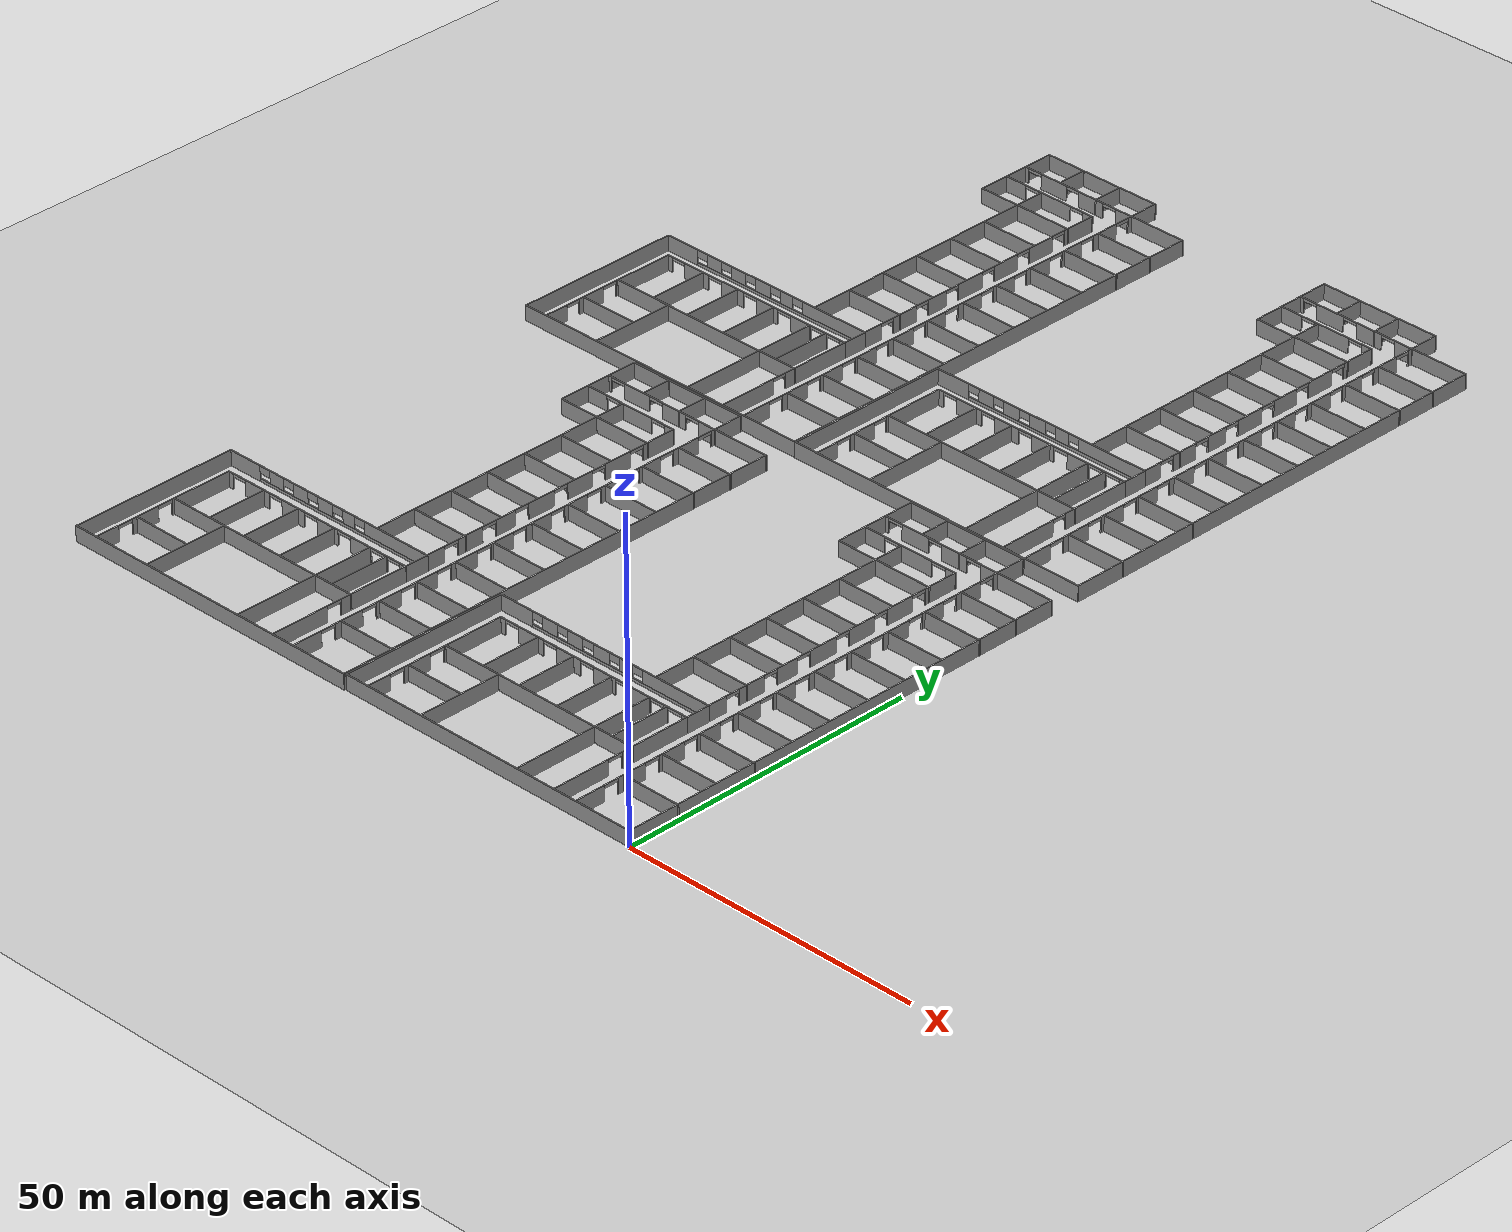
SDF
<sdf version="1.6">
 <world name="default">
  <light name="sun" type="directional">
   <pose>0 0 10 0 -0 0</pose>
   <diffuse>0.8 0.8 0.8 1</diffuse>
   <specular>0.1 0.1 0.1 1</specular>
   <attenuation>
    <range>1000</range>
    <constant>0.9</constant>
    <linear>0.01</linear>
    <quadratic>0.001</quadratic>
   </attenuation>
   <direction>-0.5 0.5 -1</direction>
  </light>
  <model name="ground_plane">
   <static>1</static>
   <link name="link">
    <collision name="collision">
     <geometry><plane><normal>0 0 1</normal><size>100 100</size></plane></geometry>
     <surface><friction><ode><mu>100</mu><mu2>50</mu2></ode></friction></surface>
    </collision>
    <visual name="visual">
     <cast_shadows>0</cast_shadows>
     <geometry><plane><normal>0 0 1</normal><size>100 100</size></plane></geometry>
     <material>
      <script><uri>file://media/materials/scripts/gazebo.material</uri><name>Gazebo/Grey</name></script>
     </material>
    </visual>
   </link>
  </model>
  <gravity>0 0 -9.8</gravity>
  <magnetic_field>6e-06 2.3e-05 -4.2e-05</magnetic_field>
  <atmosphere type="adiabatic"/>
  <physics name="default_physics" default="0" type="ode">
   <max_step_size>0.001</max_step_size>
   <real_time_factor>1</real_time_factor>
   <real_time_update_rate>1000</real_time_update_rate>
  </physics>
  <scene><ambient>0.4 0.4 0.4 1</ambient><background>0.7 0.7 0.7 1</background><shadows>1</shadows></scene>
  <spherical_coordinates>
   <surface_model>EARTH_WGS84</surface_model>
   <latitude_deg>0</latitude_deg>
   <longitude_deg>0</longitude_deg>
   <elevation>0</elevation>
   <heading_deg>0</heading_deg>
  </spherical_coordinates>
  <model name="Jacaranda_v4">
   <link name="Wall_0">
    <pose>-8.84429 26.2823 0 0 -0 0</pose>
    <visual name="Wall_0_Visual_0">
     <pose>-10.1136 0 1.25 0 -0 0</pose>
     <geometry><box><size>0.772872 0.2 2.5</size></box></geometry>
     <material>
      <script><uri>file://media/materials/scripts/gazebo.material</uri><name>Gazebo/Grey</name></script>
     </material>
    </visual>
    <collision name="Wall_0_Collision_0">
     <geometry><box><size>0.772872 0.2 2.5</size></box></geometry>
     <pose>-10.1136 0 1.25 0 -0 0</pose>
    </collision>
    <visual name="Wall_0_Visual_1">
     <pose>-4.7572 0 1.25 0 -0 0</pose>
     <geometry><box><size>4.93987 0.2 2.5</size></box></geometry>
     <material>
      <script><uri>file://media/materials/scripts/gazebo.material</uri><name>Gazebo/Grey</name></script>
     </material>
    </visual>
    <collision name="Wall_0_Collision_1">
     <geometry><box><size>4.93987 0.2 2.5</size></box></geometry>
     <pose>-4.7572 0 1.25 0 -0 0</pose>
    </collision>
    <visual name="Wall_0_Visual_2">
     <pose>2.52116 0 1.25 0 -0 0</pose>
     <geometry><box><size>4.61684 0.2 2.5</size></box></geometry>
     <material>
      <script><uri>file://media/materials/scripts/gazebo.material</uri><name>Gazebo/Grey</name></script>
     </material>
    </visual>
    <collision name="Wall_0_Collision_2">
     <geometry><box><size>4.61684 0.2 2.5</size></box></geometry>
     <pose>2.52116 0 1.25 0 -0 0</pose>
    </collision>
    <visual name="Wall_0_Visual_3">
     <pose>8.91479 0 1.25 0 -0 0</pose>
     <geometry><box><size>3.17042 0.2 2.5</size></box></geometry>
     <material>
      <script><uri>file://media/materials/scripts/gazebo.material</uri><name>Gazebo/Grey</name></script>
     </material>
    </visual>
    <collision name="Wall_0_Collision_3">
     <geometry><box><size>3.17042 0.2 2.5</size></box></geometry>
     <pose>8.91479 0 1.25 0 -0 0</pose>
    </collision>
    <visual name="Wall_0_Visual_4">
     <pose>-8.47713 0 2.25 0 -0 0</pose>
     <geometry><box><size>2.5 0.2 0.5</size></box></geometry>
     <material>
      <script><uri>file://media/materials/scripts/gazebo.material</uri><name>Gazebo/Grey</name></script>
     </material>
    </visual>
    <collision name="Wall_0_Collision_4">
     <geometry><box><size>2.5 0.2 0.5</size></box></geometry>
     <pose>-8.47713 0 2.25 0 -0 0</pose>
    </collision>
    <visual name="Wall_0_Visual_5">
     <pose>-1.03726 0 2.25 0 -0 0</pose>
     <geometry><box><size>2.5 0.2 0.5</size></box></geometry>
     <material>
      <script><uri>file://media/materials/scripts/gazebo.material</uri><name>Gazebo/Grey</name></script>
     </material>
    </visual>
    <collision name="Wall_0_Collision_5">
     <geometry><box><size>2.5 0.2 0.5</size></box></geometry>
     <pose>-1.03726 0 2.25 0 -0 0</pose>
    </collision>
    <visual name="Wall_0_Visual_6">
     <pose>6.07958 0 2.25 0 -0 0</pose>
     <geometry><box><size>2.5 0.2 0.5</size></box></geometry>
     <material>
      <script><uri>file://media/materials/scripts/gazebo.material</uri><name>Gazebo/Grey</name></script>
     </material>
    </visual>
    <collision name="Wall_0_Collision_6">
     <geometry><box><size>2.5 0.2 0.5</size></box></geometry>
     <pose>6.07958 0 2.25 0 -0 0</pose>
    </collision>
   </link>
   <link name="Wall_100">
    <collision name="Wall_100_Collision">
     <geometry><box><size>10 0.2 2.5</size></box></geometry>
     <pose>0 0 1.25 0 -0 0</pose>
    </collision>
    <visual name="Wall_100_Visual">
     <pose>0 0 1.25 0 -0 0</pose>
     <geometry><box><size>10 0.2 2.5</size></box></geometry>
     <material>
      <script><uri>file://media/materials/scripts/gazebo.material</uri><name>Gazebo/Grey</name></script>
     </material>
    </visual>
    <velocity_decay><linear>0</linear><angular>0</angular></velocity_decay>
    <pose>-6.16092 -32.9106 0 0 0 -1.5708</pose>
   </link>
   <link name="Wall_102">
    <collision name="Wall_102_Collision">
     <geometry><box><size>10 0.2 2.5</size></box></geometry>
     <pose>0 0 1.25 0 -0 0</pose>
    </collision>
    <visual name="Wall_102_Visual">
     <pose>0 0 1.25 0 -0 0</pose>
     <geometry><box><size>10 0.2 2.5</size></box></geometry>
     <material>
      <script><uri>file://media/materials/scripts/gazebo.material</uri><name>Gazebo/Grey</name></script>
     </material>
    </visual>
    <velocity_decay><linear>0</linear><angular>0</angular></velocity_decay>
    <pose>-16.4411 -32.898 0 0 0 -1.5708</pose>
   </link>
   <link name="Wall_104">
    <collision name="Wall_104_Collision">
     <geometry><box><size>10 0.2 2.5</size></box></geometry>
     <pose>0 0 1.25 0 -0 0</pose>
    </collision>
    <visual name="Wall_104_Visual">
     <pose>0 0 1.25 0 -0 0</pose>
     <geometry><box><size>10 0.2 2.5</size></box></geometry>
     <material>
      <script><uri>file://media/materials/scripts/gazebo.material</uri><name>Gazebo/Grey</name></script>
     </material>
    </visual>
    <velocity_decay><linear>0</linear><angular>0</angular></velocity_decay>
    <pose>-23.6073 -32.9162 0 0 0 -1.5708</pose>
   </link>
   <link name="Wall_106">
    <collision name="Wall_106_Collision">
     <geometry><box><size>10 0.2 2.5</size></box></geometry>
     <pose>0 0 1.25 0 -0 0</pose>
    </collision>
    <visual name="Wall_106_Visual">
     <pose>0 0 1.25 0 -0 0</pose>
     <geometry><box><size>10 0.2 2.5</size></box></geometry>
     <material>
      <script><uri>file://media/materials/scripts/gazebo.material</uri><name>Gazebo/Grey</name></script>
     </material>
    </visual>
    <velocity_decay><linear>0</linear><angular>0</angular></velocity_decay>
    <pose>-30.3649 -32.9482 0 0 0 -1.5708</pose>
   </link>
   <link name="Wall_108">
    <pose>-37.4695 -39.9617 0 0 0 -1.5708</pose>
    <visual name="Wall_108_Visual_0">
     <pose>-6.76156 0 1.25 0 -0 0</pose>
     <geometry><box><size>10.4769 0.2 2.5</size></box></geometry>
     <material>
      <script><uri>file://media/materials/scripts/gazebo.material</uri><name>Gazebo/Grey</name></script>
     </material>
    </visual>
    <collision name="Wall_108_Collision_0">
     <geometry><box><size>10.4769 0.2 2.5</size></box></geometry>
     <pose>-6.76156 0 1.25 0 -0 0</pose>
    </collision>
    <visual name="Wall_108_Visual_1">
     <pose>3.29825 0 1.25 0 -0 0</pose>
     <geometry><box><size>4.64276 0.2 2.5</size></box></geometry>
     <material>
      <script><uri>file://media/materials/scripts/gazebo.material</uri><name>Gazebo/Grey</name></script>
     </material>
    </visual>
    <collision name="Wall_108_Collision_1">
     <geometry><box><size>4.64276 0.2 2.5</size></box></geometry>
     <pose>3.29825 0 1.25 0 -0 0</pose>
    </collision>
    <visual name="Wall_108_Visual_2">
     <pose>10.0598 0 1.25 0 -0 0</pose>
     <geometry><box><size>3.88036 0.2 2.5</size></box></geometry>
     <material>
      <script><uri>file://media/materials/scripts/gazebo.material</uri><name>Gazebo/Grey</name></script>
     </material>
    </visual>
    <collision name="Wall_108_Collision_2">
     <geometry><box><size>3.88036 0.2 2.5</size></box></geometry>
     <pose>10.0598 0 1.25 0 -0 0</pose>
    </collision>
    <visual name="Wall_108_Visual_3">
     <pose>-0.273129 0 2.25 0 -0 0</pose>
     <geometry><box><size>2.5 0.2 0.5</size></box></geometry>
     <material>
      <script><uri>file://media/materials/scripts/gazebo.material</uri><name>Gazebo/Grey</name></script>
     </material>
    </visual>
    <collision name="Wall_108_Collision_3">
     <geometry><box><size>2.5 0.2 0.5</size></box></geometry>
     <pose>-0.273129 0 2.25 0 -0 0</pose>
    </collision>
    <visual name="Wall_108_Visual_4">
     <pose>6.86964 0 2.25 0 -0 0</pose>
     <geometry><box><size>2.5 0.2 0.5</size></box></geometry>
     <material>
      <script><uri>file://media/materials/scripts/gazebo.material</uri><name>Gazebo/Grey</name></script>
     </material>
    </visual>
    <collision name="Wall_108_Collision_4">
     <geometry><box><size>2.5 0.2 0.5</size></box></geometry>
     <pose>6.86964 0 2.25 0 -0 0</pose>
    </collision>
   </link>
   <link name="Wall_110">
    <collision name="Wall_110_Collision">
     <geometry><box><size>53 0.2 2.5</size></box></geometry>
     <pose>0 0 1.25 0 -0 0</pose>
    </collision>
    <visual name="Wall_110_Visual">
     <pose>0 0 1.25 0 -0 0</pose>
     <geometry><box><size>53 0.2 2.5</size></box></geometry>
     <material>
      <script><uri>file://media/materials/scripts/gazebo.material</uri><name>Gazebo/Grey</name></script>
     </material>
    </visual>
    <velocity_decay><linear>0</linear><angular>0</angular></velocity_decay>
    <pose>-15.0842 -52.0158 0 0 -0 0</pose>
   </link>
   <link name="Wall_112">
    <collision name="Wall_112_Collision">
     <geometry><box><size>14 0.2 2.5</size></box></geometry>
     <pose>0 0 1.25 0 -0 0</pose>
    </collision>
    <visual name="Wall_112_Visual">
     <pose>0 0 1.25 0 -0 0</pose>
     <geometry><box><size>14 0.2 2.5</size></box></geometry>
     <material>
      <script><uri>file://media/materials/scripts/gazebo.material</uri><name>Gazebo/Grey</name></script>
     </material>
    </visual>
    <velocity_decay><linear>0</linear><angular>0</angular></velocity_decay>
    <pose>-27.4151 -45.0631 0 0 0 -1.5708</pose>
   </link>
   <link name="Wall_114">
    <collision name="Wall_114_Collision">
     <geometry><box><size>28 0.2 2.5</size></box></geometry>
     <pose>0 0 1.25 0 -0 0</pose>
    </collision>
    <visual name="Wall_114_Visual">
     <pose>0 0 1.25 0 -0 0</pose>
     <geometry><box><size>28 0.2 2.5</size></box></geometry>
     <material>
      <script><uri>file://media/materials/scripts/gazebo.material</uri><name>Gazebo/Grey</name></script>
     </material>
    </visual>
    <velocity_decay><linear>0</linear><angular>0</angular></velocity_decay>
    <pose>-41.4842 -37.994 0 0 0 -1.5708</pose>
   </link>
   <link name="Wall_116">
    <collision name="Wall_116_Collision">
     <geometry><box><size>10 0.2 2.5</size></box></geometry>
     <pose>0 0 1.25 0 -0 0</pose>
    </collision>
    <visual name="Wall_116_Visual">
     <pose>0 0 1.25 0 -0 0</pose>
     <geometry><box><size>10 0.2 2.5</size></box></geometry>
     <material>
      <script><uri>file://media/materials/scripts/gazebo.material</uri><name>Gazebo/Grey</name></script>
     </material>
    </visual>
    <velocity_decay><linear>0</linear><angular>0</angular></velocity_decay>
    <pose>6.51408 -43.3984 0 0 -0 0</pose>
   </link>
   <link name="Wall_2">
    <collision name="Wall_2_Collision">
     <geometry><box><size>10 0.2 2.5</size></box></geometry>
     <pose>0 0 1.25 0 -0 0</pose>
    </collision>
    <visual name="Wall_2_Visual">
     <pose>0 0 1.25 0 -0 0</pose>
     <geometry><box><size>10 0.2 2.5</size></box></geometry>
     <material>
      <script><uri>file://media/materials/scripts/gazebo.material</uri><name>Gazebo/Grey</name></script>
     </material>
    </visual>
    <velocity_decay><linear>0</linear><angular>0</angular></velocity_decay>
    <pose>-7.44654 3.56016 0 0 -0 0</pose>
   </link>
   <link name="Wall_22">
    <collision name="Wall_22_Collision">
     <geometry><box><size>5 0.2 2.5</size></box></geometry>
     <pose>0 0 1.25 0 -0 0</pose>
    </collision>
    <visual name="Wall_22_Visual">
     <pose>0 0 1.25 0 -0 0</pose>
     <geometry><box><size>5 0.2 2.5</size></box></geometry>
     <material>
      <script><uri>file://media/materials/scripts/gazebo.material</uri><name>Gazebo/Grey</name></script>
     </material>
    </visual>
    <velocity_decay><linear>0</linear><angular>0</angular></velocity_decay>
    <pose>-19.2226 28.7685 0 0 -0 1.5708</pose>
   </link>
   <link name="Wall_24">
    <collision name="Wall_24_Collision">
     <geometry><box><size>7 0.2 2.5</size></box></geometry>
     <pose>0 0 1.25 0 -0 0</pose>
    </collision>
    <visual name="Wall_24_Visual">
     <pose>0 0 1.25 0 -0 0</pose>
     <geometry><box><size>7 0.2 2.5</size></box></geometry>
     <material>
      <script><uri>file://media/materials/scripts/gazebo.material</uri><name>Gazebo/Grey</name></script>
     </material>
    </visual>
    <velocity_decay><linear>0</linear><angular>0</angular></velocity_decay>
    <pose>-15.7827 31.2426 0 0 -0 0</pose>
   </link>
   <link name="Wall_26">
    <collision name="Wall_26_Collision">
     <geometry><box><size>5 0.2 2.5</size></box></geometry>
     <pose>0 0 1.25 0 -0 0</pose>
    </collision>
    <visual name="Wall_26_Visual">
     <pose>0 0 1.25 0 -0 0</pose>
     <geometry><box><size>5 0.2 2.5</size></box></geometry>
     <material>
      <script><uri>file://media/materials/scripts/gazebo.material</uri><name>Gazebo/Grey</name></script>
     </material>
    </visual>
    <velocity_decay><linear>0</linear><angular>0</angular></velocity_decay>
    <pose>-12.42 28.8426 0 0 0 -1.5708</pose>
   </link>
   <link name="Wall_29">
    <collision name="Wall_29_Collision">
     <geometry><box><size>7 0.2 2.5</size></box></geometry>
     <pose>0 0 1.25 0 -0 0</pose>
    </collision>
    <visual name="Wall_29_Visual">
     <pose>0 0 1.25 0 -0 0</pose>
     <geometry><box><size>7 0.2 2.5</size></box></geometry>
     <material>
      <script><uri>file://media/materials/scripts/gazebo.material</uri><name>Gazebo/Grey</name></script>
     </material>
    </visual>
    <velocity_decay><linear>0</linear><angular>0</angular></velocity_decay>
    <pose>-8.85634 31.2426 0 0 -0 0</pose>
   </link>
   <link name="Wall_31">
    <collision name="Wall_31_Collision">
     <geometry><box><size>5 0.2 2.5</size></box></geometry>
     <pose>0 0 1.25 0 -0 0</pose>
    </collision>
    <visual name="Wall_31_Visual">
     <pose>0 0 1.25 0 -0 0</pose>
     <geometry><box><size>5 0.2 2.5</size></box></geometry>
     <material>
      <script><uri>file://media/materials/scripts/gazebo.material</uri><name>Gazebo/Grey</name></script>
     </material>
    </visual>
    <velocity_decay><linear>0</linear><angular>0</angular></velocity_decay>
    <pose>-5.3828 28.6789 0 0 0 -1.5708</pose>
   </link>
   <link name="Wall_33">
    <collision name="Wall_33_Collision">
     <geometry><box><size>7 0.2 2.5</size></box></geometry>
     <pose>0 0 1.25 0 -0 0</pose>
    </collision>
    <visual name="Wall_33_Visual">
     <pose>0 0 1.25 0 -0 0</pose>
     <geometry><box><size>7 0.2 2.5</size></box></geometry>
     <material>
      <script><uri>file://media/materials/scripts/gazebo.material</uri><name>Gazebo/Grey</name></script>
     </material>
    </visual>
    <velocity_decay><linear>0</linear><angular>0</angular></velocity_decay>
    <pose>-1.87207 31.2789 0 0 -0 0</pose>
   </link>
   <link name="Wall_35">
    <pose>1.50679 -10.3195 0 0 0 -1.5708</pose>
    <visual name="Wall_35_Visual_0">
     <pose>-38.7718 0 1.25 0 -0 0</pose>
     <geometry><box><size>5.89333 0.2 2.5</size></box></geometry>
     <material>
      <script><uri>file://media/materials/scripts/gazebo.material</uri><name>Gazebo/Grey</name></script>
     </material>
    </visual>
    <collision name="Wall_35_Collision_0">
     <geometry><box><size>5.89333 0.2 2.5</size></box></geometry>
     <pose>-38.7718 0 1.25 0 -0 0</pose>
    </collision>
    <visual name="Wall_35_Visual_1">
     <pose>-30.9611 0 1.25 0 -0 0</pose>
     <geometry><box><size>4.72808 0.2 2.5</size></box></geometry>
     <material>
      <script><uri>file://media/materials/scripts/gazebo.material</uri><name>Gazebo/Grey</name></script>
     </material>
    </visual>
    <collision name="Wall_35_Collision_1">
     <geometry><box><size>4.72808 0.2 2.5</size></box></geometry>
     <pose>-30.9611 0 1.25 0 -0 0</pose>
    </collision>
    <visual name="Wall_35_Visual_2">
     <pose>-24.0927 0 1.25 0 -0 0</pose>
     <geometry><box><size>4.00867 0.2 2.5</size></box></geometry>
     <material>
      <script><uri>file://media/materials/scripts/gazebo.material</uri><name>Gazebo/Grey</name></script>
     </material>
    </visual>
    <collision name="Wall_35_Collision_2">
     <geometry><box><size>4.00867 0.2 2.5</size></box></geometry>
     <pose>-24.0927 0 1.25 0 -0 0</pose>
    </collision>
    <visual name="Wall_35_Visual_3">
     <pose>-17.1876 0 1.25 0 -0 0</pose>
     <geometry><box><size>4.80162 0.2 2.5</size></box></geometry>
     <material>
      <script><uri>file://media/materials/scripts/gazebo.material</uri><name>Gazebo/Grey</name></script>
     </material>
    </visual>
    <collision name="Wall_35_Collision_3">
     <geometry><box><size>4.80162 0.2 2.5</size></box></geometry>
     <pose>-17.1876 0 1.25 0 -0 0</pose>
    </collision>
    <visual name="Wall_35_Visual_4">
     <pose>-10.1336 0 1.25 0 -0 0</pose>
     <geometry><box><size>4.3064 0.2 2.5</size></box></geometry>
     <material>
      <script><uri>file://media/materials/scripts/gazebo.material</uri><name>Gazebo/Grey</name></script>
     </material>
    </visual>
    <collision name="Wall_35_Collision_4">
     <geometry><box><size>4.3064 0.2 2.5</size></box></geometry>
     <pose>-10.1336 0 1.25 0 -0 0</pose>
    </collision>
    <visual name="Wall_35_Visual_5">
     <pose>-3.14147 0 1.25 0 -0 0</pose>
     <geometry><box><size>4.67776 0.2 2.5</size></box></geometry>
     <material>
      <script><uri>file://media/materials/scripts/gazebo.material</uri><name>Gazebo/Grey</name></script>
     </material>
    </visual>
    <collision name="Wall_35_Collision_5">
     <geometry><box><size>4.67776 0.2 2.5</size></box></geometry>
     <pose>-3.14147 0 1.25 0 -0 0</pose>
    </collision>
    <visual name="Wall_35_Visual_6">
     <pose>3.7295 0 1.25 0 -0 0</pose>
     <geometry><box><size>4.06418 0.2 2.5</size></box></geometry>
     <material>
      <script><uri>file://media/materials/scripts/gazebo.material</uri><name>Gazebo/Grey</name></script>
     </material>
    </visual>
    <collision name="Wall_35_Collision_6">
     <geometry><box><size>4.06418 0.2 2.5</size></box></geometry>
     <pose>3.7295 0 1.25 0 -0 0</pose>
    </collision>
    <visual name="Wall_35_Visual_7">
     <pose>10.6976 0 1.25 0 -0 0</pose>
     <geometry><box><size>4.872 0.2 2.5</size></box></geometry>
     <material>
      <script><uri>file://media/materials/scripts/gazebo.material</uri><name>Gazebo/Grey</name></script>
     </material>
    </visual>
    <collision name="Wall_35_Collision_7">
     <geometry><box><size>4.872 0.2 2.5</size></box></geometry>
     <pose>10.6976 0 1.25 0 -0 0</pose>
    </collision>
    <visual name="Wall_35_Visual_8">
     <pose>17.7003 0 1.25 0 -0 0</pose>
     <geometry><box><size>4.13333 0.2 2.5</size></box></geometry>
     <material>
      <script><uri>file://media/materials/scripts/gazebo.material</uri><name>Gazebo/Grey</name></script>
     </material>
    </visual>
    <collision name="Wall_35_Collision_8">
     <geometry><box><size>4.13333 0.2 2.5</size></box></geometry>
     <pose>17.7003 0 1.25 0 -0 0</pose>
    </collision>
    <visual name="Wall_35_Visual_9">
     <pose>24.507 0 1.25 0 -0 0</pose>
     <geometry><box><size>4.48015 0.2 2.5</size></box></geometry>
     <material>
      <script><uri>file://media/materials/scripts/gazebo.material</uri><name>Gazebo/Grey</name></script>
     </material>
    </visual>
    <collision name="Wall_35_Collision_9">
     <geometry><box><size>4.48015 0.2 2.5</size></box></geometry>
     <pose>24.507 0 1.25 0 -0 0</pose>
    </collision>
    <visual name="Wall_35_Visual_10">
     <pose>31.7056 0 1.25 0 -0 0</pose>
     <geometry><box><size>4.91715 0.2 2.5</size></box></geometry>
     <material>
      <script><uri>file://media/materials/scripts/gazebo.material</uri><name>Gazebo/Grey</name></script>
     </material>
    </visual>
    <collision name="Wall_35_Collision_10">
     <geometry><box><size>4.91715 0.2 2.5</size></box></geometry>
     <pose>31.7056 0 1.25 0 -0 0</pose>
    </collision>
    <visual name="Wall_35_Visual_11">
     <pose>39.1913 0 1.25 0 -0 0</pose>
     <geometry><box><size>5.05424 0.2 2.5</size></box></geometry>
     <material>
      <script><uri>file://media/materials/scripts/gazebo.material</uri><name>Gazebo/Grey</name></script>
     </material>
    </visual>
    <collision name="Wall_35_Collision_11">
     <geometry><box><size>5.05424 0.2 2.5</size></box></geometry>
     <pose>39.1913 0 1.25 0 -0 0</pose>
    </collision>
    <visual name="Wall_35_Visual_12">
     <pose>-34.5751 0 2.25 0 -0 0</pose>
     <geometry><box><size>2.5 0.2 0.5</size></box></geometry>
     <material>
      <script><uri>file://media/materials/scripts/gazebo.material</uri><name>Gazebo/Grey</name></script>
     </material>
    </visual>
    <collision name="Wall_35_Collision_12">
     <geometry><box><size>2.5 0.2 0.5</size></box></geometry>
     <pose>-34.5751 0 2.25 0 -0 0</pose>
    </collision>
    <visual name="Wall_35_Visual_13">
     <pose>-27.347 0 2.25 0 -0 0</pose>
     <geometry><box><size>2.5 0.2 0.5</size></box></geometry>
     <material>
      <script><uri>file://media/materials/scripts/gazebo.material</uri><name>Gazebo/Grey</name></script>
     </material>
    </visual>
    <collision name="Wall_35_Collision_13">
     <geometry><box><size>2.5 0.2 0.5</size></box></geometry>
     <pose>-27.347 0 2.25 0 -0 0</pose>
    </collision>
    <visual name="Wall_35_Visual_14">
     <pose>-20.8384 0 2.25 0 -0 0</pose>
     <geometry><box><size>2.5 0.2 0.5</size></box></geometry>
     <material>
      <script><uri>file://media/materials/scripts/gazebo.material</uri><name>Gazebo/Grey</name></script>
     </material>
    </visual>
    <collision name="Wall_35_Collision_14">
     <geometry><box><size>2.5 0.2 0.5</size></box></geometry>
     <pose>-20.8384 0 2.25 0 -0 0</pose>
    </collision>
    <visual name="Wall_35_Visual_15">
     <pose>-13.5368 0 2.25 0 -0 0</pose>
     <geometry><box><size>2.5 0.2 0.5</size></box></geometry>
     <material>
      <script><uri>file://media/materials/scripts/gazebo.material</uri><name>Gazebo/Grey</name></script>
     </material>
    </visual>
    <collision name="Wall_35_Collision_15">
     <geometry><box><size>2.5 0.2 0.5</size></box></geometry>
     <pose>-13.5368 0 2.25 0 -0 0</pose>
    </collision>
    <visual name="Wall_35_Visual_16">
     <pose>-6.73035 0 2.25 0 -0 0</pose>
     <geometry><box><size>2.5 0.2 0.5</size></box></geometry>
     <material>
      <script><uri>file://media/materials/scripts/gazebo.material</uri><name>Gazebo/Grey</name></script>
     </material>
    </visual>
    <collision name="Wall_35_Collision_16">
     <geometry><box><size>2.5 0.2 0.5</size></box></geometry>
     <pose>-6.73035 0 2.25 0 -0 0</pose>
    </collision>
    <visual name="Wall_35_Visual_17">
     <pose>0.447409 0 2.25 0 -0 0</pose>
     <geometry><box><size>2.5 0.2 0.5</size></box></geometry>
     <material>
      <script><uri>file://media/materials/scripts/gazebo.material</uri><name>Gazebo/Grey</name></script>
     </material>
    </visual>
    <collision name="Wall_35_Collision_17">
     <geometry><box><size>2.5 0.2 0.5</size></box></geometry>
     <pose>0.447409 0 2.25 0 -0 0</pose>
    </collision>
    <visual name="Wall_35_Visual_18">
     <pose>7.01159 0 2.25 0 -0 0</pose>
     <geometry><box><size>2.5 0.2 0.5</size></box></geometry>
     <material>
      <script><uri>file://media/materials/scripts/gazebo.material</uri><name>Gazebo/Grey</name></script>
     </material>
    </visual>
    <collision name="Wall_35_Collision_18">
     <geometry><box><size>2.5 0.2 0.5</size></box></geometry>
     <pose>7.01159 0 2.25 0 -0 0</pose>
    </collision>
    <visual name="Wall_35_Visual_19">
     <pose>14.3836 0 2.25 0 -0 0</pose>
     <geometry><box><size>2.5 0.2 0.5</size></box></geometry>
     <material>
      <script><uri>file://media/materials/scripts/gazebo.material</uri><name>Gazebo/Grey</name></script>
     </material>
    </visual>
    <collision name="Wall_35_Collision_19">
     <geometry><box><size>2.5 0.2 0.5</size></box></geometry>
     <pose>14.3836 0 2.25 0 -0 0</pose>
    </collision>
    <visual name="Wall_35_Visual_20">
     <pose>21.0169 0 2.25 0 -0 0</pose>
     <geometry><box><size>2.5 0.2 0.5</size></box></geometry>
     <material>
      <script><uri>file://media/materials/scripts/gazebo.material</uri><name>Gazebo/Grey</name></script>
     </material>
    </visual>
    <collision name="Wall_35_Collision_20">
     <geometry><box><size>2.5 0.2 0.5</size></box></geometry>
     <pose>21.0169 0 2.25 0 -0 0</pose>
    </collision>
    <visual name="Wall_35_Visual_21">
     <pose>27.9971 0 2.25 0 -0 0</pose>
     <geometry><box><size>2.5 0.2 0.5</size></box></geometry>
     <material>
      <script><uri>file://media/materials/scripts/gazebo.material</uri><name>Gazebo/Grey</name></script>
     </material>
    </visual>
    <collision name="Wall_35_Collision_21">
     <geometry><box><size>2.5 0.2 0.5</size></box></geometry>
     <pose>27.9971 0 2.25 0 -0 0</pose>
    </collision>
    <visual name="Wall_35_Visual_22">
     <pose>35.4142 0 2.25 0 -0 0</pose>
     <geometry><box><size>2.5 0.2 0.5</size></box></geometry>
     <material>
      <script><uri>file://media/materials/scripts/gazebo.material</uri><name>Gazebo/Grey</name></script>
     </material>
    </visual>
    <collision name="Wall_35_Collision_22">
     <geometry><box><size>2.5 0.2 0.5</size></box></geometry>
     <pose>35.4142 0 2.25 0 -0 0</pose>
    </collision>
   </link>
   <link name="Wall_37">
    <pose>-2.48729 -39.9261 0 0 0 -1.5708</pose>
    <visual name="Wall_37_Visual_0">
     <pose>-6.07032 0 1.25 0 -0 0</pose>
     <geometry><box><size>11.8594 0.2 2.5</size></box></geometry>
     <material>
      <script><uri>file://media/materials/scripts/gazebo.material</uri><name>Gazebo/Grey</name></script>
     </material>
    </visual>
    <collision name="Wall_37_Collision_0">
     <geometry><box><size>11.8594 0.2 2.5</size></box></geometry>
     <pose>-6.07032 0 1.25 0 -0 0</pose>
    </collision>
    <visual name="Wall_37_Visual_1">
     <pose>7.17968 0 1.25 0 -0 0</pose>
     <geometry><box><size>9.64064 0.2 2.5</size></box></geometry>
     <material>
      <script><uri>file://media/materials/scripts/gazebo.material</uri><name>Gazebo/Grey</name></script>
     </material>
    </visual>
    <collision name="Wall_37_Collision_1">
     <geometry><box><size>9.64064 0.2 2.5</size></box></geometry>
     <pose>7.17968 0 1.25 0 -0 0</pose>
    </collision>
    <visual name="Wall_37_Visual_2">
     <pose>1.10936 0 2.25 0 -0 0</pose>
     <geometry><box><size>2.5 0.2 0.5</size></box></geometry>
     <material>
      <script><uri>file://media/materials/scripts/gazebo.material</uri><name>Gazebo/Grey</name></script>
     </material>
    </visual>
    <collision name="Wall_37_Collision_2">
     <geometry><box><size>2.5 0.2 0.5</size></box></geometry>
     <pose>1.10936 0 2.25 0 -0 0</pose>
    </collision>
   </link>
   <link name="Wall_39">
    <collision name="Wall_39_Collision">
     <geometry><box><size>4 0.2 2.5</size></box></geometry>
     <pose>0 0 1.25 0 -0 0</pose>
    </collision>
    <visual name="Wall_39_Visual">
     <pose>0 0 1.25 0 -0 0</pose>
     <geometry><box><size>4 0.2 2.5</size></box></geometry>
     <material>
      <script><uri>file://media/materials/scripts/gazebo.material</uri><name>Gazebo/Grey</name></script>
     </material>
    </visual>
    <velocity_decay><linear>0</linear><angular>0</angular></velocity_decay>
    <pose>-19.206 24.2121 0 0 0 -1.5708</pose>
   </link>
   <link name="Wall_41">
    <pose>-10.8339 22.3118 0 0 -0 0</pose>
    <visual name="Wall_41_Visual_0">
     <pose>-6.54675 0 1.25 0 -0 0</pose>
     <geometry><box><size>3.9065 0.2 2.5</size></box></geometry>
     <material>
      <script><uri>file://media/materials/scripts/gazebo.material</uri><name>Gazebo/Grey</name></script>
     </material>
    </visual>
    <collision name="Wall_41_Collision_0">
     <geometry><box><size>3.9065 0.2 2.5</size></box></geometry>
     <pose>-6.54675 0 1.25 0 -0 0</pose>
    </collision>
    <visual name="Wall_41_Visual_1">
     <pose>1.04072 0 1.25 0 -0 0</pose>
     <geometry><box><size>6.26843 0.2 2.5</size></box></geometry>
     <material>
      <script><uri>file://media/materials/scripts/gazebo.material</uri><name>Gazebo/Grey</name></script>
     </material>
    </visual>
    <collision name="Wall_41_Collision_1">
     <geometry><box><size>6.26843 0.2 2.5</size></box></geometry>
     <pose>1.04072 0 1.25 0 -0 0</pose>
    </collision>
    <visual name="Wall_41_Visual_2">
     <pose>7.58747 0 1.25 0 -0 0</pose>
     <geometry><box><size>1.82507 0.2 2.5</size></box></geometry>
     <material>
      <script><uri>file://media/materials/scripts/gazebo.material</uri><name>Gazebo/Grey</name></script>
     </material>
    </visual>
    <collision name="Wall_41_Collision_2">
     <geometry><box><size>1.82507 0.2 2.5</size></box></geometry>
     <pose>7.58747 0 1.25 0 -0 0</pose>
    </collision>
    <visual name="Wall_41_Visual_3">
     <pose>-3.3435 0 2.25 0 -0 0</pose>
     <geometry><box><size>2.5 0.2 0.5</size></box></geometry>
     <material>
      <script><uri>file://media/materials/scripts/gazebo.material</uri><name>Gazebo/Grey</name></script>
     </material>
    </visual>
    <collision name="Wall_41_Collision_3">
     <geometry><box><size>2.5 0.2 0.5</size></box></geometry>
     <pose>-3.3435 0 2.25 0 -0 0</pose>
    </collision>
    <visual name="Wall_41_Visual_4">
     <pose>5.42493 0 2.25 0 -0 0</pose>
     <geometry><box><size>2.5 0.2 0.5</size></box></geometry>
     <material>
      <script><uri>file://media/materials/scripts/gazebo.material</uri><name>Gazebo/Grey</name></script>
     </material>
    </visual>
    <collision name="Wall_41_Collision_4">
     <geometry><box><size>2.5 0.2 0.5</size></box></geometry>
     <pose>5.42493 0 2.25 0 -0 0</pose>
    </collision>
   </link>
   <link name="Wall_43">
    <pose>-2.46558 -0.8445 0 0 0 -1.5708</pose>
    <visual name="Wall_43_Visual_0">
     <pose>-20.2936 0 1.25 0 -0 0</pose>
     <geometry><box><size>5.88874 0.2 2.5</size></box></geometry>
     <material>
      <script><uri>file://media/materials/scripts/gazebo.material</uri><name>Gazebo/Grey</name></script>
     </material>
    </visual>
    <collision name="Wall_43_Collision_0">
     <geometry><box><size>5.88874 0.2 2.5</size></box></geometry>
     <pose>-20.2936 0 1.25 0 -0 0</pose>
    </collision>
    <visual name="Wall_43_Visual_1">
     <pose>-12.4598 0 1.25 0 -0 0</pose>
     <geometry><box><size>4.77894 0.2 2.5</size></box></geometry>
     <material>
      <script><uri>file://media/materials/scripts/gazebo.material</uri><name>Gazebo/Grey</name></script>
     </material>
    </visual>
    <collision name="Wall_43_Collision_1">
     <geometry><box><size>4.77894 0.2 2.5</size></box></geometry>
     <pose>-12.4598 0 1.25 0 -0 0</pose>
    </collision>
    <visual name="Wall_43_Visual_2">
     <pose>-5.24423 0 1.25 0 -0 0</pose>
     <geometry><box><size>4.65218 0.2 2.5</size></box></geometry>
     <material>
      <script><uri>file://media/materials/scripts/gazebo.material</uri><name>Gazebo/Grey</name></script>
     </material>
    </visual>
    <collision name="Wall_43_Collision_2">
     <geometry><box><size>4.65218 0.2 2.5</size></box></geometry>
     <pose>-5.24423 0 1.25 0 -0 0</pose>
    </collision>
    <visual name="Wall_43_Visual_3">
     <pose>2.00205 0 1.25 0 -0 0</pose>
     <geometry><box><size>4.84039 0.2 2.5</size></box></geometry>
     <material>
      <script><uri>file://media/materials/scripts/gazebo.material</uri><name>Gazebo/Grey</name></script>
     </material>
    </visual>
    <collision name="Wall_43_Collision_3">
     <geometry><box><size>4.84039 0.2 2.5</size></box></geometry>
     <pose>2.00205 0 1.25 0 -0 0</pose>
    </collision>
    <visual name="Wall_43_Visual_4">
     <pose>8.7199 0 1.25 0 -0 0</pose>
     <geometry><box><size>3.5953 0.2 2.5</size></box></geometry>
     <material>
      <script><uri>file://media/materials/scripts/gazebo.material</uri><name>Gazebo/Grey</name></script>
     </material>
    </visual>
    <collision name="Wall_43_Collision_4">
     <geometry><box><size>3.5953 0.2 2.5</size></box></geometry>
     <pose>8.7199 0 1.25 0 -0 0</pose>
    </collision>
    <visual name="Wall_43_Visual_5">
     <pose>15.2946 0 1.25 0 -0 0</pose>
     <geometry><box><size>4.55401 0.2 2.5</size></box></geometry>
     <material>
      <script><uri>file://media/materials/scripts/gazebo.material</uri><name>Gazebo/Grey</name></script>
     </material>
    </visual>
    <collision name="Wall_43_Collision_5">
     <geometry><box><size>4.55401 0.2 2.5</size></box></geometry>
     <pose>15.2946 0 1.25 0 -0 0</pose>
    </collision>
    <visual name="Wall_43_Visual_6">
     <pose>21.6548 0 1.25 0 -0 0</pose>
     <geometry><box><size>3.16644 0.2 2.5</size></box></geometry>
     <material>
      <script><uri>file://media/materials/scripts/gazebo.material</uri><name>Gazebo/Grey</name></script>
     </material>
    </visual>
    <collision name="Wall_43_Collision_6">
     <geometry><box><size>3.16644 0.2 2.5</size></box></geometry>
     <pose>21.6548 0 1.25 0 -0 0</pose>
    </collision>
    <visual name="Wall_43_Visual_7">
     <pose>-16.0993 0 2.25 0 -0 0</pose>
     <geometry><box><size>2.5 0.2 0.5</size></box></geometry>
     <material>
      <script><uri>file://media/materials/scripts/gazebo.material</uri><name>Gazebo/Grey</name></script>
     </material>
    </visual>
    <collision name="Wall_43_Collision_7">
     <geometry><box><size>2.5 0.2 0.5</size></box></geometry>
     <pose>-16.0993 0 2.25 0 -0 0</pose>
    </collision>
    <visual name="Wall_43_Visual_8">
     <pose>-8.82032 0 2.25 0 -0 0</pose>
     <geometry><box><size>2.5 0.2 0.5</size></box></geometry>
     <material>
      <script><uri>file://media/materials/scripts/gazebo.material</uri><name>Gazebo/Grey</name></script>
     </material>
    </visual>
    <collision name="Wall_43_Collision_8">
     <geometry><box><size>2.5 0.2 0.5</size></box></geometry>
     <pose>-8.82032 0 2.25 0 -0 0</pose>
    </collision>
    <visual name="Wall_43_Visual_9">
     <pose>-1.66814 0 2.25 0 -0 0</pose>
     <geometry><box><size>2.5 0.2 0.5</size></box></geometry>
     <material>
      <script><uri>file://media/materials/scripts/gazebo.material</uri><name>Gazebo/Grey</name></script>
     </material>
    </visual>
    <collision name="Wall_43_Collision_9">
     <geometry><box><size>2.5 0.2 0.5</size></box></geometry>
     <pose>-1.66814 0 2.25 0 -0 0</pose>
    </collision>
    <visual name="Wall_43_Visual_10">
     <pose>5.67225 0 2.25 0 -0 0</pose>
     <geometry><box><size>2.5 0.2 0.5</size></box></geometry>
     <material>
      <script><uri>file://media/materials/scripts/gazebo.material</uri><name>Gazebo/Grey</name></script>
     </material>
    </visual>
    <collision name="Wall_43_Collision_10">
     <geometry><box><size>2.5 0.2 0.5</size></box></geometry>
     <pose>5.67225 0 2.25 0 -0 0</pose>
    </collision>
    <visual name="Wall_43_Visual_11">
     <pose>11.7676 0 2.25 0 -0 0</pose>
     <geometry><box><size>2.5 0.2 0.5</size></box></geometry>
     <material>
      <script><uri>file://media/materials/scripts/gazebo.material</uri><name>Gazebo/Grey</name></script>
     </material>
    </visual>
    <collision name="Wall_43_Collision_11">
     <geometry><box><size>2.5 0.2 0.5</size></box></geometry>
     <pose>11.7676 0 2.25 0 -0 0</pose>
    </collision>
    <visual name="Wall_43_Visual_12">
     <pose>18.8216 0 2.25 0 -0 0</pose>
     <geometry><box><size>2.5 0.2 0.5</size></box></geometry>
     <material>
      <script><uri>file://media/materials/scripts/gazebo.material</uri><name>Gazebo/Grey</name></script>
     </material>
    </visual>
    <collision name="Wall_43_Collision_12">
     <geometry><box><size>2.5 0.2 0.5</size></box></geometry>
     <pose>18.8216 0 2.25 0 -0 0</pose>
    </collision>
   </link>
   <link name="Wall_45">
    <collision name="Wall_45_Collision">
     <geometry><box><size>5 0.2 2.5</size></box></geometry>
     <pose>0 0 1.25 0 -0 0</pose>
    </collision>
    <visual name="Wall_45_Visual">
     <pose>0 0 1.25 0 -0 0</pose>
     <geometry><box><size>5 0.2 2.5</size></box></geometry>
     <material>
      <script><uri>file://media/materials/scripts/gazebo.material</uri><name>Gazebo/Grey</name></script>
     </material>
    </visual>
    <velocity_decay><linear>0</linear><angular>0</angular></velocity_decay>
    <pose>-19.2149 19.8047 0 0 0 -1.5708</pose>
   </link>
   <link name="Wall_47">
    <collision name="Wall_47_Collision">
     <geometry><box><size>16.9069 0.2 2.5</size></box></geometry>
     <pose>0 0 1.25 0 -0 0</pose>
    </collision>
    <visual name="Wall_47_Visual">
     <pose>0 0 1.25 0 -0 0</pose>
     <geometry><box><size>16.9069 0.2 2.5</size></box></geometry>
     <material>
      <script><uri>file://media/materials/scripts/gazebo.material</uri><name>Gazebo/Grey</name></script>
     </material>
    </visual>
    <velocity_decay><linear>0</linear><angular>0</angular></velocity_decay>
    <pose>-10.7923 17.2628 0 0 -0 0</pose>
   </link>
   <link name="Wall_49">
    <collision name="Wall_49_Collision">
     <geometry><box><size>46.4765 0.2 2.5</size></box></geometry>
     <pose>0 0 1.25 0 -0 0</pose>
    </collision>
    <visual name="Wall_49_Visual">
     <pose>0 0 1.25 0 -0 0</pose>
     <geometry><box><size>46.4765 0.2 2.5</size></box></geometry>
     <material>
      <script><uri>file://media/materials/scripts/gazebo.material</uri><name>Gazebo/Grey</name></script>
     </material>
    </visual>
    <velocity_decay><linear>0</linear><angular>0</angular></velocity_decay>
    <pose>-12.3393 -0.801467 0 0 0 -1.5708</pose>
   </link>
   <link name="Wall_52">
    <collision name="Wall_52_Collision">
     <geometry><box><size>24.1932 0.2 2.5</size></box></geometry>
     <pose>0 0 1.25 0 -0 0</pose>
    </collision>
    <visual name="Wall_52_Visual">
     <pose>0 0 1.25 0 -0 0</pose>
     <geometry><box><size>24.1932 0.2 2.5</size></box></geometry>
     <material>
      <script><uri>file://media/materials/scripts/gazebo.material</uri><name>Gazebo/Grey</name></script>
     </material>
    </visual>
    <velocity_decay><linear>0</linear><angular>0</angular></velocity_decay>
    <pose>-9.37734 -40.0171 0 0 0 -1.5708</pose>
   </link>
   <link name="Wall_55">
    <collision name="Wall_55_Collision">
     <geometry><box><size>10 0.2 2.5</size></box></geometry>
     <pose>0 0 1.25 0 -0 0</pose>
    </collision>
    <visual name="Wall_55_Visual">
     <pose>0 0 1.25 0 -0 0</pose>
     <geometry><box><size>10 0.2 2.5</size></box></geometry>
     <material>
      <script><uri>file://media/materials/scripts/gazebo.material</uri><name>Gazebo/Grey</name></script>
     </material>
    </visual>
    <velocity_decay><linear>0</linear><angular>0</angular></velocity_decay>
    <pose>-7.39012 10.4267 0 0 -0 3.14159</pose>
   </link>
   <link name="Wall_59">
    <collision name="Wall_59_Collision">
     <geometry><box><size>10 0.2 2.5</size></box></geometry>
     <pose>0 0 1.25 0 -0 0</pose>
    </collision>
    <visual name="Wall_59_Visual">
     <pose>0 0 1.25 0 -0 0</pose>
     <geometry><box><size>10 0.2 2.5</size></box></geometry>
     <material>
      <script><uri>file://media/materials/scripts/gazebo.material</uri><name>Gazebo/Grey</name></script>
     </material>
    </visual>
    <velocity_decay><linear>0</linear><angular>0</angular></velocity_decay>
    <pose>-7.43285 -3.41806 0 0 -0 0</pose>
   </link>
   <link name="Wall_61">
    <collision name="Wall_61_Collision">
     <geometry><box><size>10 0.2 2.5</size></box></geometry>
     <pose>0 0 1.25 0 -0 0</pose>
    </collision>
    <visual name="Wall_61_Visual">
     <pose>0 0 1.25 0 -0 0</pose>
     <geometry><box><size>10 0.2 2.5</size></box></geometry>
     <material>
      <script><uri>file://media/materials/scripts/gazebo.material</uri><name>Gazebo/Grey</name></script>
     </material>
    </visual>
    <velocity_decay><linear>0</linear><angular>0</angular></velocity_decay>
    <pose>-7.44869 -10.2258 0 0 -0 0</pose>
   </link>
   <link name="Wall_63">
    <collision name="Wall_63_Collision">
     <geometry><box><size>10 0.2 2.5</size></box></geometry>
     <pose>0 0 1.25 0 -0 0</pose>
    </collision>
    <visual name="Wall_63_Visual">
     <pose>0 0 1.25 0 -0 0</pose>
     <geometry><box><size>10 0.2 2.5</size></box></geometry>
     <material>
      <script><uri>file://media/materials/scripts/gazebo.material</uri><name>Gazebo/Grey</name></script>
     </material>
    </visual>
    <velocity_decay><linear>0</linear><angular>0</angular></velocity_decay>
    <pose>-7.36232 -17.0326 0 0 -0 0</pose>
   </link>
   <link name="Wall_65">
    <pose>-21.9808 -24.0075 0 0 -0 0</pose>
    <visual name="Wall_65_Visual_0">
     <pose>-16.5353 0 1.25 0 -0 0</pose>
     <geometry><box><size>5.92942 0.2 2.5</size></box></geometry>
     <material>
      <script><uri>file://media/materials/scripts/gazebo.material</uri><name>Gazebo/Grey</name></script>
     </material>
    </visual>
    <collision name="Wall_65_Collision_0">
     <geometry><box><size>5.92942 0.2 2.5</size></box></geometry>
     <pose>-16.5353 0 1.25 0 -0 0</pose>
    </collision>
    <visual name="Wall_65_Visual_1">
     <pose>2.96471 0 0.25 0 -0 0</pose>
     <geometry><box><size>33.0706 0.2 0.5</size></box></geometry>
     <material>
      <script><uri>file://media/materials/scripts/gazebo.material</uri><name>Gazebo/Grey</name></script>
     </material>
    </visual>
    <collision name="Wall_65_Collision_1">
     <geometry><box><size>33.0706 0.2 0.5</size></box></geometry>
     <pose>2.96471 0 0.25 0 -0 0</pose>
    </collision>
    <visual name="Wall_65_Visual_2">
     <pose>-10.2002 0 1.5 0 -0 0</pose>
     <geometry><box><size>2.74072 0.2 2</size></box></geometry>
     <material>
      <script><uri>file://media/materials/scripts/gazebo.material</uri><name>Gazebo/Grey</name></script>
     </material>
    </visual>
    <collision name="Wall_65_Collision_2">
     <geometry><box><size>2.74072 0.2 2</size></box></geometry>
     <pose>-10.2002 0 1.5 0 -0 0</pose>
    </collision>
    <visual name="Wall_65_Visual_3">
     <pose>-5.38873 0 1.5 0 -0 0</pose>
     <geometry><box><size>2.88224 0.2 2</size></box></geometry>
     <material>
      <script><uri>file://media/materials/scripts/gazebo.material</uri><name>Gazebo/Grey</name></script>
     </material>
    </visual>
    <collision name="Wall_65_Collision_3">
     <geometry><box><size>2.88224 0.2 2</size></box></geometry>
     <pose>-5.38873 0 1.5 0 -0 0</pose>
    </collision>
    <visual name="Wall_65_Visual_4">
     <pose>-0.471118 0 1.5 0 -0 0</pose>
     <geometry><box><size>2.95299 0.2 2</size></box></geometry>
     <material>
      <script><uri>file://media/materials/scripts/gazebo.material</uri><name>Gazebo/Grey</name></script>
     </material>
    </visual>
    <collision name="Wall_65_Collision_4">
     <geometry><box><size>2.95299 0.2 2</size></box></geometry>
     <pose>-0.471118 0 1.5 0 -0 0</pose>
    </collision>
    <visual name="Wall_65_Visual_5">
     <pose>4.16347 0 1.5 0 -0 0</pose>
     <geometry><box><size>2.31618 0.2 2</size></box></geometry>
     <material>
      <script><uri>file://media/materials/scripts/gazebo.material</uri><name>Gazebo/Grey</name></script>
     </material>
    </visual>
    <collision name="Wall_65_Collision_5">
     <geometry><box><size>2.31618 0.2 2</size></box></geometry>
     <pose>4.16347 0 1.5 0 -0 0</pose>
    </collision>
    <visual name="Wall_65_Visual_6">
     <pose>13.4108 0 1.5 0 -0 0</pose>
     <geometry><box><size>12.1784 0.2 2</size></box></geometry>
     <material>
      <script><uri>file://media/materials/scripts/gazebo.material</uri><name>Gazebo/Grey</name></script>
     </material>
    </visual>
    <collision name="Wall_65_Collision_6">
     <geometry><box><size>12.1784 0.2 2</size></box></geometry>
     <pose>13.4108 0 1.5 0 -0 0</pose>
    </collision>
    <visual name="Wall_65_Visual_7">
     <pose>-12.5706 0 1.9 0 -0 0</pose>
     <geometry><box><size>2 0.2 1.2</size></box></geometry>
     <material>
      <script><uri>file://media/materials/scripts/gazebo.material</uri><name>Gazebo/Grey</name></script>
     </material>
    </visual>
    <collision name="Wall_65_Collision_7">
     <geometry><box><size>2 0.2 1.2</size></box></geometry>
     <pose>-12.5706 0 1.9 0 -0 0</pose>
    </collision>
    <visual name="Wall_65_Visual_8">
     <pose>-7.82985 0 1.9 0 -0 0</pose>
     <geometry><box><size>2 0.2 1.2</size></box></geometry>
     <material>
      <script><uri>file://media/materials/scripts/gazebo.material</uri><name>Gazebo/Grey</name></script>
     </material>
    </visual>
    <collision name="Wall_65_Collision_8">
     <geometry><box><size>2 0.2 1.2</size></box></geometry>
     <pose>-7.82985 0 1.9 0 -0 0</pose>
    </collision>
    <visual name="Wall_65_Visual_9">
     <pose>-2.94761 0 1.9 0 -0 0</pose>
     <geometry><box><size>2 0.2 1.2</size></box></geometry>
     <material>
      <script><uri>file://media/materials/scripts/gazebo.material</uri><name>Gazebo/Grey</name></script>
     </material>
    </visual>
    <collision name="Wall_65_Collision_9">
     <geometry><box><size>2 0.2 1.2</size></box></geometry>
     <pose>-2.94761 0 1.9 0 -0 0</pose>
    </collision>
    <visual name="Wall_65_Visual_10">
     <pose>2.00538 0 1.9 0 -0 0</pose>
     <geometry><box><size>2 0.2 1.2</size></box></geometry>
     <material>
      <script><uri>file://media/materials/scripts/gazebo.material</uri><name>Gazebo/Grey</name></script>
     </material>
    </visual>
    <collision name="Wall_65_Collision_10">
     <geometry><box><size>2 0.2 1.2</size></box></geometry>
     <pose>2.00538 0 1.9 0 -0 0</pose>
    </collision>
    <visual name="Wall_65_Visual_11">
     <pose>6.32156 0 1.9 0 -0 0</pose>
     <geometry><box><size>2 0.2 1.2</size></box></geometry>
     <material>
      <script><uri>file://media/materials/scripts/gazebo.material</uri><name>Gazebo/Grey</name></script>
     </material>
    </visual>
    <collision name="Wall_65_Collision_11">
     <geometry><box><size>2 0.2 1.2</size></box></geometry>
     <pose>6.32156 0 1.9 0 -0 0</pose>
    </collision>
   </link>
   <link name="Wall_67">
    <collision name="Wall_67_Collision">
     <geometry><box><size>10 0.2 2.5</size></box></geometry>
     <pose>0 0 1.25 0 -0 0</pose>
    </collision>
    <visual name="Wall_67_Visual">
     <pose>0 0 1.25 0 -0 0</pose>
     <geometry><box><size>10 0.2 2.5</size></box></geometry>
     <material>
      <script><uri>file://media/materials/scripts/gazebo.material</uri><name>Gazebo/Grey</name></script>
     </material>
    </visual>
    <velocity_decay><linear>0</linear><angular>0</angular></velocity_decay>
    <pose>6.51966 26.3099 0 0 -0 0</pose>
   </link>
   <link name="Wall_69">
    <collision name="Wall_69_Collision">
     <geometry><box><size>78.4462 0.2 2.5</size></box></geometry>
     <pose>0 0 1.25 0 -0 0</pose>
    </collision>
    <visual name="Wall_69_Visual">
     <pose>0 0 1.25 0 -0 0</pose>
     <geometry><box><size>78.4462 0.2 2.5</size></box></geometry>
     <material>
      <script><uri>file://media/materials/scripts/gazebo.material</uri><name>Gazebo/Grey</name></script>
     </material>
    </visual>
    <velocity_decay><linear>0</linear><angular>0</angular></velocity_decay>
    <pose>11.3874 -12.8156 0 0 0 -1.5708</pose>
   </link>
   <link name="Wall_71">
    <collision name="Wall_71_Collision">
     <geometry><box><size>10 0.2 2.5</size></box></geometry>
     <pose>0 0 1.25 0 -0 0</pose>
    </collision>
    <visual name="Wall_71_Visual">
     <pose>0 0 1.25 0 -0 0</pose>
     <geometry><box><size>10 0.2 2.5</size></box></geometry>
     <material>
      <script><uri>file://media/materials/scripts/gazebo.material</uri><name>Gazebo/Grey</name></script>
     </material>
    </visual>
    <velocity_decay><linear>0</linear><angular>0</angular></velocity_decay>
    <pose>6.52213 19.3829 0 0 -0 0</pose>
   </link>
   <link name="Wall_73">
    <collision name="Wall_73_Collision">
     <geometry><box><size>10 0.2 2.5</size></box></geometry>
     <pose>0 0 1.25 0 -0 0</pose>
    </collision>
    <visual name="Wall_73_Visual">
     <pose>0 0 1.25 0 -0 0</pose>
     <geometry><box><size>10 0.2 2.5</size></box></geometry>
     <material>
      <script><uri>file://media/materials/scripts/gazebo.material</uri><name>Gazebo/Grey</name></script>
     </material>
    </visual>
    <velocity_decay><linear>0</linear><angular>0</angular></velocity_decay>
    <pose>6.52323 12.4215 0 0 -0 0</pose>
   </link>
   <link name="Wall_75">
    <collision name="Wall_75_Collision">
     <geometry><box><size>10 0.2 2.5</size></box></geometry>
     <pose>0 0 1.25 0 -0 0</pose>
    </collision>
    <visual name="Wall_75_Visual">
     <pose>0 0 1.25 0 -0 0</pose>
     <geometry><box><size>10 0.2 2.5</size></box></geometry>
     <material>
      <script><uri>file://media/materials/scripts/gazebo.material</uri><name>Gazebo/Grey</name></script>
     </material>
    </visual>
    <velocity_decay><linear>0</linear><angular>0</angular></velocity_decay>
    <pose>6.45075 5.39511 0 0 -0 0</pose>
   </link>
   <link name="Wall_77">
    <collision name="Wall_77_Collision">
     <geometry><box><size>10 0.2 2.5</size></box></geometry>
     <pose>0 0 1.25 0 -0 0</pose>
    </collision>
    <visual name="Wall_77_Visual">
     <pose>0 0 1.25 0 -0 0</pose>
     <geometry><box><size>10 0.2 2.5</size></box></geometry>
     <material>
      <script><uri>file://media/materials/scripts/gazebo.material</uri><name>Gazebo/Grey</name></script>
     </material>
    </visual>
    <velocity_decay><linear>0</linear><angular>0</angular></velocity_decay>
    <pose>6.41479 -1.55896 0 0 -0 0</pose>
   </link>
   <link name="Wall_79">
    <collision name="Wall_79_Collision">
     <geometry><box><size>10 0.2 2.5</size></box></geometry>
     <pose>0 0 1.25 0 -0 0</pose>
    </collision>
    <visual name="Wall_79_Visual">
     <pose>0 0 1.25 0 -0 0</pose>
     <geometry><box><size>10 0.2 2.5</size></box></geometry>
     <material>
      <script><uri>file://media/materials/scripts/gazebo.material</uri><name>Gazebo/Grey</name></script>
     </material>
    </visual>
    <velocity_decay><linear>0</linear><angular>0</angular></velocity_decay>
    <pose>6.41201 -8.39437 0 0 -0 0</pose>
   </link>
   <link name="Wall_81">
    <collision name="Wall_81_Collision">
     <geometry><box><size>10 0.2 2.5</size></box></geometry>
     <pose>0 0 1.25 0 -0 0</pose>
    </collision>
    <visual name="Wall_81_Visual">
     <pose>0 0 1.25 0 -0 0</pose>
     <geometry><box><size>10 0.2 2.5</size></box></geometry>
     <material>
      <script><uri>file://media/materials/scripts/gazebo.material</uri><name>Gazebo/Grey</name></script>
     </material>
    </visual>
    <velocity_decay><linear>0</linear><angular>0</angular></velocity_decay>
    <pose>6.4754 -15.532 0 0 -0 0</pose>
   </link>
   <link name="Wall_83">
    <collision name="Wall_83_Collision">
     <geometry><box><size>10 0.2 2.5</size></box></geometry>
     <pose>0 0 1.25 0 -0 0</pose>
    </collision>
    <visual name="Wall_83_Visual">
     <pose>0 0 1.25 0 -0 0</pose>
     <geometry><box><size>10 0.2 2.5</size></box></geometry>
     <material>
      <script><uri>file://media/materials/scripts/gazebo.material</uri><name>Gazebo/Grey</name></script>
     </material>
    </visual>
    <velocity_decay><linear>0</linear><angular>0</angular></velocity_decay>
    <pose>6.44384 -22.4952 0 0 -0 0</pose>
   </link>
   <link name="Wall_85">
    <collision name="Wall_85_Collision">
     <geometry><box><size>10 0.2 2.5</size></box></geometry>
     <pose>0 0 1.25 0 -0 0</pose>
    </collision>
    <visual name="Wall_85_Visual">
     <pose>0 0 1.25 0 -0 0</pose>
     <geometry><box><size>10 0.2 2.5</size></box></geometry>
     <material>
      <script><uri>file://media/materials/scripts/gazebo.material</uri><name>Gazebo/Grey</name></script>
     </material>
    </visual>
    <velocity_decay><linear>0</linear><angular>0</angular></velocity_decay>
    <pose>6.53559 -29.5696 0 0 -0 0</pose>
   </link>
   <link name="Wall_89">
    <pose>-20.0123 -27.9879 0 0 -0 3.14159</pose>
    <visual name="Wall_89_Visual_0">
     <pose>-17.0213 0 1.25 0 -0 0</pose>
     <geometry><box><size>0.957415 0.2 2.5</size></box></geometry>
     <material>
      <script><uri>file://media/materials/scripts/gazebo.material</uri><name>Gazebo/Grey</name></script>
     </material>
    </visual>
    <collision name="Wall_89_Collision_0">
     <geometry><box><size>0.957415 0.2 2.5</size></box></geometry>
     <pose>-17.0213 0 1.25 0 -0 0</pose>
    </collision>
    <visual name="Wall_89_Visual_1">
     <pose>-13.6838 0 1.25 0 -0 0</pose>
     <geometry><box><size>0.717618 0.2 2.5</size></box></geometry>
     <material>
      <script><uri>file://media/materials/scripts/gazebo.material</uri><name>Gazebo/Grey</name></script>
     </material>
    </visual>
    <collision name="Wall_89_Collision_1">
     <geometry><box><size>0.717618 0.2 2.5</size></box></geometry>
     <pose>-13.6838 0 1.25 0 -0 0</pose>
    </collision>
    <visual name="Wall_89_Visual_2">
     <pose>-8.84673 0 1.25 0 -0 0</pose>
     <geometry><box><size>3.95648 0.2 2.5</size></box></geometry>
     <material>
      <script><uri>file://media/materials/scripts/gazebo.material</uri><name>Gazebo/Grey</name></script>
     </material>
    </visual>
    <collision name="Wall_89_Collision_2">
     <geometry><box><size>3.95648 0.2 2.5</size></box></geometry>
     <pose>-8.84673 0 1.25 0 -0 0</pose>
    </collision>
    <visual name="Wall_89_Visual_3">
     <pose>-2.29074 0 1.25 0 -0 0</pose>
     <geometry><box><size>4.15549 0.2 2.5</size></box></geometry>
     <material>
      <script><uri>file://media/materials/scripts/gazebo.material</uri><name>Gazebo/Grey</name></script>
     </material>
    </visual>
    <collision name="Wall_89_Collision_3">
     <geometry><box><size>4.15549 0.2 2.5</size></box></geometry>
     <pose>-2.29074 0 1.25 0 -0 0</pose>
    </collision>
    <visual name="Wall_89_Visual_4">
     <pose>4.53043 0 1.25 0 -0 0</pose>
     <geometry><box><size>4.48686 0.2 2.5</size></box></geometry>
     <material>
      <script><uri>file://media/materials/scripts/gazebo.material</uri><name>Gazebo/Grey</name></script>
     </material>
    </visual>
    <collision name="Wall_89_Collision_4">
     <geometry><box><size>4.48686 0.2 2.5</size></box></geometry>
     <pose>4.53043 0 1.25 0 -0 0</pose>
    </collision>
    <visual name="Wall_89_Visual_5">
     <pose>11.6732 0 1.25 0 -0 0</pose>
     <geometry><box><size>4.79864 0.2 2.5</size></box></geometry>
     <material>
      <script><uri>file://media/materials/scripts/gazebo.material</uri><name>Gazebo/Grey</name></script>
     </material>
    </visual>
    <collision name="Wall_89_Collision_5">
     <geometry><box><size>4.79864 0.2 2.5</size></box></geometry>
     <pose>11.6732 0 1.25 0 -0 0</pose>
    </collision>
    <visual name="Wall_89_Visual_6">
     <pose>17.0363 0 1.25 0 -0 0</pose>
     <geometry><box><size>0.927498 0.2 2.5</size></box></geometry>
     <material>
      <script><uri>file://media/materials/scripts/gazebo.material</uri><name>Gazebo/Grey</name></script>
     </material>
    </visual>
    <collision name="Wall_89_Collision_6">
     <geometry><box><size>0.927498 0.2 2.5</size></box></geometry>
     <pose>17.0363 0 1.25 0 -0 0</pose>
    </collision>
    <visual name="Wall_89_Visual_7">
     <pose>-15.2926 0 2.25 0 -0 0</pose>
     <geometry><box><size>2.5 0.2 0.5</size></box></geometry>
     <material>
      <script><uri>file://media/materials/scripts/gazebo.material</uri><name>Gazebo/Grey</name></script>
     </material>
    </visual>
    <collision name="Wall_89_Collision_7">
     <geometry><box><size>2.5 0.2 0.5</size></box></geometry>
     <pose>-15.2926 0 2.25 0 -0 0</pose>
    </collision>
    <visual name="Wall_89_Visual_8">
     <pose>-12.075 0 2.25 0 -0 0</pose>
     <geometry><box><size>2.5 0.2 0.5</size></box></geometry>
     <material>
      <script><uri>file://media/materials/scripts/gazebo.material</uri><name>Gazebo/Grey</name></script>
     </material>
    </visual>
    <collision name="Wall_89_Collision_8">
     <geometry><box><size>2.5 0.2 0.5</size></box></geometry>
     <pose>-12.075 0 2.25 0 -0 0</pose>
    </collision>
    <visual name="Wall_89_Visual_9">
     <pose>-5.61848 0 2.25 0 -0 0</pose>
     <geometry><box><size>2.5 0.2 0.5</size></box></geometry>
     <material>
      <script><uri>file://media/materials/scripts/gazebo.material</uri><name>Gazebo/Grey</name></script>
     </material>
    </visual>
    <collision name="Wall_89_Collision_9">
     <geometry><box><size>2.5 0.2 0.5</size></box></geometry>
     <pose>-5.61848 0 2.25 0 -0 0</pose>
    </collision>
    <visual name="Wall_89_Visual_10">
     <pose>1.037 0 2.25 0 -0 0</pose>
     <geometry><box><size>2.5 0.2 0.5</size></box></geometry>
     <material>
      <script><uri>file://media/materials/scripts/gazebo.material</uri><name>Gazebo/Grey</name></script>
     </material>
    </visual>
    <collision name="Wall_89_Collision_10">
     <geometry><box><size>2.5 0.2 0.5</size></box></geometry>
     <pose>1.037 0 2.25 0 -0 0</pose>
    </collision>
    <visual name="Wall_89_Visual_11">
     <pose>8.02387 0 2.25 0 -0 0</pose>
     <geometry><box><size>2.5 0.2 0.5</size></box></geometry>
     <material>
      <script><uri>file://media/materials/scripts/gazebo.material</uri><name>Gazebo/Grey</name></script>
     </material>
    </visual>
    <collision name="Wall_89_Collision_11">
     <geometry><box><size>2.5 0.2 0.5</size></box></geometry>
     <pose>8.02387 0 2.25 0 -0 0</pose>
    </collision>
    <visual name="Wall_89_Visual_12">
     <pose>15.3225 0 2.25 0 -0 0</pose>
     <geometry><box><size>2.5 0.2 0.5</size></box></geometry>
     <material>
      <script><uri>file://media/materials/scripts/gazebo.material</uri><name>Gazebo/Grey</name></script>
     </material>
    </visual>
    <collision name="Wall_89_Collision_12">
     <geometry><box><size>2.5 0.2 0.5</size></box></geometry>
     <pose>15.3225 0 2.25 0 -0 0</pose>
    </collision>
   </link>
   <link name="Wall_91">
    <collision name="Wall_91_Collision">
     <geometry><box><size>4 0.2 2.5</size></box></geometry>
     <pose>0 0 1.25 0 -0 0</pose>
    </collision>
    <visual name="Wall_91_Visual">
     <pose>0 0 1.25 0 -0 0</pose>
     <geometry><box><size>4 0.2 2.5</size></box></geometry>
     <material>
      <script><uri>file://media/materials/scripts/gazebo.material</uri><name>Gazebo/Grey</name></script>
     </material>
    </visual>
    <velocity_decay><linear>0</linear><angular>0</angular></velocity_decay>
    <pose>-2.43322 -26.0003 0 0 0 -1.5708</pose>
   </link>
   <link name="Wall_93">
    <collision name="Wall_93_Collision">
     <geometry><box><size>10 0.2 2.5</size></box></geometry>
     <pose>0 0 1.25 0 -0 0</pose>
    </collision>
    <visual name="Wall_93_Visual">
     <pose>0 0 1.25 0 -0 0</pose>
     <geometry><box><size>10 0.2 2.5</size></box></geometry>
     <material>
      <script><uri>file://media/materials/scripts/gazebo.material</uri><name>Gazebo/Grey</name></script>
     </material>
    </visual>
    <velocity_decay><linear>0</linear><angular>0</angular></velocity_decay>
    <pose>6.44165 -36.4149 0 0 -0 0</pose>
   </link>
   <link name="Wall_96">
    <collision name="Wall_96_Collision">
     <geometry><box><size>35 0.2 2.5</size></box></geometry>
     <pose>0 0 1.25 0 -0 0</pose>
    </collision>
    <visual name="Wall_96_Visual">
     <pose>0 0 1.25 0 -0 0</pose>
     <geometry><box><size>35 0.2 2.5</size></box></geometry>
     <material>
      <script><uri>file://media/materials/scripts/gazebo.material</uri><name>Gazebo/Grey</name></script>
     </material>
    </visual>
    <velocity_decay><linear>0</linear><angular>0</angular></velocity_decay>
    <pose>-19.8824 -37.9939 0 0 -0 3.14159</pose>
   </link>
   <link name="Wall_98">
    <collision name="Wall_98_Collision">
     <geometry><box><size>10 0.2 2.5</size></box></geometry>
     <pose>0 0 1.25 0 -0 0</pose>
    </collision>
    <visual name="Wall_98_Visual">
     <pose>0 0 1.25 0 -0 0</pose>
     <geometry><box><size>10 0.2 2.5</size></box></geometry>
     <material>
      <script><uri>file://media/materials/scripts/gazebo.material</uri><name>Gazebo/Grey</name></script>
     </material>
    </visual>
    <velocity_decay><linear>0</linear><angular>0</angular></velocity_decay>
    <pose>-32.3697 -44.7336 0 0 -0 0</pose>
   </link>
   <static>1</static>
   <pose>-11.4934 52.1603 0 0 -0 0</pose>
  </model>
  <model name="Jacaranda_v4_clone_0">
   <link name="Wall_0">
    <pose>-8.84429 26.2823 0 0 -0 0</pose>
    <visual name="Wall_0_Visual_0">
     <pose>-10.1136 0 1.25 0 -0 0</pose>
     <geometry><box><size>0.772872 0.2 2.5</size></box></geometry>
     <material>
      <script><uri>file://media/materials/scripts/gazebo.material</uri><name>Gazebo/Grey</name></script>
     </material>
    </visual>
    <collision name="Wall_0_Collision_0">
     <geometry><box><size>0.772872 0.2 2.5</size></box></geometry>
     <pose>-10.1136 0 1.25 0 -0 0</pose>
    </collision>
    <visual name="Wall_0_Visual_1">
     <pose>-4.7572 0 1.25 0 -0 0</pose>
     <geometry><box><size>4.93987 0.2 2.5</size></box></geometry>
     <material>
      <script><uri>file://media/materials/scripts/gazebo.material</uri><name>Gazebo/Grey</name></script>
     </material>
    </visual>
    <collision name="Wall_0_Collision_1">
     <geometry><box><size>4.93987 0.2 2.5</size></box></geometry>
     <pose>-4.7572 0 1.25 0 -0 0</pose>
    </collision>
    <visual name="Wall_0_Visual_2">
     <pose>2.52116 0 1.25 0 -0 0</pose>
     <geometry><box><size>4.61684 0.2 2.5</size></box></geometry>
     <material>
      <script><uri>file://media/materials/scripts/gazebo.material</uri><name>Gazebo/Grey</name></script>
     </material>
    </visual>
    <collision name="Wall_0_Collision_2">
     <geometry><box><size>4.61684 0.2 2.5</size></box></geometry>
     <pose>2.52116 0 1.25 0 -0 0</pose>
    </collision>
    <visual name="Wall_0_Visual_3">
     <pose>8.91479 0 1.25 0 -0 0</pose>
     <geometry><box><size>3.17042 0.2 2.5</size></box></geometry>
     <material>
      <script><uri>file://media/materials/scripts/gazebo.material</uri><name>Gazebo/Grey</name></script>
     </material>
    </visual>
    <collision name="Wall_0_Collision_3">
     <geometry><box><size>3.17042 0.2 2.5</size></box></geometry>
     <pose>8.91479 0 1.25 0 -0 0</pose>
    </collision>
    <visual name="Wall_0_Visual_4">
     <pose>-8.47713 0 2.25 0 -0 0</pose>
     <geometry><box><size>2.5 0.2 0.5</size></box></geometry>
     <material>
      <script><uri>file://media/materials/scripts/gazebo.material</uri><name>Gazebo/Grey</name></script>
     </material>
    </visual>
    <collision name="Wall_0_Collision_4">
     <geometry><box><size>2.5 0.2 0.5</size></box></geometry>
     <pose>-8.47713 0 2.25 0 -0 0</pose>
    </collision>
    <visual name="Wall_0_Visual_5">
     <pose>-1.03726 0 2.25 0 -0 0</pose>
     <geometry><box><size>2.5 0.2 0.5</size></box></geometry>
     <material>
      <script><uri>file://media/materials/scripts/gazebo.material</uri><name>Gazebo/Grey</name></script>
     </material>
    </visual>
    <collision name="Wall_0_Collision_5">
     <geometry><box><size>2.5 0.2 0.5</size></box></geometry>
     <pose>-1.03726 0 2.25 0 -0 0</pose>
    </collision>
    <visual name="Wall_0_Visual_6">
     <pose>6.07958 0 2.25 0 -0 0</pose>
     <geometry><box><size>2.5 0.2 0.5</size></box></geometry>
     <material>
      <script><uri>file://media/materials/scripts/gazebo.material</uri><name>Gazebo/Grey</name></script>
     </material>
    </visual>
    <collision name="Wall_0_Collision_6">
     <geometry><box><size>2.5 0.2 0.5</size></box></geometry>
     <pose>6.07958 0 2.25 0 -0 0</pose>
    </collision>
   </link>
   <link name="Wall_100">
    <collision name="Wall_100_Collision">
     <geometry><box><size>10 0.2 2.5</size></box></geometry>
     <pose>0 0 1.25 0 -0 0</pose>
    </collision>
    <visual name="Wall_100_Visual">
     <pose>0 0 1.25 0 -0 0</pose>
     <geometry><box><size>10 0.2 2.5</size></box></geometry>
     <material>
      <script><uri>file://media/materials/scripts/gazebo.material</uri><name>Gazebo/Grey</name></script>
     </material>
    </visual>
    <velocity_decay><linear>0</linear><angular>0</angular></velocity_decay>
    <pose>-6.16092 -32.9106 0 0 0 -1.5708</pose>
   </link>
   <link name="Wall_102">
    <collision name="Wall_102_Collision">
     <geometry><box><size>10 0.2 2.5</size></box></geometry>
     <pose>0 0 1.25 0 -0 0</pose>
    </collision>
    <visual name="Wall_102_Visual">
     <pose>0 0 1.25 0 -0 0</pose>
     <geometry><box><size>10 0.2 2.5</size></box></geometry>
     <material>
      <script><uri>file://media/materials/scripts/gazebo.material</uri><name>Gazebo/Grey</name></script>
     </material>
    </visual>
    <velocity_decay><linear>0</linear><angular>0</angular></velocity_decay>
    <pose>-16.4411 -32.898 0 0 0 -1.5708</pose>
   </link>
   <link name="Wall_104">
    <collision name="Wall_104_Collision">
     <geometry><box><size>10 0.2 2.5</size></box></geometry>
     <pose>0 0 1.25 0 -0 0</pose>
    </collision>
    <visual name="Wall_104_Visual">
     <pose>0 0 1.25 0 -0 0</pose>
     <geometry><box><size>10 0.2 2.5</size></box></geometry>
     <material>
      <script><uri>file://media/materials/scripts/gazebo.material</uri><name>Gazebo/Grey</name></script>
     </material>
    </visual>
    <velocity_decay><linear>0</linear><angular>0</angular></velocity_decay>
    <pose>-23.6073 -32.9162 0 0 0 -1.5708</pose>
   </link>
   <link name="Wall_106">
    <collision name="Wall_106_Collision">
     <geometry><box><size>10 0.2 2.5</size></box></geometry>
     <pose>0 0 1.25 0 -0 0</pose>
    </collision>
    <visual name="Wall_106_Visual">
     <pose>0 0 1.25 0 -0 0</pose>
     <geometry><box><size>10 0.2 2.5</size></box></geometry>
     <material>
      <script><uri>file://media/materials/scripts/gazebo.material</uri><name>Gazebo/Grey</name></script>
     </material>
    </visual>
    <velocity_decay><linear>0</linear><angular>0</angular></velocity_decay>
    <pose>-30.3649 -32.9482 0 0 0 -1.5708</pose>
   </link>
   <link name="Wall_108">
    <pose>-37.4695 -39.9617 0 0 0 -1.5708</pose>
    <visual name="Wall_108_Visual_0">
     <pose>-6.76156 0 1.25 0 -0 0</pose>
     <geometry><box><size>10.4769 0.2 2.5</size></box></geometry>
     <material>
      <script><uri>file://media/materials/scripts/gazebo.material</uri><name>Gazebo/Grey</name></script>
     </material>
    </visual>
    <collision name="Wall_108_Collision_0">
     <geometry><box><size>10.4769 0.2 2.5</size></box></geometry>
     <pose>-6.76156 0 1.25 0 -0 0</pose>
    </collision>
    <visual name="Wall_108_Visual_1">
     <pose>3.29825 0 1.25 0 -0 0</pose>
     <geometry><box><size>4.64276 0.2 2.5</size></box></geometry>
     <material>
      <script><uri>file://media/materials/scripts/gazebo.material</uri><name>Gazebo/Grey</name></script>
     </material>
    </visual>
    <collision name="Wall_108_Collision_1">
     <geometry><box><size>4.64276 0.2 2.5</size></box></geometry>
     <pose>3.29825 0 1.25 0 -0 0</pose>
    </collision>
    <visual name="Wall_108_Visual_2">
     <pose>10.0598 0 1.25 0 -0 0</pose>
     <geometry><box><size>3.88036 0.2 2.5</size></box></geometry>
     <material>
      <script><uri>file://media/materials/scripts/gazebo.material</uri><name>Gazebo/Grey</name></script>
     </material>
    </visual>
    <collision name="Wall_108_Collision_2">
     <geometry><box><size>3.88036 0.2 2.5</size></box></geometry>
     <pose>10.0598 0 1.25 0 -0 0</pose>
    </collision>
    <visual name="Wall_108_Visual_3">
     <pose>-0.273129 0 2.25 0 -0 0</pose>
     <geometry><box><size>2.5 0.2 0.5</size></box></geometry>
     <material>
      <script><uri>file://media/materials/scripts/gazebo.material</uri><name>Gazebo/Grey</name></script>
     </material>
    </visual>
    <collision name="Wall_108_Collision_3">
     <geometry><box><size>2.5 0.2 0.5</size></box></geometry>
     <pose>-0.273129 0 2.25 0 -0 0</pose>
    </collision>
    <visual name="Wall_108_Visual_4">
     <pose>6.86964 0 2.25 0 -0 0</pose>
     <geometry><box><size>2.5 0.2 0.5</size></box></geometry>
     <material>
      <script><uri>file://media/materials/scripts/gazebo.material</uri><name>Gazebo/Grey</name></script>
     </material>
    </visual>
    <collision name="Wall_108_Collision_4">
     <geometry><box><size>2.5 0.2 0.5</size></box></geometry>
     <pose>6.86964 0 2.25 0 -0 0</pose>
    </collision>
   </link>
   <link name="Wall_110">
    <collision name="Wall_110_Collision">
     <geometry><box><size>53 0.2 2.5</size></box></geometry>
     <pose>0 0 1.25 0 -0 0</pose>
    </collision>
    <visual name="Wall_110_Visual">
     <pose>0 0 1.25 0 -0 0</pose>
     <geometry><box><size>53 0.2 2.5</size></box></geometry>
     <material>
      <script><uri>file://media/materials/scripts/gazebo.material</uri><name>Gazebo/Grey</name></script>
     </material>
    </visual>
    <velocity_decay><linear>0</linear><angular>0</angular></velocity_decay>
    <pose>-15.0842 -52.0158 0 0 -0 0</pose>
   </link>
   <link name="Wall_112">
    <collision name="Wall_112_Collision">
     <geometry><box><size>14 0.2 2.5</size></box></geometry>
     <pose>0 0 1.25 0 -0 0</pose>
    </collision>
    <visual name="Wall_112_Visual">
     <pose>0 0 1.25 0 -0 0</pose>
     <geometry><box><size>14 0.2 2.5</size></box></geometry>
     <material>
      <script><uri>file://media/materials/scripts/gazebo.material</uri><name>Gazebo/Grey</name></script>
     </material>
    </visual>
    <velocity_decay><linear>0</linear><angular>0</angular></velocity_decay>
    <pose>-27.4151 -45.0631 0 0 0 -1.5708</pose>
   </link>
   <link name="Wall_114">
    <collision name="Wall_114_Collision">
     <geometry><box><size>28 0.2 2.5</size></box></geometry>
     <pose>0 0 1.25 0 -0 0</pose>
    </collision>
    <visual name="Wall_114_Visual">
     <pose>0 0 1.25 0 -0 0</pose>
     <geometry><box><size>28 0.2 2.5</size></box></geometry>
     <material>
      <script><uri>file://media/materials/scripts/gazebo.material</uri><name>Gazebo/Grey</name></script>
     </material>
    </visual>
    <velocity_decay><linear>0</linear><angular>0</angular></velocity_decay>
    <pose>-41.4842 -37.994 0 0 0 -1.5708</pose>
   </link>
   <link name="Wall_116">
    <collision name="Wall_116_Collision">
     <geometry><box><size>10 0.2 2.5</size></box></geometry>
     <pose>0 0 1.25 0 -0 0</pose>
    </collision>
    <visual name="Wall_116_Visual">
     <pose>0 0 1.25 0 -0 0</pose>
     <geometry><box><size>10 0.2 2.5</size></box></geometry>
     <material>
      <script><uri>file://media/materials/scripts/gazebo.material</uri><name>Gazebo/Grey</name></script>
     </material>
    </visual>
    <velocity_decay><linear>0</linear><angular>0</angular></velocity_decay>
    <pose>6.51408 -43.3984 0 0 -0 0</pose>
   </link>
   <link name="Wall_2">
    <collision name="Wall_2_Collision">
     <geometry><box><size>10 0.2 2.5</size></box></geometry>
     <pose>0 0 1.25 0 -0 0</pose>
    </collision>
    <visual name="Wall_2_Visual">
     <pose>0 0 1.25 0 -0 0</pose>
     <geometry><box><size>10 0.2 2.5</size></box></geometry>
     <material>
      <script><uri>file://media/materials/scripts/gazebo.material</uri><name>Gazebo/Grey</name></script>
     </material>
    </visual>
    <velocity_decay><linear>0</linear><angular>0</angular></velocity_decay>
    <pose>-7.44654 3.56016 0 0 -0 0</pose>
   </link>
   <link name="Wall_22">
    <collision name="Wall_22_Collision">
     <geometry><box><size>5 0.2 2.5</size></box></geometry>
     <pose>0 0 1.25 0 -0 0</pose>
    </collision>
    <visual name="Wall_22_Visual">
     <pose>0 0 1.25 0 -0 0</pose>
     <geometry><box><size>5 0.2 2.5</size></box></geometry>
     <material>
      <script><uri>file://media/materials/scripts/gazebo.material</uri><name>Gazebo/Grey</name></script>
     </material>
    </visual>
    <velocity_decay><linear>0</linear><angular>0</angular></velocity_decay>
    <pose>-19.2226 28.7685 0 0 -0 1.5708</pose>
   </link>
   <link name="Wall_24">
    <collision name="Wall_24_Collision">
     <geometry><box><size>7 0.2 2.5</size></box></geometry>
     <pose>0 0 1.25 0 -0 0</pose>
    </collision>
    <visual name="Wall_24_Visual">
     <pose>0 0 1.25 0 -0 0</pose>
     <geometry><box><size>7 0.2 2.5</size></box></geometry>
     <material>
      <script><uri>file://media/materials/scripts/gazebo.material</uri><name>Gazebo/Grey</name></script>
     </material>
    </visual>
    <velocity_decay><linear>0</linear><angular>0</angular></velocity_decay>
    <pose>-15.7827 31.2426 0 0 -0 0</pose>
   </link>
   <link name="Wall_26">
    <collision name="Wall_26_Collision">
     <geometry><box><size>5 0.2 2.5</size></box></geometry>
     <pose>0 0 1.25 0 -0 0</pose>
    </collision>
    <visual name="Wall_26_Visual">
     <pose>0 0 1.25 0 -0 0</pose>
     <geometry><box><size>5 0.2 2.5</size></box></geometry>
     <material>
      <script><uri>file://media/materials/scripts/gazebo.material</uri><name>Gazebo/Grey</name></script>
     </material>
    </visual>
    <velocity_decay><linear>0</linear><angular>0</angular></velocity_decay>
    <pose>-12.42 28.8426 0 0 0 -1.5708</pose>
   </link>
   <link name="Wall_29">
    <collision name="Wall_29_Collision">
     <geometry><box><size>7 0.2 2.5</size></box></geometry>
     <pose>0 0 1.25 0 -0 0</pose>
    </collision>
    <visual name="Wall_29_Visual">
     <pose>0 0 1.25 0 -0 0</pose>
     <geometry><box><size>7 0.2 2.5</size></box></geometry>
     <material>
      <script><uri>file://media/materials/scripts/gazebo.material</uri><name>Gazebo/Grey</name></script>
     </material>
    </visual>
    <velocity_decay><linear>0</linear><angular>0</angular></velocity_decay>
    <pose>-8.85634 31.2426 0 0 -0 0</pose>
   </link>
   <link name="Wall_31">
    <collision name="Wall_31_Collision">
     <geometry><box><size>5 0.2 2.5</size></box></geometry>
     <pose>0 0 1.25 0 -0 0</pose>
    </collision>
    <visual name="Wall_31_Visual">
     <pose>0 0 1.25 0 -0 0</pose>
     <geometry><box><size>5 0.2 2.5</size></box></geometry>
     <material>
      <script><uri>file://media/materials/scripts/gazebo.material</uri><name>Gazebo/Grey</name></script>
     </material>
    </visual>
    <velocity_decay><linear>0</linear><angular>0</angular></velocity_decay>
    <pose>-5.3828 28.6789 0 0 0 -1.5708</pose>
   </link>
   <link name="Wall_33">
    <collision name="Wall_33_Collision">
     <geometry><box><size>7 0.2 2.5</size></box></geometry>
     <pose>0 0 1.25 0 -0 0</pose>
    </collision>
    <visual name="Wall_33_Visual">
     <pose>0 0 1.25 0 -0 0</pose>
     <geometry><box><size>7 0.2 2.5</size></box></geometry>
     <material>
      <script><uri>file://media/materials/scripts/gazebo.material</uri><name>Gazebo/Grey</name></script>
     </material>
    </visual>
    <velocity_decay><linear>0</linear><angular>0</angular></velocity_decay>
    <pose>-1.87207 31.2789 0 0 -0 0</pose>
   </link>
   <link name="Wall_35">
    <pose>1.50679 -10.3195 0 0 0 -1.5708</pose>
    <visual name="Wall_35_Visual_0">
     <pose>-38.7718 0 1.25 0 -0 0</pose>
     <geometry><box><size>5.89333 0.2 2.5</size></box></geometry>
     <material>
      <script><uri>file://media/materials/scripts/gazebo.material</uri><name>Gazebo/Grey</name></script>
     </material>
    </visual>
    <collision name="Wall_35_Collision_0">
     <geometry><box><size>5.89333 0.2 2.5</size></box></geometry>
     <pose>-38.7718 0 1.25 0 -0 0</pose>
    </collision>
    <visual name="Wall_35_Visual_1">
     <pose>-30.9611 0 1.25 0 -0 0</pose>
     <geometry><box><size>4.72808 0.2 2.5</size></box></geometry>
     <material>
      <script><uri>file://media/materials/scripts/gazebo.material</uri><name>Gazebo/Grey</name></script>
     </material>
    </visual>
    <collision name="Wall_35_Collision_1">
     <geometry><box><size>4.72808 0.2 2.5</size></box></geometry>
     <pose>-30.9611 0 1.25 0 -0 0</pose>
    </collision>
    <visual name="Wall_35_Visual_2">
     <pose>-24.0927 0 1.25 0 -0 0</pose>
     <geometry><box><size>4.00867 0.2 2.5</size></box></geometry>
     <material>
      <script><uri>file://media/materials/scripts/gazebo.material</uri><name>Gazebo/Grey</name></script>
     </material>
    </visual>
    <collision name="Wall_35_Collision_2">
     <geometry><box><size>4.00867 0.2 2.5</size></box></geometry>
     <pose>-24.0927 0 1.25 0 -0 0</pose>
    </collision>
    <visual name="Wall_35_Visual_3">
     <pose>-17.1876 0 1.25 0 -0 0</pose>
     <geometry><box><size>4.80162 0.2 2.5</size></box></geometry>
     <material>
      <script><uri>file://media/materials/scripts/gazebo.material</uri><name>Gazebo/Grey</name></script>
     </material>
    </visual>
    <collision name="Wall_35_Collision_3">
     <geometry><box><size>4.80162 0.2 2.5</size></box></geometry>
     <pose>-17.1876 0 1.25 0 -0 0</pose>
    </collision>
    <visual name="Wall_35_Visual_4">
     <pose>-10.1336 0 1.25 0 -0 0</pose>
     <geometry><box><size>4.3064 0.2 2.5</size></box></geometry>
     <material>
      <script><uri>file://media/materials/scripts/gazebo.material</uri><name>Gazebo/Grey</name></script>
     </material>
    </visual>
    <collision name="Wall_35_Collision_4">
     <geometry><box><size>4.3064 0.2 2.5</size></box></geometry>
     <pose>-10.1336 0 1.25 0 -0 0</pose>
    </collision>
    <visual name="Wall_35_Visual_5">
     <pose>-3.14147 0 1.25 0 -0 0</pose>
     <geometry><box><size>4.67776 0.2 2.5</size></box></geometry>
     <material>
      <script><uri>file://media/materials/scripts/gazebo.material</uri><name>Gazebo/Grey</name></script>
     </material>
    </visual>
    <collision name="Wall_35_Collision_5">
     <geometry><box><size>4.67776 0.2 2.5</size></box></geometry>
     <pose>-3.14147 0 1.25 0 -0 0</pose>
    </collision>
    <visual name="Wall_35_Visual_6">
     <pose>3.7295 0 1.25 0 -0 0</pose>
     <geometry><box><size>4.06418 0.2 2.5</size></box></geometry>
     <material>
      <script><uri>file://media/materials/scripts/gazebo.material</uri><name>Gazebo/Grey</name></script>
     </material>
    </visual>
    <collision name="Wall_35_Collision_6">
     <geometry><box><size>4.06418 0.2 2.5</size></box></geometry>
     <pose>3.7295 0 1.25 0 -0 0</pose>
    </collision>
    <visual name="Wall_35_Visual_7">
     <pose>10.6976 0 1.25 0 -0 0</pose>
     <geometry><box><size>4.872 0.2 2.5</size></box></geometry>
     <material>
      <script><uri>file://media/materials/scripts/gazebo.material</uri><name>Gazebo/Grey</name></script>
     </material>
    </visual>
    <collision name="Wall_35_Collision_7">
     <geometry><box><size>4.872 0.2 2.5</size></box></geometry>
     <pose>10.6976 0 1.25 0 -0 0</pose>
    </collision>
    <visual name="Wall_35_Visual_8">
     <pose>17.7003 0 1.25 0 -0 0</pose>
     <geometry><box><size>4.13333 0.2 2.5</size></box></geometry>
     <material>
      <script><uri>file://media/materials/scripts/gazebo.material</uri><name>Gazebo/Grey</name></script>
     </material>
    </visual>
    <collision name="Wall_35_Collision_8">
     <geometry><box><size>4.13333 0.2 2.5</size></box></geometry>
     <pose>17.7003 0 1.25 0 -0 0</pose>
    </collision>
    <visual name="Wall_35_Visual_9">
     <pose>24.507 0 1.25 0 -0 0</pose>
     <geometry><box><size>4.48015 0.2 2.5</size></box></geometry>
     <material>
      <script><uri>file://media/materials/scripts/gazebo.material</uri><name>Gazebo/Grey</name></script>
     </material>
    </visual>
    <collision name="Wall_35_Collision_9">
     <geometry><box><size>4.48015 0.2 2.5</size></box></geometry>
     <pose>24.507 0 1.25 0 -0 0</pose>
    </collision>
    <visual name="Wall_35_Visual_10">
     <pose>31.7056 0 1.25 0 -0 0</pose>
     <geometry><box><size>4.91715 0.2 2.5</size></box></geometry>
     <material>
      <script><uri>file://media/materials/scripts/gazebo.material</uri><name>Gazebo/Grey</name></script>
     </material>
    </visual>
    <collision name="Wall_35_Collision_10">
     <geometry><box><size>4.91715 0.2 2.5</size></box></geometry>
     <pose>31.7056 0 1.25 0 -0 0</pose>
    </collision>
    <visual name="Wall_35_Visual_11">
     <pose>39.1913 0 1.25 0 -0 0</pose>
     <geometry><box><size>5.05424 0.2 2.5</size></box></geometry>
     <material>
      <script><uri>file://media/materials/scripts/gazebo.material</uri><name>Gazebo/Grey</name></script>
     </material>
    </visual>
    <collision name="Wall_35_Collision_11">
     <geometry><box><size>5.05424 0.2 2.5</size></box></geometry>
     <pose>39.1913 0 1.25 0 -0 0</pose>
    </collision>
    <visual name="Wall_35_Visual_12">
     <pose>-34.5751 0 2.25 0 -0 0</pose>
     <geometry><box><size>2.5 0.2 0.5</size></box></geometry>
     <material>
      <script><uri>file://media/materials/scripts/gazebo.material</uri><name>Gazebo/Grey</name></script>
     </material>
    </visual>
    <collision name="Wall_35_Collision_12">
     <geometry><box><size>2.5 0.2 0.5</size></box></geometry>
     <pose>-34.5751 0 2.25 0 -0 0</pose>
    </collision>
    <visual name="Wall_35_Visual_13">
     <pose>-27.347 0 2.25 0 -0 0</pose>
     <geometry><box><size>2.5 0.2 0.5</size></box></geometry>
     <material>
      <script><uri>file://media/materials/scripts/gazebo.material</uri><name>Gazebo/Grey</name></script>
     </material>
    </visual>
    <collision name="Wall_35_Collision_13">
     <geometry><box><size>2.5 0.2 0.5</size></box></geometry>
     <pose>-27.347 0 2.25 0 -0 0</pose>
    </collision>
    <visual name="Wall_35_Visual_14">
     <pose>-20.8384 0 2.25 0 -0 0</pose>
     <geometry><box><size>2.5 0.2 0.5</size></box></geometry>
     <material>
      <script><uri>file://media/materials/scripts/gazebo.material</uri><name>Gazebo/Grey</name></script>
     </material>
    </visual>
    <collision name="Wall_35_Collision_14">
     <geometry><box><size>2.5 0.2 0.5</size></box></geometry>
     <pose>-20.8384 0 2.25 0 -0 0</pose>
    </collision>
    <visual name="Wall_35_Visual_15">
     <pose>-13.5368 0 2.25 0 -0 0</pose>
     <geometry><box><size>2.5 0.2 0.5</size></box></geometry>
     <material>
      <script><uri>file://media/materials/scripts/gazebo.material</uri><name>Gazebo/Grey</name></script>
     </material>
    </visual>
    <collision name="Wall_35_Collision_15">
     <geometry><box><size>2.5 0.2 0.5</size></box></geometry>
     <pose>-13.5368 0 2.25 0 -0 0</pose>
    </collision>
    <visual name="Wall_35_Visual_16">
     <pose>-6.73035 0 2.25 0 -0 0</pose>
     <geometry><box><size>2.5 0.2 0.5</size></box></geometry>
     <material>
      <script><uri>file://media/materials/scripts/gazebo.material</uri><name>Gazebo/Grey</name></script>
     </material>
    </visual>
    <collision name="Wall_35_Collision_16">
     <geometry><box><size>2.5 0.2 0.5</size></box></geometry>
     <pose>-6.73035 0 2.25 0 -0 0</pose>
    </collision>
    <visual name="Wall_35_Visual_17">
     <pose>0.447409 0 2.25 0 -0 0</pose>
     <geometry><box><size>2.5 0.2 0.5</size></box></geometry>
     <material>
      <script><uri>file://media/materials/scripts/gazebo.material</uri><name>Gazebo/Grey</name></script>
     </material>
    </visual>
    <collision name="Wall_35_Collision_17">
     <geometry><box><size>2.5 0.2 0.5</size></box></geometry>
     <pose>0.447409 0 2.25 0 -0 0</pose>
    </collision>
    <visual name="Wall_35_Visual_18">
     <pose>7.01159 0 2.25 0 -0 0</pose>
     <geometry><box><size>2.5 0.2 0.5</size></box></geometry>
     <material>
      <script><uri>file://media/materials/scripts/gazebo.material</uri><name>Gazebo/Grey</name></script>
     </material>
    </visual>
    <collision name="Wall_35_Collision_18">
     <geometry><box><size>2.5 0.2 0.5</size></box></geometry>
     <pose>7.01159 0 2.25 0 -0 0</pose>
    </collision>
    <visual name="Wall_35_Visual_19">
     <pose>14.3836 0 2.25 0 -0 0</pose>
     <geometry><box><size>2.5 0.2 0.5</size></box></geometry>
     <material>
      <script><uri>file://media/materials/scripts/gazebo.material</uri><name>Gazebo/Grey</name></script>
     </material>
    </visual>
    <collision name="Wall_35_Collision_19">
     <geometry><box><size>2.5 0.2 0.5</size></box></geometry>
     <pose>14.3836 0 2.25 0 -0 0</pose>
    </collision>
    <visual name="Wall_35_Visual_20">
     <pose>21.0169 0 2.25 0 -0 0</pose>
     <geometry><box><size>2.5 0.2 0.5</size></box></geometry>
     <material>
      <script><uri>file://media/materials/scripts/gazebo.material</uri><name>Gazebo/Grey</name></script>
     </material>
    </visual>
    <collision name="Wall_35_Collision_20">
     <geometry><box><size>2.5 0.2 0.5</size></box></geometry>
     <pose>21.0169 0 2.25 0 -0 0</pose>
    </collision>
    <visual name="Wall_35_Visual_21">
     <pose>27.9971 0 2.25 0 -0 0</pose>
     <geometry><box><size>2.5 0.2 0.5</size></box></geometry>
     <material>
      <script><uri>file://media/materials/scripts/gazebo.material</uri><name>Gazebo/Grey</name></script>
     </material>
    </visual>
    <collision name="Wall_35_Collision_21">
     <geometry><box><size>2.5 0.2 0.5</size></box></geometry>
     <pose>27.9971 0 2.25 0 -0 0</pose>
    </collision>
    <visual name="Wall_35_Visual_22">
     <pose>35.4142 0 2.25 0 -0 0</pose>
     <geometry><box><size>2.5 0.2 0.5</size></box></geometry>
     <material>
      <script><uri>file://media/materials/scripts/gazebo.material</uri><name>Gazebo/Grey</name></script>
     </material>
    </visual>
    <collision name="Wall_35_Collision_22">
     <geometry><box><size>2.5 0.2 0.5</size></box></geometry>
     <pose>35.4142 0 2.25 0 -0 0</pose>
    </collision>
   </link>
   <link name="Wall_37">
    <pose>-2.48729 -39.9261 0 0 0 -1.5708</pose>
    <visual name="Wall_37_Visual_0">
     <pose>-6.07032 0 1.25 0 -0 0</pose>
     <geometry><box><size>11.8594 0.2 2.5</size></box></geometry>
     <material>
      <script><uri>file://media/materials/scripts/gazebo.material</uri><name>Gazebo/Grey</name></script>
     </material>
    </visual>
    <collision name="Wall_37_Collision_0">
     <geometry><box><size>11.8594 0.2 2.5</size></box></geometry>
     <pose>-6.07032 0 1.25 0 -0 0</pose>
    </collision>
    <visual name="Wall_37_Visual_1">
     <pose>7.17968 0 1.25 0 -0 0</pose>
     <geometry><box><size>9.64064 0.2 2.5</size></box></geometry>
     <material>
      <script><uri>file://media/materials/scripts/gazebo.material</uri><name>Gazebo/Grey</name></script>
     </material>
    </visual>
    <collision name="Wall_37_Collision_1">
     <geometry><box><size>9.64064 0.2 2.5</size></box></geometry>
     <pose>7.17968 0 1.25 0 -0 0</pose>
    </collision>
    <visual name="Wall_37_Visual_2">
     <pose>1.10936 0 2.25 0 -0 0</pose>
     <geometry><box><size>2.5 0.2 0.5</size></box></geometry>
     <material>
      <script><uri>file://media/materials/scripts/gazebo.material</uri><name>Gazebo/Grey</name></script>
     </material>
    </visual>
    <collision name="Wall_37_Collision_2">
     <geometry><box><size>2.5 0.2 0.5</size></box></geometry>
     <pose>1.10936 0 2.25 0 -0 0</pose>
    </collision>
   </link>
   <link name="Wall_39">
    <collision name="Wall_39_Collision">
     <geometry><box><size>4 0.2 2.5</size></box></geometry>
     <pose>0 0 1.25 0 -0 0</pose>
    </collision>
    <visual name="Wall_39_Visual">
     <pose>0 0 1.25 0 -0 0</pose>
     <geometry><box><size>4 0.2 2.5</size></box></geometry>
     <material>
      <script><uri>file://media/materials/scripts/gazebo.material</uri><name>Gazebo/Grey</name></script>
     </material>
    </visual>
    <velocity_decay><linear>0</linear><angular>0</angular></velocity_decay>
    <pose>-19.206 24.2121 0 0 0 -1.5708</pose>
   </link>
   <link name="Wall_41">
    <pose>-10.8339 22.3118 0 0 -0 0</pose>
    <visual name="Wall_41_Visual_0">
     <pose>-6.54675 0 1.25 0 -0 0</pose>
     <geometry><box><size>3.9065 0.2 2.5</size></box></geometry>
     <material>
      <script><uri>file://media/materials/scripts/gazebo.material</uri><name>Gazebo/Grey</name></script>
     </material>
    </visual>
    <collision name="Wall_41_Collision_0">
     <geometry><box><size>3.9065 0.2 2.5</size></box></geometry>
     <pose>-6.54675 0 1.25 0 -0 0</pose>
    </collision>
    <visual name="Wall_41_Visual_1">
     <pose>1.04072 0 1.25 0 -0 0</pose>
     <geometry><box><size>6.26843 0.2 2.5</size></box></geometry>
     <material>
      <script><uri>file://media/materials/scripts/gazebo.material</uri><name>Gazebo/Grey</name></script>
     </material>
    </visual>
    <collision name="Wall_41_Collision_1">
     <geometry><box><size>6.26843 0.2 2.5</size></box></geometry>
     <pose>1.04072 0 1.25 0 -0 0</pose>
    </collision>
    <visual name="Wall_41_Visual_2">
     <pose>7.58747 0 1.25 0 -0 0</pose>
     <geometry><box><size>1.82507 0.2 2.5</size></box></geometry>
     <material>
      <script><uri>file://media/materials/scripts/gazebo.material</uri><name>Gazebo/Grey</name></script>
     </material>
    </visual>
    <collision name="Wall_41_Collision_2">
     <geometry><box><size>1.82507 0.2 2.5</size></box></geometry>
     <pose>7.58747 0 1.25 0 -0 0</pose>
    </collision>
    <visual name="Wall_41_Visual_3">
     <pose>-3.3435 0 2.25 0 -0 0</pose>
     <geometry><box><size>2.5 0.2 0.5</size></box></geometry>
     <material>
      <script><uri>file://media/materials/scripts/gazebo.material</uri><name>Gazebo/Grey</name></script>
     </material>
    </visual>
    <collision name="Wall_41_Collision_3">
     <geometry><box><size>2.5 0.2 0.5</size></box></geometry>
     <pose>-3.3435 0 2.25 0 -0 0</pose>
    </collision>
    <visual name="Wall_41_Visual_4">
     <pose>5.42493 0 2.25 0 -0 0</pose>
     <geometry><box><size>2.5 0.2 0.5</size></box></geometry>
     <material>
      <script><uri>file://media/materials/scripts/gazebo.material</uri><name>Gazebo/Grey</name></script>
     </material>
    </visual>
    <collision name="Wall_41_Collision_4">
     <geometry><box><size>2.5 0.2 0.5</size></box></geometry>
     <pose>5.42493 0 2.25 0 -0 0</pose>
    </collision>
   </link>
   <link name="Wall_43">
    <pose>-2.46558 -0.8445 0 0 0 -1.5708</pose>
    <visual name="Wall_43_Visual_0">
     <pose>-20.2936 0 1.25 0 -0 0</pose>
     <geometry><box><size>5.88874 0.2 2.5</size></box></geometry>
     <material>
      <script><uri>file://media/materials/scripts/gazebo.material</uri><name>Gazebo/Grey</name></script>
     </material>
    </visual>
    <collision name="Wall_43_Collision_0">
     <geometry><box><size>5.88874 0.2 2.5</size></box></geometry>
     <pose>-20.2936 0 1.25 0 -0 0</pose>
    </collision>
    <visual name="Wall_43_Visual_1">
     <pose>-12.4598 0 1.25 0 -0 0</pose>
     <geometry><box><size>4.77894 0.2 2.5</size></box></geometry>
     <material>
      <script><uri>file://media/materials/scripts/gazebo.material</uri><name>Gazebo/Grey</name></script>
     </material>
    </visual>
    <collision name="Wall_43_Collision_1">
     <geometry><box><size>4.77894 0.2 2.5</size></box></geometry>
     <pose>-12.4598 0 1.25 0 -0 0</pose>
    </collision>
    <visual name="Wall_43_Visual_2">
     <pose>-5.24423 0 1.25 0 -0 0</pose>
     <geometry><box><size>4.65218 0.2 2.5</size></box></geometry>
     <material>
      <script><uri>file://media/materials/scripts/gazebo.material</uri><name>Gazebo/Grey</name></script>
     </material>
    </visual>
    <collision name="Wall_43_Collision_2">
     <geometry><box><size>4.65218 0.2 2.5</size></box></geometry>
     <pose>-5.24423 0 1.25 0 -0 0</pose>
    </collision>
    <visual name="Wall_43_Visual_3">
     <pose>2.00205 0 1.25 0 -0 0</pose>
     <geometry><box><size>4.84039 0.2 2.5</size></box></geometry>
     <material>
      <script><uri>file://media/materials/scripts/gazebo.material</uri><name>Gazebo/Grey</name></script>
     </material>
    </visual>
    <collision name="Wall_43_Collision_3">
     <geometry><box><size>4.84039 0.2 2.5</size></box></geometry>
     <pose>2.00205 0 1.25 0 -0 0</pose>
    </collision>
    <visual name="Wall_43_Visual_4">
     <pose>8.7199 0 1.25 0 -0 0</pose>
     <geometry><box><size>3.5953 0.2 2.5</size></box></geometry>
     <material>
      <script><uri>file://media/materials/scripts/gazebo.material</uri><name>Gazebo/Grey</name></script>
     </material>
    </visual>
    <collision name="Wall_43_Collision_4">
     <geometry><box><size>3.5953 0.2 2.5</size></box></geometry>
     <pose>8.7199 0 1.25 0 -0 0</pose>
    </collision>
    <visual name="Wall_43_Visual_5">
     <pose>15.2946 0 1.25 0 -0 0</pose>
     <geometry><box><size>4.55401 0.2 2.5</size></box></geometry>
     <material>
      <script><uri>file://media/materials/scripts/gazebo.material</uri><name>Gazebo/Grey</name></script>
     </material>
    </visual>
    <collision name="Wall_43_Collision_5">
     <geometry><box><size>4.55401 0.2 2.5</size></box></geometry>
     <pose>15.2946 0 1.25 0 -0 0</pose>
    </collision>
    <visual name="Wall_43_Visual_6">
     <pose>21.6548 0 1.25 0 -0 0</pose>
     <geometry><box><size>3.16644 0.2 2.5</size></box></geometry>
     <material>
      <script><uri>file://media/materials/scripts/gazebo.material</uri><name>Gazebo/Grey</name></script>
     </material>
    </visual>
    <collision name="Wall_43_Collision_6">
     <geometry><box><size>3.16644 0.2 2.5</size></box></geometry>
     <pose>21.6548 0 1.25 0 -0 0</pose>
    </collision>
    <visual name="Wall_43_Visual_7">
     <pose>-16.0993 0 2.25 0 -0 0</pose>
     <geometry><box><size>2.5 0.2 0.5</size></box></geometry>
     <material>
      <script><uri>file://media/materials/scripts/gazebo.material</uri><name>Gazebo/Grey</name></script>
     </material>
    </visual>
    <collision name="Wall_43_Collision_7">
     <geometry><box><size>2.5 0.2 0.5</size></box></geometry>
     <pose>-16.0993 0 2.25 0 -0 0</pose>
    </collision>
    <visual name="Wall_43_Visual_8">
     <pose>-8.82032 0 2.25 0 -0 0</pose>
     <geometry><box><size>2.5 0.2 0.5</size></box></geometry>
     <material>
      <script><uri>file://media/materials/scripts/gazebo.material</uri><name>Gazebo/Grey</name></script>
     </material>
    </visual>
    <collision name="Wall_43_Collision_8">
     <geometry><box><size>2.5 0.2 0.5</size></box></geometry>
     <pose>-8.82032 0 2.25 0 -0 0</pose>
    </collision>
    <visual name="Wall_43_Visual_9">
     <pose>-1.66814 0 2.25 0 -0 0</pose>
     <geometry><box><size>2.5 0.2 0.5</size></box></geometry>
     <material>
      <script><uri>file://media/materials/scripts/gazebo.material</uri><name>Gazebo/Grey</name></script>
     </material>
    </visual>
    <collision name="Wall_43_Collision_9">
     <geometry><box><size>2.5 0.2 0.5</size></box></geometry>
     <pose>-1.66814 0 2.25 0 -0 0</pose>
    </collision>
    <visual name="Wall_43_Visual_10">
     <pose>5.67225 0 2.25 0 -0 0</pose>
     <geometry><box><size>2.5 0.2 0.5</size></box></geometry>
     <material>
      <script><uri>file://media/materials/scripts/gazebo.material</uri><name>Gazebo/Grey</name></script>
     </material>
    </visual>
    <collision name="Wall_43_Collision_10">
     <geometry><box><size>2.5 0.2 0.5</size></box></geometry>
     <pose>5.67225 0 2.25 0 -0 0</pose>
    </collision>
    <visual name="Wall_43_Visual_11">
     <pose>11.7676 0 2.25 0 -0 0</pose>
     <geometry><box><size>2.5 0.2 0.5</size></box></geometry>
     <material>
      <script><uri>file://media/materials/scripts/gazebo.material</uri><name>Gazebo/Grey</name></script>
     </material>
    </visual>
    <collision name="Wall_43_Collision_11">
     <geometry><box><size>2.5 0.2 0.5</size></box></geometry>
     <pose>11.7676 0 2.25 0 -0 0</pose>
    </collision>
    <visual name="Wall_43_Visual_12">
     <pose>18.8216 0 2.25 0 -0 0</pose>
     <geometry><box><size>2.5 0.2 0.5</size></box></geometry>
     <material>
      <script><uri>file://media/materials/scripts/gazebo.material</uri><name>Gazebo/Grey</name></script>
     </material>
    </visual>
    <collision name="Wall_43_Collision_12">
     <geometry><box><size>2.5 0.2 0.5</size></box></geometry>
     <pose>18.8216 0 2.25 0 -0 0</pose>
    </collision>
   </link>
   <link name="Wall_45">
    <collision name="Wall_45_Collision">
     <geometry><box><size>5 0.2 2.5</size></box></geometry>
     <pose>0 0 1.25 0 -0 0</pose>
    </collision>
    <visual name="Wall_45_Visual">
     <pose>0 0 1.25 0 -0 0</pose>
     <geometry><box><size>5 0.2 2.5</size></box></geometry>
     <material>
      <script><uri>file://media/materials/scripts/gazebo.material</uri><name>Gazebo/Grey</name></script>
     </material>
    </visual>
    <velocity_decay><linear>0</linear><angular>0</angular></velocity_decay>
    <pose>-19.2149 19.8047 0 0 0 -1.5708</pose>
   </link>
   <link name="Wall_47">
    <collision name="Wall_47_Collision">
     <geometry><box><size>16.9069 0.2 2.5</size></box></geometry>
     <pose>0 0 1.25 0 -0 0</pose>
    </collision>
    <visual name="Wall_47_Visual">
     <pose>0 0 1.25 0 -0 0</pose>
     <geometry><box><size>16.9069 0.2 2.5</size></box></geometry>
     <material>
      <script><uri>file://media/materials/scripts/gazebo.material</uri><name>Gazebo/Grey</name></script>
     </material>
    </visual>
    <velocity_decay><linear>0</linear><angular>0</angular></velocity_decay>
    <pose>-10.7923 17.2628 0 0 -0 0</pose>
   </link>
   <link name="Wall_49">
    <collision name="Wall_49_Collision">
     <geometry><box><size>46.4765 0.2 2.5</size></box></geometry>
     <pose>0 0 1.25 0 -0 0</pose>
    </collision>
    <visual name="Wall_49_Visual">
     <pose>0 0 1.25 0 -0 0</pose>
     <geometry><box><size>46.4765 0.2 2.5</size></box></geometry>
     <material>
      <script><uri>file://media/materials/scripts/gazebo.material</uri><name>Gazebo/Grey</name></script>
     </material>
    </visual>
    <velocity_decay><linear>0</linear><angular>0</angular></velocity_decay>
    <pose>-12.3393 -0.801467 0 0 0 -1.5708</pose>
   </link>
   <link name="Wall_52">
    <collision name="Wall_52_Collision">
     <geometry><box><size>24.1932 0.2 2.5</size></box></geometry>
     <pose>0 0 1.25 0 -0 0</pose>
    </collision>
    <visual name="Wall_52_Visual">
     <pose>0 0 1.25 0 -0 0</pose>
     <geometry><box><size>24.1932 0.2 2.5</size></box></geometry>
     <material>
      <script><uri>file://media/materials/scripts/gazebo.material</uri><name>Gazebo/Grey</name></script>
     </material>
    </visual>
    <velocity_decay><linear>0</linear><angular>0</angular></velocity_decay>
    <pose>-9.37734 -40.0171 0 0 0 -1.5708</pose>
   </link>
   <link name="Wall_55">
    <collision name="Wall_55_Collision">
     <geometry><box><size>10 0.2 2.5</size></box></geometry>
     <pose>0 0 1.25 0 -0 0</pose>
    </collision>
    <visual name="Wall_55_Visual">
     <pose>0 0 1.25 0 -0 0</pose>
     <geometry><box><size>10 0.2 2.5</size></box></geometry>
     <material>
      <script><uri>file://media/materials/scripts/gazebo.material</uri><name>Gazebo/Grey</name></script>
     </material>
    </visual>
    <velocity_decay><linear>0</linear><angular>0</angular></velocity_decay>
    <pose>-7.39012 10.4267 0 0 -0 3.14159</pose>
   </link>
   <link name="Wall_59">
    <collision name="Wall_59_Collision">
     <geometry><box><size>10 0.2 2.5</size></box></geometry>
     <pose>0 0 1.25 0 -0 0</pose>
    </collision>
    <visual name="Wall_59_Visual">
     <pose>0 0 1.25 0 -0 0</pose>
     <geometry><box><size>10 0.2 2.5</size></box></geometry>
     <material>
      <script><uri>file://media/materials/scripts/gazebo.material</uri><name>Gazebo/Grey</name></script>
     </material>
    </visual>
    <velocity_decay><linear>0</linear><angular>0</angular></velocity_decay>
    <pose>-7.43285 -3.41806 0 0 -0 0</pose>
   </link>
   <link name="Wall_61">
    <collision name="Wall_61_Collision">
     <geometry><box><size>10 0.2 2.5</size></box></geometry>
     <pose>0 0 1.25 0 -0 0</pose>
    </collision>
    <visual name="Wall_61_Visual">
     <pose>0 0 1.25 0 -0 0</pose>
     <geometry><box><size>10 0.2 2.5</size></box></geometry>
     <material>
      <script><uri>file://media/materials/scripts/gazebo.material</uri><name>Gazebo/Grey</name></script>
     </material>
    </visual>
    <velocity_decay><linear>0</linear><angular>0</angular></velocity_decay>
    <pose>-7.44869 -10.2258 0 0 -0 0</pose>
   </link>
   <link name="Wall_63">
    <collision name="Wall_63_Collision">
     <geometry><box><size>10 0.2 2.5</size></box></geometry>
     <pose>0 0 1.25 0 -0 0</pose>
    </collision>
    <visual name="Wall_63_Visual">
     <pose>0 0 1.25 0 -0 0</pose>
     <geometry><box><size>10 0.2 2.5</size></box></geometry>
     <material>
      <script><uri>file://media/materials/scripts/gazebo.material</uri><name>Gazebo/Grey</name></script>
     </material>
    </visual>
    <velocity_decay><linear>0</linear><angular>0</angular></velocity_decay>
    <pose>-7.36232 -17.0326 0 0 -0 0</pose>
   </link>
   <link name="Wall_65">
    <pose>-21.9808 -24.0075 0 0 -0 0</pose>
    <visual name="Wall_65_Visual_0">
     <pose>-16.5353 0 1.25 0 -0 0</pose>
     <geometry><box><size>5.92942 0.2 2.5</size></box></geometry>
     <material>
      <script><uri>file://media/materials/scripts/gazebo.material</uri><name>Gazebo/Grey</name></script>
     </material>
    </visual>
    <collision name="Wall_65_Collision_0">
     <geometry><box><size>5.92942 0.2 2.5</size></box></geometry>
     <pose>-16.5353 0 1.25 0 -0 0</pose>
    </collision>
    <visual name="Wall_65_Visual_1">
     <pose>2.96471 0 0.25 0 -0 0</pose>
     <geometry><box><size>33.0706 0.2 0.5</size></box></geometry>
     <material>
      <script><uri>file://media/materials/scripts/gazebo.material</uri><name>Gazebo/Grey</name></script>
     </material>
    </visual>
    <collision name="Wall_65_Collision_1">
     <geometry><box><size>33.0706 0.2 0.5</size></box></geometry>
     <pose>2.96471 0 0.25 0 -0 0</pose>
    </collision>
    <visual name="Wall_65_Visual_2">
     <pose>-10.2002 0 1.5 0 -0 0</pose>
     <geometry><box><size>2.74072 0.2 2</size></box></geometry>
     <material>
      <script><uri>file://media/materials/scripts/gazebo.material</uri><name>Gazebo/Grey</name></script>
     </material>
    </visual>
    <collision name="Wall_65_Collision_2">
     <geometry><box><size>2.74072 0.2 2</size></box></geometry>
     <pose>-10.2002 0 1.5 0 -0 0</pose>
    </collision>
    <visual name="Wall_65_Visual_3">
     <pose>-5.38873 0 1.5 0 -0 0</pose>
     <geometry><box><size>2.88224 0.2 2</size></box></geometry>
     <material>
      <script><uri>file://media/materials/scripts/gazebo.material</uri><name>Gazebo/Grey</name></script>
     </material>
    </visual>
    <collision name="Wall_65_Collision_3">
     <geometry><box><size>2.88224 0.2 2</size></box></geometry>
     <pose>-5.38873 0 1.5 0 -0 0</pose>
    </collision>
    <visual name="Wall_65_Visual_4">
     <pose>-0.471118 0 1.5 0 -0 0</pose>
     <geometry><box><size>2.95299 0.2 2</size></box></geometry>
     <material>
      <script><uri>file://media/materials/scripts/gazebo.material</uri><name>Gazebo/Grey</name></script>
     </material>
    </visual>
    <collision name="Wall_65_Collision_4">
     <geometry><box><size>2.95299 0.2 2</size></box></geometry>
     <pose>-0.471118 0 1.5 0 -0 0</pose>
    </collision>
    <visual name="Wall_65_Visual_5">
     <pose>4.16347 0 1.5 0 -0 0</pose>
     <geometry><box><size>2.31618 0.2 2</size></box></geometry>
     <material>
      <script><uri>file://media/materials/scripts/gazebo.material</uri><name>Gazebo/Grey</name></script>
     </material>
    </visual>
    <collision name="Wall_65_Collision_5">
     <geometry><box><size>2.31618 0.2 2</size></box></geometry>
     <pose>4.16347 0 1.5 0 -0 0</pose>
    </collision>
    <visual name="Wall_65_Visual_6">
     <pose>13.4108 0 1.5 0 -0 0</pose>
     <geometry><box><size>12.1784 0.2 2</size></box></geometry>
     <material>
      <script><uri>file://media/materials/scripts/gazebo.material</uri><name>Gazebo/Grey</name></script>
     </material>
    </visual>
    <collision name="Wall_65_Collision_6">
     <geometry><box><size>12.1784 0.2 2</size></box></geometry>
     <pose>13.4108 0 1.5 0 -0 0</pose>
    </collision>
    <visual name="Wall_65_Visual_7">
     <pose>-12.5706 0 1.9 0 -0 0</pose>
     <geometry><box><size>2 0.2 1.2</size></box></geometry>
     <material>
      <script><uri>file://media/materials/scripts/gazebo.material</uri><name>Gazebo/Grey</name></script>
     </material>
    </visual>
    <collision name="Wall_65_Collision_7">
     <geometry><box><size>2 0.2 1.2</size></box></geometry>
     <pose>-12.5706 0 1.9 0 -0 0</pose>
    </collision>
    <visual name="Wall_65_Visual_8">
     <pose>-7.82985 0 1.9 0 -0 0</pose>
     <geometry><box><size>2 0.2 1.2</size></box></geometry>
     <material>
      <script><uri>file://media/materials/scripts/gazebo.material</uri><name>Gazebo/Grey</name></script>
     </material>
    </visual>
    <collision name="Wall_65_Collision_8">
     <geometry><box><size>2 0.2 1.2</size></box></geometry>
     <pose>-7.82985 0 1.9 0 -0 0</pose>
    </collision>
    <visual name="Wall_65_Visual_9">
     <pose>-2.94761 0 1.9 0 -0 0</pose>
     <geometry><box><size>2 0.2 1.2</size></box></geometry>
     <material>
      <script><uri>file://media/materials/scripts/gazebo.material</uri><name>Gazebo/Grey</name></script>
     </material>
    </visual>
    <collision name="Wall_65_Collision_9">
     <geometry><box><size>2 0.2 1.2</size></box></geometry>
     <pose>-2.94761 0 1.9 0 -0 0</pose>
    </collision>
    <visual name="Wall_65_Visual_10">
     <pose>2.00538 0 1.9 0 -0 0</pose>
     <geometry><box><size>2 0.2 1.2</size></box></geometry>
     <material>
      <script><uri>file://media/materials/scripts/gazebo.material</uri><name>Gazebo/Grey</name></script>
     </material>
    </visual>
    <collision name="Wall_65_Collision_10">
     <geometry><box><size>2 0.2 1.2</size></box></geometry>
     <pose>2.00538 0 1.9 0 -0 0</pose>
    </collision>
    <visual name="Wall_65_Visual_11">
     <pose>6.32156 0 1.9 0 -0 0</pose>
     <geometry><box><size>2 0.2 1.2</size></box></geometry>
     <material>
      <script><uri>file://media/materials/scripts/gazebo.material</uri><name>Gazebo/Grey</name></script>
     </material>
    </visual>
    <collision name="Wall_65_Collision_11">
     <geometry><box><size>2 0.2 1.2</size></box></geometry>
     <pose>6.32156 0 1.9 0 -0 0</pose>
    </collision>
   </link>
   <link name="Wall_67">
    <collision name="Wall_67_Collision">
     <geometry><box><size>10 0.2 2.5</size></box></geometry>
     <pose>0 0 1.25 0 -0 0</pose>
    </collision>
    <visual name="Wall_67_Visual">
     <pose>0 0 1.25 0 -0 0</pose>
     <geometry><box><size>10 0.2 2.5</size></box></geometry>
     <material>
      <script><uri>file://media/materials/scripts/gazebo.material</uri><name>Gazebo/Grey</name></script>
     </material>
    </visual>
    <velocity_decay><linear>0</linear><angular>0</angular></velocity_decay>
    <pose>6.51966 26.3099 0 0 -0 0</pose>
   </link>
   <link name="Wall_69">
    <collision name="Wall_69_Collision">
     <geometry><box><size>78.4462 0.2 2.5</size></box></geometry>
     <pose>0 0 1.25 0 -0 0</pose>
    </collision>
    <visual name="Wall_69_Visual">
     <pose>0 0 1.25 0 -0 0</pose>
     <geometry><box><size>78.4462 0.2 2.5</size></box></geometry>
     <material>
      <script><uri>file://media/materials/scripts/gazebo.material</uri><name>Gazebo/Grey</name></script>
     </material>
    </visual>
    <velocity_decay><linear>0</linear><angular>0</angular></velocity_decay>
    <pose>11.3874 -12.8156 0 0 0 -1.5708</pose>
   </link>
   <link name="Wall_71">
    <collision name="Wall_71_Collision">
     <geometry><box><size>10 0.2 2.5</size></box></geometry>
     <pose>0 0 1.25 0 -0 0</pose>
    </collision>
    <visual name="Wall_71_Visual">
     <pose>0 0 1.25 0 -0 0</pose>
     <geometry><box><size>10 0.2 2.5</size></box></geometry>
     <material>
      <script><uri>file://media/materials/scripts/gazebo.material</uri><name>Gazebo/Grey</name></script>
     </material>
    </visual>
    <velocity_decay><linear>0</linear><angular>0</angular></velocity_decay>
    <pose>6.52213 19.3829 0 0 -0 0</pose>
   </link>
   <link name="Wall_73">
    <collision name="Wall_73_Collision">
     <geometry><box><size>10 0.2 2.5</size></box></geometry>
     <pose>0 0 1.25 0 -0 0</pose>
    </collision>
    <visual name="Wall_73_Visual">
     <pose>0 0 1.25 0 -0 0</pose>
     <geometry><box><size>10 0.2 2.5</size></box></geometry>
     <material>
      <script><uri>file://media/materials/scripts/gazebo.material</uri><name>Gazebo/Grey</name></script>
     </material>
    </visual>
    <velocity_decay><linear>0</linear><angular>0</angular></velocity_decay>
    <pose>6.52323 12.4215 0 0 -0 0</pose>
   </link>
   <link name="Wall_75">
    <collision name="Wall_75_Collision">
     <geometry><box><size>10 0.2 2.5</size></box></geometry>
     <pose>0 0 1.25 0 -0 0</pose>
    </collision>
    <visual name="Wall_75_Visual">
     <pose>0 0 1.25 0 -0 0</pose>
     <geometry><box><size>10 0.2 2.5</size></box></geometry>
     <material>
      <script><uri>file://media/materials/scripts/gazebo.material</uri><name>Gazebo/Grey</name></script>
     </material>
    </visual>
    <velocity_decay><linear>0</linear><angular>0</angular></velocity_decay>
    <pose>6.45075 5.39511 0 0 -0 0</pose>
   </link>
   <link name="Wall_77">
    <collision name="Wall_77_Collision">
     <geometry><box><size>10 0.2 2.5</size></box></geometry>
     <pose>0 0 1.25 0 -0 0</pose>
    </collision>
    <visual name="Wall_77_Visual">
     <pose>0 0 1.25 0 -0 0</pose>
     <geometry><box><size>10 0.2 2.5</size></box></geometry>
     <material>
      <script><uri>file://media/materials/scripts/gazebo.material</uri><name>Gazebo/Grey</name></script>
     </material>
    </visual>
    <velocity_decay><linear>0</linear><angular>0</angular></velocity_decay>
    <pose>6.41479 -1.55896 0 0 -0 0</pose>
   </link>
   <link name="Wall_79">
    <collision name="Wall_79_Collision">
     <geometry><box><size>10 0.2 2.5</size></box></geometry>
     <pose>0 0 1.25 0 -0 0</pose>
    </collision>
    <visual name="Wall_79_Visual">
     <pose>0 0 1.25 0 -0 0</pose>
     <geometry><box><size>10 0.2 2.5</size></box></geometry>
     <material>
      <script><uri>file://media/materials/scripts/gazebo.material</uri><name>Gazebo/Grey</name></script>
     </material>
    </visual>
    <velocity_decay><linear>0</linear><angular>0</angular></velocity_decay>
    <pose>6.41201 -8.39437 0 0 -0 0</pose>
   </link>
   <link name="Wall_81">
    <collision name="Wall_81_Collision">
     <geometry><box><size>10 0.2 2.5</size></box></geometry>
     <pose>0 0 1.25 0 -0 0</pose>
    </collision>
    <visual name="Wall_81_Visual">
     <pose>0 0 1.25 0 -0 0</pose>
     <geometry><box><size>10 0.2 2.5</size></box></geometry>
     <material>
      <script><uri>file://media/materials/scripts/gazebo.material</uri><name>Gazebo/Grey</name></script>
     </material>
    </visual>
    <velocity_decay><linear>0</linear><angular>0</angular></velocity_decay>
    <pose>6.4754 -15.532 0 0 -0 0</pose>
   </link>
   <link name="Wall_83">
    <collision name="Wall_83_Collision">
     <geometry><box><size>10 0.2 2.5</size></box></geometry>
     <pose>0 0 1.25 0 -0 0</pose>
    </collision>
    <visual name="Wall_83_Visual">
     <pose>0 0 1.25 0 -0 0</pose>
     <geometry><box><size>10 0.2 2.5</size></box></geometry>
     <material>
      <script><uri>file://media/materials/scripts/gazebo.material</uri><name>Gazebo/Grey</name></script>
     </material>
    </visual>
    <velocity_decay><linear>0</linear><angular>0</angular></velocity_decay>
    <pose>6.44384 -22.4952 0 0 -0 0</pose>
   </link>
   <link name="Wall_85">
    <collision name="Wall_85_Collision">
     <geometry><box><size>10 0.2 2.5</size></box></geometry>
     <pose>0 0 1.25 0 -0 0</pose>
    </collision>
    <visual name="Wall_85_Visual">
     <pose>0 0 1.25 0 -0 0</pose>
     <geometry><box><size>10 0.2 2.5</size></box></geometry>
     <material>
      <script><uri>file://media/materials/scripts/gazebo.material</uri><name>Gazebo/Grey</name></script>
     </material>
    </visual>
    <velocity_decay><linear>0</linear><angular>0</angular></velocity_decay>
    <pose>6.53559 -29.5696 0 0 -0 0</pose>
   </link>
   <link name="Wall_89">
    <pose>-20.0123 -27.9879 0 0 -0 3.14159</pose>
    <visual name="Wall_89_Visual_0">
     <pose>-17.0213 0 1.25 0 -0 0</pose>
     <geometry><box><size>0.957415 0.2 2.5</size></box></geometry>
     <material>
      <script><uri>file://media/materials/scripts/gazebo.material</uri><name>Gazebo/Grey</name></script>
     </material>
    </visual>
    <collision name="Wall_89_Collision_0">
     <geometry><box><size>0.957415 0.2 2.5</size></box></geometry>
     <pose>-17.0213 0 1.25 0 -0 0</pose>
    </collision>
    <visual name="Wall_89_Visual_1">
     <pose>-13.6838 0 1.25 0 -0 0</pose>
     <geometry><box><size>0.717618 0.2 2.5</size></box></geometry>
     <material>
      <script><uri>file://media/materials/scripts/gazebo.material</uri><name>Gazebo/Grey</name></script>
     </material>
    </visual>
    <collision name="Wall_89_Collision_1">
     <geometry><box><size>0.717618 0.2 2.5</size></box></geometry>
     <pose>-13.6838 0 1.25 0 -0 0</pose>
    </collision>
    <visual name="Wall_89_Visual_2">
     <pose>-8.84673 0 1.25 0 -0 0</pose>
     <geometry><box><size>3.95648 0.2 2.5</size></box></geometry>
     <material>
      <script><uri>file://media/materials/scripts/gazebo.material</uri><name>Gazebo/Grey</name></script>
     </material>
    </visual>
    <collision name="Wall_89_Collision_2">
     <geometry><box><size>3.95648 0.2 2.5</size></box></geometry>
     <pose>-8.84673 0 1.25 0 -0 0</pose>
    </collision>
    <visual name="Wall_89_Visual_3">
     <pose>-2.29074 0 1.25 0 -0 0</pose>
     <geometry><box><size>4.15549 0.2 2.5</size></box></geometry>
     <material>
      <script><uri>file://media/materials/scripts/gazebo.material</uri><name>Gazebo/Grey</name></script>
     </material>
    </visual>
    <collision name="Wall_89_Collision_3">
     <geometry><box><size>4.15549 0.2 2.5</size></box></geometry>
     <pose>-2.29074 0 1.25 0 -0 0</pose>
    </collision>
    <visual name="Wall_89_Visual_4">
     <pose>4.53043 0 1.25 0 -0 0</pose>
     <geometry><box><size>4.48686 0.2 2.5</size></box></geometry>
     <material>
      <script><uri>file://media/materials/scripts/gazebo.material</uri><name>Gazebo/Grey</name></script>
     </material>
    </visual>
    <collision name="Wall_89_Collision_4">
     <geometry><box><size>4.48686 0.2 2.5</size></box></geometry>
     <pose>4.53043 0 1.25 0 -0 0</pose>
    </collision>
    <visual name="Wall_89_Visual_5">
     <pose>11.6732 0 1.25 0 -0 0</pose>
     <geometry><box><size>4.79864 0.2 2.5</size></box></geometry>
     <material>
      <script><uri>file://media/materials/scripts/gazebo.material</uri><name>Gazebo/Grey</name></script>
     </material>
    </visual>
    <collision name="Wall_89_Collision_5">
     <geometry><box><size>4.79864 0.2 2.5</size></box></geometry>
     <pose>11.6732 0 1.25 0 -0 0</pose>
    </collision>
    <visual name="Wall_89_Visual_6">
     <pose>17.0363 0 1.25 0 -0 0</pose>
     <geometry><box><size>0.927498 0.2 2.5</size></box></geometry>
     <material>
      <script><uri>file://media/materials/scripts/gazebo.material</uri><name>Gazebo/Grey</name></script>
     </material>
    </visual>
    <collision name="Wall_89_Collision_6">
     <geometry><box><size>0.927498 0.2 2.5</size></box></geometry>
     <pose>17.0363 0 1.25 0 -0 0</pose>
    </collision>
    <visual name="Wall_89_Visual_7">
     <pose>-15.2926 0 2.25 0 -0 0</pose>
     <geometry><box><size>2.5 0.2 0.5</size></box></geometry>
     <material>
      <script><uri>file://media/materials/scripts/gazebo.material</uri><name>Gazebo/Grey</name></script>
     </material>
    </visual>
    <collision name="Wall_89_Collision_7">
     <geometry><box><size>2.5 0.2 0.5</size></box></geometry>
     <pose>-15.2926 0 2.25 0 -0 0</pose>
    </collision>
    <visual name="Wall_89_Visual_8">
     <pose>-12.075 0 2.25 0 -0 0</pose>
     <geometry><box><size>2.5 0.2 0.5</size></box></geometry>
     <material>
      <script><uri>file://media/materials/scripts/gazebo.material</uri><name>Gazebo/Grey</name></script>
     </material>
    </visual>
    <collision name="Wall_89_Collision_8">
     <geometry><box><size>2.5 0.2 0.5</size></box></geometry>
     <pose>-12.075 0 2.25 0 -0 0</pose>
    </collision>
    <visual name="Wall_89_Visual_9">
     <pose>-5.61848 0 2.25 0 -0 0</pose>
     <geometry><box><size>2.5 0.2 0.5</size></box></geometry>
     <material>
      <script><uri>file://media/materials/scripts/gazebo.material</uri><name>Gazebo/Grey</name></script>
     </material>
    </visual>
    <collision name="Wall_89_Collision_9">
     <geometry><box><size>2.5 0.2 0.5</size></box></geometry>
     <pose>-5.61848 0 2.25 0 -0 0</pose>
    </collision>
    <visual name="Wall_89_Visual_10">
     <pose>1.037 0 2.25 0 -0 0</pose>
     <geometry><box><size>2.5 0.2 0.5</size></box></geometry>
     <material>
      <script><uri>file://media/materials/scripts/gazebo.material</uri><name>Gazebo/Grey</name></script>
     </material>
    </visual>
    <collision name="Wall_89_Collision_10">
     <geometry><box><size>2.5 0.2 0.5</size></box></geometry>
     <pose>1.037 0 2.25 0 -0 0</pose>
    </collision>
    <visual name="Wall_89_Visual_11">
     <pose>8.02387 0 2.25 0 -0 0</pose>
     <geometry><box><size>2.5 0.2 0.5</size></box></geometry>
     <material>
      <script><uri>file://media/materials/scripts/gazebo.material</uri><name>Gazebo/Grey</name></script>
     </material>
    </visual>
    <collision name="Wall_89_Collision_11">
     <geometry><box><size>2.5 0.2 0.5</size></box></geometry>
     <pose>8.02387 0 2.25 0 -0 0</pose>
    </collision>
    <visual name="Wall_89_Visual_12">
     <pose>15.3225 0 2.25 0 -0 0</pose>
     <geometry><box><size>2.5 0.2 0.5</size></box></geometry>
     <material>
      <script><uri>file://media/materials/scripts/gazebo.material</uri><name>Gazebo/Grey</name></script>
     </material>
    </visual>
    <collision name="Wall_89_Collision_12">
     <geometry><box><size>2.5 0.2 0.5</size></box></geometry>
     <pose>15.3225 0 2.25 0 -0 0</pose>
    </collision>
   </link>
   <link name="Wall_91">
    <collision name="Wall_91_Collision">
     <geometry><box><size>4 0.2 2.5</size></box></geometry>
     <pose>0 0 1.25 0 -0 0</pose>
    </collision>
    <visual name="Wall_91_Visual">
     <pose>0 0 1.25 0 -0 0</pose>
     <geometry><box><size>4 0.2 2.5</size></box></geometry>
     <material>
      <script><uri>file://media/materials/scripts/gazebo.material</uri><name>Gazebo/Grey</name></script>
     </material>
    </visual>
    <velocity_decay><linear>0</linear><angular>0</angular></velocity_decay>
    <pose>-2.43322 -26.0003 0 0 0 -1.5708</pose>
   </link>
   <link name="Wall_93">
    <collision name="Wall_93_Collision">
     <geometry><box><size>10 0.2 2.5</size></box></geometry>
     <pose>0 0 1.25 0 -0 0</pose>
    </collision>
    <visual name="Wall_93_Visual">
     <pose>0 0 1.25 0 -0 0</pose>
     <geometry><box><size>10 0.2 2.5</size></box></geometry>
     <material>
      <script><uri>file://media/materials/scripts/gazebo.material</uri><name>Gazebo/Grey</name></script>
     </material>
    </visual>
    <velocity_decay><linear>0</linear><angular>0</angular></velocity_decay>
    <pose>6.44165 -36.4149 0 0 -0 0</pose>
   </link>
   <link name="Wall_96">
    <collision name="Wall_96_Collision">
     <geometry><box><size>35 0.2 2.5</size></box></geometry>
     <pose>0 0 1.25 0 -0 0</pose>
    </collision>
    <visual name="Wall_96_Visual">
     <pose>0 0 1.25 0 -0 0</pose>
     <geometry><box><size>35 0.2 2.5</size></box></geometry>
     <material>
      <script><uri>file://media/materials/scripts/gazebo.material</uri><name>Gazebo/Grey</name></script>
     </material>
    </visual>
    <velocity_decay><linear>0</linear><angular>0</angular></velocity_decay>
    <pose>-19.8824 -37.9939 0 0 -0 3.14159</pose>
   </link>
   <link name="Wall_98">
    <collision name="Wall_98_Collision">
     <geometry><box><size>10 0.2 2.5</size></box></geometry>
     <pose>0 0 1.25 0 -0 0</pose>
    </collision>
    <visual name="Wall_98_Visual">
     <pose>0 0 1.25 0 -0 0</pose>
     <geometry><box><size>10 0.2 2.5</size></box></geometry>
     <material>
      <script><uri>file://media/materials/scripts/gazebo.material</uri><name>Gazebo/Grey</name></script>
     </material>
    </visual>
    <velocity_decay><linear>0</linear><angular>0</angular></velocity_decay>
    <pose>-32.3697 -44.7336 0 0 -0 0</pose>
   </link>
   <static>1</static>
   <pose>-11.4264 135.686 0 0 -0 0</pose>
  </model>
  <model name="Jacaranda_v4_clone">
   <link name="Wall_0">
    <pose>-8.84429 26.2823 0 0 -0 0</pose>
    <visual name="Wall_0_Visual_0">
     <pose>-10.1136 0 1.25 0 -0 0</pose>
     <geometry><box><size>0.772872 0.2 2.5</size></box></geometry>
     <material>
      <script><uri>file://media/materials/scripts/gazebo.material</uri><name>Gazebo/Grey</name></script>
     </material>
    </visual>
    <collision name="Wall_0_Collision_0">
     <geometry><box><size>0.772872 0.2 2.5</size></box></geometry>
     <pose>-10.1136 0 1.25 0 -0 0</pose>
    </collision>
    <visual name="Wall_0_Visual_1">
     <pose>-4.7572 0 1.25 0 -0 0</pose>
     <geometry><box><size>4.93987 0.2 2.5</size></box></geometry>
     <material>
      <script><uri>file://media/materials/scripts/gazebo.material</uri><name>Gazebo/Grey</name></script>
     </material>
    </visual>
    <collision name="Wall_0_Collision_1">
     <geometry><box><size>4.93987 0.2 2.5</size></box></geometry>
     <pose>-4.7572 0 1.25 0 -0 0</pose>
    </collision>
    <visual name="Wall_0_Visual_2">
     <pose>2.52116 0 1.25 0 -0 0</pose>
     <geometry><box><size>4.61684 0.2 2.5</size></box></geometry>
     <material>
      <script><uri>file://media/materials/scripts/gazebo.material</uri><name>Gazebo/Grey</name></script>
     </material>
    </visual>
    <collision name="Wall_0_Collision_2">
     <geometry><box><size>4.61684 0.2 2.5</size></box></geometry>
     <pose>2.52116 0 1.25 0 -0 0</pose>
    </collision>
    <visual name="Wall_0_Visual_3">
     <pose>8.91479 0 1.25 0 -0 0</pose>
     <geometry><box><size>3.17042 0.2 2.5</size></box></geometry>
     <material>
      <script><uri>file://media/materials/scripts/gazebo.material</uri><name>Gazebo/Grey</name></script>
     </material>
    </visual>
    <collision name="Wall_0_Collision_3">
     <geometry><box><size>3.17042 0.2 2.5</size></box></geometry>
     <pose>8.91479 0 1.25 0 -0 0</pose>
    </collision>
    <visual name="Wall_0_Visual_4">
     <pose>-8.47713 0 2.25 0 -0 0</pose>
     <geometry><box><size>2.5 0.2 0.5</size></box></geometry>
     <material>
      <script><uri>file://media/materials/scripts/gazebo.material</uri><name>Gazebo/Grey</name></script>
     </material>
    </visual>
    <collision name="Wall_0_Collision_4">
     <geometry><box><size>2.5 0.2 0.5</size></box></geometry>
     <pose>-8.47713 0 2.25 0 -0 0</pose>
    </collision>
    <visual name="Wall_0_Visual_5">
     <pose>-1.03726 0 2.25 0 -0 0</pose>
     <geometry><box><size>2.5 0.2 0.5</size></box></geometry>
     <material>
      <script><uri>file://media/materials/scripts/gazebo.material</uri><name>Gazebo/Grey</name></script>
     </material>
    </visual>
    <collision name="Wall_0_Collision_5">
     <geometry><box><size>2.5 0.2 0.5</size></box></geometry>
     <pose>-1.03726 0 2.25 0 -0 0</pose>
    </collision>
    <visual name="Wall_0_Visual_6">
     <pose>6.07958 0 2.25 0 -0 0</pose>
     <geometry><box><size>2.5 0.2 0.5</size></box></geometry>
     <material>
      <script><uri>file://media/materials/scripts/gazebo.material</uri><name>Gazebo/Grey</name></script>
     </material>
    </visual>
    <collision name="Wall_0_Collision_6">
     <geometry><box><size>2.5 0.2 0.5</size></box></geometry>
     <pose>6.07958 0 2.25 0 -0 0</pose>
    </collision>
   </link>
   <link name="Wall_100">
    <collision name="Wall_100_Collision">
     <geometry><box><size>10 0.2 2.5</size></box></geometry>
     <pose>0 0 1.25 0 -0 0</pose>
    </collision>
    <visual name="Wall_100_Visual">
     <pose>0 0 1.25 0 -0 0</pose>
     <geometry><box><size>10 0.2 2.5</size></box></geometry>
     <material>
      <script><uri>file://media/materials/scripts/gazebo.material</uri><name>Gazebo/Grey</name></script>
     </material>
    </visual>
    <velocity_decay><linear>0</linear><angular>0</angular></velocity_decay>
    <pose>-6.16092 -32.9106 0 0 0 -1.5708</pose>
   </link>
   <link name="Wall_102">
    <collision name="Wall_102_Collision">
     <geometry><box><size>10 0.2 2.5</size></box></geometry>
     <pose>0 0 1.25 0 -0 0</pose>
    </collision>
    <visual name="Wall_102_Visual">
     <pose>0 0 1.25 0 -0 0</pose>
     <geometry><box><size>10 0.2 2.5</size></box></geometry>
     <material>
      <script><uri>file://media/materials/scripts/gazebo.material</uri><name>Gazebo/Grey</name></script>
     </material>
    </visual>
    <velocity_decay><linear>0</linear><angular>0</angular></velocity_decay>
    <pose>-16.4411 -32.898 0 0 0 -1.5708</pose>
   </link>
   <link name="Wall_104">
    <collision name="Wall_104_Collision">
     <geometry><box><size>10 0.2 2.5</size></box></geometry>
     <pose>0 0 1.25 0 -0 0</pose>
    </collision>
    <visual name="Wall_104_Visual">
     <pose>0 0 1.25 0 -0 0</pose>
     <geometry><box><size>10 0.2 2.5</size></box></geometry>
     <material>
      <script><uri>file://media/materials/scripts/gazebo.material</uri><name>Gazebo/Grey</name></script>
     </material>
    </visual>
    <velocity_decay><linear>0</linear><angular>0</angular></velocity_decay>
    <pose>-23.6073 -32.9162 0 0 0 -1.5708</pose>
   </link>
   <link name="Wall_106">
    <collision name="Wall_106_Collision">
     <geometry><box><size>10 0.2 2.5</size></box></geometry>
     <pose>0 0 1.25 0 -0 0</pose>
    </collision>
    <visual name="Wall_106_Visual">
     <pose>0 0 1.25 0 -0 0</pose>
     <geometry><box><size>10 0.2 2.5</size></box></geometry>
     <material>
      <script><uri>file://media/materials/scripts/gazebo.material</uri><name>Gazebo/Grey</name></script>
     </material>
    </visual>
    <velocity_decay><linear>0</linear><angular>0</angular></velocity_decay>
    <pose>-30.3649 -32.9482 0 0 0 -1.5708</pose>
   </link>
   <link name="Wall_108">
    <pose>-37.4695 -39.9617 0 0 0 -1.5708</pose>
    <visual name="Wall_108_Visual_0">
     <pose>-6.76156 0 1.25 0 -0 0</pose>
     <geometry><box><size>10.4769 0.2 2.5</size></box></geometry>
     <material>
      <script><uri>file://media/materials/scripts/gazebo.material</uri><name>Gazebo/Grey</name></script>
     </material>
    </visual>
    <collision name="Wall_108_Collision_0">
     <geometry><box><size>10.4769 0.2 2.5</size></box></geometry>
     <pose>-6.76156 0 1.25 0 -0 0</pose>
    </collision>
    <visual name="Wall_108_Visual_1">
     <pose>3.29825 0 1.25 0 -0 0</pose>
     <geometry><box><size>4.64276 0.2 2.5</size></box></geometry>
     <material>
      <script><uri>file://media/materials/scripts/gazebo.material</uri><name>Gazebo/Grey</name></script>
     </material>
    </visual>
    <collision name="Wall_108_Collision_1">
     <geometry><box><size>4.64276 0.2 2.5</size></box></geometry>
     <pose>3.29825 0 1.25 0 -0 0</pose>
    </collision>
    <visual name="Wall_108_Visual_2">
     <pose>10.0598 0 1.25 0 -0 0</pose>
     <geometry><box><size>3.88036 0.2 2.5</size></box></geometry>
     <material>
      <script><uri>file://media/materials/scripts/gazebo.material</uri><name>Gazebo/Grey</name></script>
     </material>
    </visual>
    <collision name="Wall_108_Collision_2">
     <geometry><box><size>3.88036 0.2 2.5</size></box></geometry>
     <pose>10.0598 0 1.25 0 -0 0</pose>
    </collision>
    <visual name="Wall_108_Visual_3">
     <pose>-0.273129 0 2.25 0 -0 0</pose>
     <geometry><box><size>2.5 0.2 0.5</size></box></geometry>
     <material>
      <script><uri>file://media/materials/scripts/gazebo.material</uri><name>Gazebo/Grey</name></script>
     </material>
    </visual>
    <collision name="Wall_108_Collision_3">
     <geometry><box><size>2.5 0.2 0.5</size></box></geometry>
     <pose>-0.273129 0 2.25 0 -0 0</pose>
    </collision>
    <visual name="Wall_108_Visual_4">
     <pose>6.86964 0 2.25 0 -0 0</pose>
     <geometry><box><size>2.5 0.2 0.5</size></box></geometry>
     <material>
      <script><uri>file://media/materials/scripts/gazebo.material</uri><name>Gazebo/Grey</name></script>
     </material>
    </visual>
    <collision name="Wall_108_Collision_4">
     <geometry><box><size>2.5 0.2 0.5</size></box></geometry>
     <pose>6.86964 0 2.25 0 -0 0</pose>
    </collision>
   </link>
   <link name="Wall_110">
    <collision name="Wall_110_Collision">
     <geometry><box><size>53 0.2 2.5</size></box></geometry>
     <pose>0 0 1.25 0 -0 0</pose>
    </collision>
    <visual name="Wall_110_Visual">
     <pose>0 0 1.25 0 -0 0</pose>
     <geometry><box><size>53 0.2 2.5</size></box></geometry>
     <material>
      <script><uri>file://media/materials/scripts/gazebo.material</uri><name>Gazebo/Grey</name></script>
     </material>
    </visual>
    <velocity_decay><linear>0</linear><angular>0</angular></velocity_decay>
    <pose>-15.0842 -52.0158 0 0 -0 0</pose>
   </link>
   <link name="Wall_112">
    <collision name="Wall_112_Collision">
     <geometry><box><size>14 0.2 2.5</size></box></geometry>
     <pose>0 0 1.25 0 -0 0</pose>
    </collision>
    <visual name="Wall_112_Visual">
     <pose>0 0 1.25 0 -0 0</pose>
     <geometry><box><size>14 0.2 2.5</size></box></geometry>
     <material>
      <script><uri>file://media/materials/scripts/gazebo.material</uri><name>Gazebo/Grey</name></script>
     </material>
    </visual>
    <velocity_decay><linear>0</linear><angular>0</angular></velocity_decay>
    <pose>-27.4151 -45.0631 0 0 0 -1.5708</pose>
   </link>
   <link name="Wall_114">
    <collision name="Wall_114_Collision">
     <geometry><box><size>28 0.2 2.5</size></box></geometry>
     <pose>0 0 1.25 0 -0 0</pose>
    </collision>
    <visual name="Wall_114_Visual">
     <pose>0 0 1.25 0 -0 0</pose>
     <geometry><box><size>28 0.2 2.5</size></box></geometry>
     <material>
      <script><uri>file://media/materials/scripts/gazebo.material</uri><name>Gazebo/Grey</name></script>
     </material>
    </visual>
    <velocity_decay><linear>0</linear><angular>0</angular></velocity_decay>
    <pose>-41.4842 -37.994 0 0 0 -1.5708</pose>
   </link>
   <link name="Wall_116">
    <collision name="Wall_116_Collision">
     <geometry><box><size>10 0.2 2.5</size></box></geometry>
     <pose>0 0 1.25 0 -0 0</pose>
    </collision>
    <visual name="Wall_116_Visual">
     <pose>0 0 1.25 0 -0 0</pose>
     <geometry><box><size>10 0.2 2.5</size></box></geometry>
     <material>
      <script><uri>file://media/materials/scripts/gazebo.material</uri><name>Gazebo/Grey</name></script>
     </material>
    </visual>
    <velocity_decay><linear>0</linear><angular>0</angular></velocity_decay>
    <pose>6.51408 -43.3984 0 0 -0 0</pose>
   </link>
   <link name="Wall_2">
    <collision name="Wall_2_Collision">
     <geometry><box><size>10 0.2 2.5</size></box></geometry>
     <pose>0 0 1.25 0 -0 0</pose>
    </collision>
    <visual name="Wall_2_Visual">
     <pose>0 0 1.25 0 -0 0</pose>
     <geometry><box><size>10 0.2 2.5</size></box></geometry>
     <material>
      <script><uri>file://media/materials/scripts/gazebo.material</uri><name>Gazebo/Grey</name></script>
     </material>
    </visual>
    <velocity_decay><linear>0</linear><angular>0</angular></velocity_decay>
    <pose>-7.44654 3.56016 0 0 -0 0</pose>
   </link>
   <link name="Wall_22">
    <collision name="Wall_22_Collision">
     <geometry><box><size>5 0.2 2.5</size></box></geometry>
     <pose>0 0 1.25 0 -0 0</pose>
    </collision>
    <visual name="Wall_22_Visual">
     <pose>0 0 1.25 0 -0 0</pose>
     <geometry><box><size>5 0.2 2.5</size></box></geometry>
     <material>
      <script><uri>file://media/materials/scripts/gazebo.material</uri><name>Gazebo/Grey</name></script>
     </material>
    </visual>
    <velocity_decay><linear>0</linear><angular>0</angular></velocity_decay>
    <pose>-19.2226 28.7685 0 0 -0 1.5708</pose>
   </link>
   <link name="Wall_24">
    <collision name="Wall_24_Collision">
     <geometry><box><size>7 0.2 2.5</size></box></geometry>
     <pose>0 0 1.25 0 -0 0</pose>
    </collision>
    <visual name="Wall_24_Visual">
     <pose>0 0 1.25 0 -0 0</pose>
     <geometry><box><size>7 0.2 2.5</size></box></geometry>
     <material>
      <script><uri>file://media/materials/scripts/gazebo.material</uri><name>Gazebo/Grey</name></script>
     </material>
    </visual>
    <velocity_decay><linear>0</linear><angular>0</angular></velocity_decay>
    <pose>-15.7827 31.2426 0 0 -0 0</pose>
   </link>
   <link name="Wall_26">
    <collision name="Wall_26_Collision">
     <geometry><box><size>5 0.2 2.5</size></box></geometry>
     <pose>0 0 1.25 0 -0 0</pose>
    </collision>
    <visual name="Wall_26_Visual">
     <pose>0 0 1.25 0 -0 0</pose>
     <geometry><box><size>5 0.2 2.5</size></box></geometry>
     <material>
      <script><uri>file://media/materials/scripts/gazebo.material</uri><name>Gazebo/Grey</name></script>
     </material>
    </visual>
    <velocity_decay><linear>0</linear><angular>0</angular></velocity_decay>
    <pose>-12.42 28.8426 0 0 0 -1.5708</pose>
   </link>
   <link name="Wall_29">
    <collision name="Wall_29_Collision">
     <geometry><box><size>7 0.2 2.5</size></box></geometry>
     <pose>0 0 1.25 0 -0 0</pose>
    </collision>
    <visual name="Wall_29_Visual">
     <pose>0 0 1.25 0 -0 0</pose>
     <geometry><box><size>7 0.2 2.5</size></box></geometry>
     <material>
      <script><uri>file://media/materials/scripts/gazebo.material</uri><name>Gazebo/Grey</name></script>
     </material>
    </visual>
    <velocity_decay><linear>0</linear><angular>0</angular></velocity_decay>
    <pose>-8.85634 31.2426 0 0 -0 0</pose>
   </link>
   <link name="Wall_31">
    <collision name="Wall_31_Collision">
     <geometry><box><size>5 0.2 2.5</size></box></geometry>
     <pose>0 0 1.25 0 -0 0</pose>
    </collision>
    <visual name="Wall_31_Visual">
     <pose>0 0 1.25 0 -0 0</pose>
     <geometry><box><size>5 0.2 2.5</size></box></geometry>
     <material>
      <script><uri>file://media/materials/scripts/gazebo.material</uri><name>Gazebo/Grey</name></script>
     </material>
    </visual>
    <velocity_decay><linear>0</linear><angular>0</angular></velocity_decay>
    <pose>-5.3828 28.6789 0 0 0 -1.5708</pose>
   </link>
   <link name="Wall_33">
    <collision name="Wall_33_Collision">
     <geometry><box><size>7 0.2 2.5</size></box></geometry>
     <pose>0 0 1.25 0 -0 0</pose>
    </collision>
    <visual name="Wall_33_Visual">
     <pose>0 0 1.25 0 -0 0</pose>
     <geometry><box><size>7 0.2 2.5</size></box></geometry>
     <material>
      <script><uri>file://media/materials/scripts/gazebo.material</uri><name>Gazebo/Grey</name></script>
     </material>
    </visual>
    <velocity_decay><linear>0</linear><angular>0</angular></velocity_decay>
    <pose>-1.87207 31.2789 0 0 -0 0</pose>
   </link>
   <link name="Wall_35">
    <pose>1.50679 -10.3195 0 0 0 -1.5708</pose>
    <visual name="Wall_35_Visual_0">
     <pose>-38.7718 0 1.25 0 -0 0</pose>
     <geometry><box><size>5.89333 0.2 2.5</size></box></geometry>
     <material>
      <script><uri>file://media/materials/scripts/gazebo.material</uri><name>Gazebo/Grey</name></script>
     </material>
    </visual>
    <collision name="Wall_35_Collision_0">
     <geometry><box><size>5.89333 0.2 2.5</size></box></geometry>
     <pose>-38.7718 0 1.25 0 -0 0</pose>
    </collision>
    <visual name="Wall_35_Visual_1">
     <pose>-30.9611 0 1.25 0 -0 0</pose>
     <geometry><box><size>4.72808 0.2 2.5</size></box></geometry>
     <material>
      <script><uri>file://media/materials/scripts/gazebo.material</uri><name>Gazebo/Grey</name></script>
     </material>
    </visual>
    <collision name="Wall_35_Collision_1">
     <geometry><box><size>4.72808 0.2 2.5</size></box></geometry>
     <pose>-30.9611 0 1.25 0 -0 0</pose>
    </collision>
    <visual name="Wall_35_Visual_2">
     <pose>-24.0927 0 1.25 0 -0 0</pose>
     <geometry><box><size>4.00867 0.2 2.5</size></box></geometry>
     <material>
      <script><uri>file://media/materials/scripts/gazebo.material</uri><name>Gazebo/Grey</name></script>
     </material>
    </visual>
    <collision name="Wall_35_Collision_2">
     <geometry><box><size>4.00867 0.2 2.5</size></box></geometry>
     <pose>-24.0927 0 1.25 0 -0 0</pose>
    </collision>
    <visual name="Wall_35_Visual_3">
     <pose>-17.1876 0 1.25 0 -0 0</pose>
     <geometry><box><size>4.80162 0.2 2.5</size></box></geometry>
     <material>
      <script><uri>file://media/materials/scripts/gazebo.material</uri><name>Gazebo/Grey</name></script>
     </material>
    </visual>
    <collision name="Wall_35_Collision_3">
     <geometry><box><size>4.80162 0.2 2.5</size></box></geometry>
     <pose>-17.1876 0 1.25 0 -0 0</pose>
    </collision>
    <visual name="Wall_35_Visual_4">
     <pose>-10.1336 0 1.25 0 -0 0</pose>
     <geometry><box><size>4.3064 0.2 2.5</size></box></geometry>
     <material>
      <script><uri>file://media/materials/scripts/gazebo.material</uri><name>Gazebo/Grey</name></script>
     </material>
    </visual>
    <collision name="Wall_35_Collision_4">
     <geometry><box><size>4.3064 0.2 2.5</size></box></geometry>
     <pose>-10.1336 0 1.25 0 -0 0</pose>
    </collision>
    <visual name="Wall_35_Visual_5">
     <pose>-3.14147 0 1.25 0 -0 0</pose>
     <geometry><box><size>4.67776 0.2 2.5</size></box></geometry>
     <material>
      <script><uri>file://media/materials/scripts/gazebo.material</uri><name>Gazebo/Grey</name></script>
     </material>
    </visual>
    <collision name="Wall_35_Collision_5">
     <geometry><box><size>4.67776 0.2 2.5</size></box></geometry>
     <pose>-3.14147 0 1.25 0 -0 0</pose>
    </collision>
    <visual name="Wall_35_Visual_6">
     <pose>3.7295 0 1.25 0 -0 0</pose>
     <geometry><box><size>4.06418 0.2 2.5</size></box></geometry>
     <material>
      <script><uri>file://media/materials/scripts/gazebo.material</uri><name>Gazebo/Grey</name></script>
     </material>
    </visual>
    <collision name="Wall_35_Collision_6">
     <geometry><box><size>4.06418 0.2 2.5</size></box></geometry>
     <pose>3.7295 0 1.25 0 -0 0</pose>
    </collision>
    <visual name="Wall_35_Visual_7">
     <pose>10.6976 0 1.25 0 -0 0</pose>
     <geometry><box><size>4.872 0.2 2.5</size></box></geometry>
     <material>
      <script><uri>file://media/materials/scripts/gazebo.material</uri><name>Gazebo/Grey</name></script>
     </material>
    </visual>
    <collision name="Wall_35_Collision_7">
     <geometry><box><size>4.872 0.2 2.5</size></box></geometry>
     <pose>10.6976 0 1.25 0 -0 0</pose>
    </collision>
    <visual name="Wall_35_Visual_8">
     <pose>17.7003 0 1.25 0 -0 0</pose>
     <geometry><box><size>4.13333 0.2 2.5</size></box></geometry>
     <material>
      <script><uri>file://media/materials/scripts/gazebo.material</uri><name>Gazebo/Grey</name></script>
     </material>
    </visual>
    <collision name="Wall_35_Collision_8">
     <geometry><box><size>4.13333 0.2 2.5</size></box></geometry>
     <pose>17.7003 0 1.25 0 -0 0</pose>
    </collision>
    <visual name="Wall_35_Visual_9">
     <pose>24.507 0 1.25 0 -0 0</pose>
     <geometry><box><size>4.48015 0.2 2.5</size></box></geometry>
     <material>
      <script><uri>file://media/materials/scripts/gazebo.material</uri><name>Gazebo/Grey</name></script>
     </material>
    </visual>
    <collision name="Wall_35_Collision_9">
     <geometry><box><size>4.48015 0.2 2.5</size></box></geometry>
     <pose>24.507 0 1.25 0 -0 0</pose>
    </collision>
    <visual name="Wall_35_Visual_10">
     <pose>31.7056 0 1.25 0 -0 0</pose>
     <geometry><box><size>4.91715 0.2 2.5</size></box></geometry>
     <material>
      <script><uri>file://media/materials/scripts/gazebo.material</uri><name>Gazebo/Grey</name></script>
     </material>
    </visual>
    <collision name="Wall_35_Collision_10">
     <geometry><box><size>4.91715 0.2 2.5</size></box></geometry>
     <pose>31.7056 0 1.25 0 -0 0</pose>
    </collision>
    <visual name="Wall_35_Visual_11">
     <pose>39.1913 0 1.25 0 -0 0</pose>
     <geometry><box><size>5.05424 0.2 2.5</size></box></geometry>
     <material>
      <script><uri>file://media/materials/scripts/gazebo.material</uri><name>Gazebo/Grey</name></script>
     </material>
    </visual>
    <collision name="Wall_35_Collision_11">
     <geometry><box><size>5.05424 0.2 2.5</size></box></geometry>
     <pose>39.1913 0 1.25 0 -0 0</pose>
    </collision>
    <visual name="Wall_35_Visual_12">
     <pose>-34.5751 0 2.25 0 -0 0</pose>
     <geometry><box><size>2.5 0.2 0.5</size></box></geometry>
     <material>
      <script><uri>file://media/materials/scripts/gazebo.material</uri><name>Gazebo/Grey</name></script>
     </material>
    </visual>
    <collision name="Wall_35_Collision_12">
     <geometry><box><size>2.5 0.2 0.5</size></box></geometry>
     <pose>-34.5751 0 2.25 0 -0 0</pose>
    </collision>
    <visual name="Wall_35_Visual_13">
     <pose>-27.347 0 2.25 0 -0 0</pose>
     <geometry><box><size>2.5 0.2 0.5</size></box></geometry>
     <material>
      <script><uri>file://media/materials/scripts/gazebo.material</uri><name>Gazebo/Grey</name></script>
     </material>
    </visual>
    <collision name="Wall_35_Collision_13">
     <geometry><box><size>2.5 0.2 0.5</size></box></geometry>
     <pose>-27.347 0 2.25 0 -0 0</pose>
    </collision>
    <visual name="Wall_35_Visual_14">
     <pose>-20.8384 0 2.25 0 -0 0</pose>
     <geometry><box><size>2.5 0.2 0.5</size></box></geometry>
     <material>
      <script><uri>file://media/materials/scripts/gazebo.material</uri><name>Gazebo/Grey</name></script>
     </material>
    </visual>
    <collision name="Wall_35_Collision_14">
     <geometry><box><size>2.5 0.2 0.5</size></box></geometry>
     <pose>-20.8384 0 2.25 0 -0 0</pose>
    </collision>
    <visual name="Wall_35_Visual_15">
     <pose>-13.5368 0 2.25 0 -0 0</pose>
     <geometry><box><size>2.5 0.2 0.5</size></box></geometry>
     <material>
      <script><uri>file://media/materials/scripts/gazebo.material</uri><name>Gazebo/Grey</name></script>
     </material>
    </visual>
    <collision name="Wall_35_Collision_15">
     <geometry><box><size>2.5 0.2 0.5</size></box></geometry>
     <pose>-13.5368 0 2.25 0 -0 0</pose>
    </collision>
    <visual name="Wall_35_Visual_16">
     <pose>-6.73035 0 2.25 0 -0 0</pose>
     <geometry><box><size>2.5 0.2 0.5</size></box></geometry>
     <material>
      <script><uri>file://media/materials/scripts/gazebo.material</uri><name>Gazebo/Grey</name></script>
     </material>
    </visual>
    <collision name="Wall_35_Collision_16">
     <geometry><box><size>2.5 0.2 0.5</size></box></geometry>
     <pose>-6.73035 0 2.25 0 -0 0</pose>
    </collision>
    <visual name="Wall_35_Visual_17">
     <pose>0.447409 0 2.25 0 -0 0</pose>
     <geometry><box><size>2.5 0.2 0.5</size></box></geometry>
     <material>
      <script><uri>file://media/materials/scripts/gazebo.material</uri><name>Gazebo/Grey</name></script>
     </material>
    </visual>
    <collision name="Wall_35_Collision_17">
     <geometry><box><size>2.5 0.2 0.5</size></box></geometry>
     <pose>0.447409 0 2.25 0 -0 0</pose>
    </collision>
    <visual name="Wall_35_Visual_18">
     <pose>7.01159 0 2.25 0 -0 0</pose>
     <geometry><box><size>2.5 0.2 0.5</size></box></geometry>
     <material>
      <script><uri>file://media/materials/scripts/gazebo.material</uri><name>Gazebo/Grey</name></script>
     </material>
    </visual>
    <collision name="Wall_35_Collision_18">
     <geometry><box><size>2.5 0.2 0.5</size></box></geometry>
     <pose>7.01159 0 2.25 0 -0 0</pose>
    </collision>
    <visual name="Wall_35_Visual_19">
     <pose>14.3836 0 2.25 0 -0 0</pose>
     <geometry><box><size>2.5 0.2 0.5</size></box></geometry>
     <material>
      <script><uri>file://media/materials/scripts/gazebo.material</uri><name>Gazebo/Grey</name></script>
     </material>
    </visual>
    <collision name="Wall_35_Collision_19">
     <geometry><box><size>2.5 0.2 0.5</size></box></geometry>
     <pose>14.3836 0 2.25 0 -0 0</pose>
    </collision>
    <visual name="Wall_35_Visual_20">
     <pose>21.0169 0 2.25 0 -0 0</pose>
     <geometry><box><size>2.5 0.2 0.5</size></box></geometry>
     <material>
      <script><uri>file://media/materials/scripts/gazebo.material</uri><name>Gazebo/Grey</name></script>
     </material>
    </visual>
    <collision name="Wall_35_Collision_20">
     <geometry><box><size>2.5 0.2 0.5</size></box></geometry>
     <pose>21.0169 0 2.25 0 -0 0</pose>
    </collision>
    <visual name="Wall_35_Visual_21">
     <pose>27.9971 0 2.25 0 -0 0</pose>
     <geometry><box><size>2.5 0.2 0.5</size></box></geometry>
     <material>
      <script><uri>file://media/materials/scripts/gazebo.material</uri><name>Gazebo/Grey</name></script>
     </material>
    </visual>
    <collision name="Wall_35_Collision_21">
     <geometry><box><size>2.5 0.2 0.5</size></box></geometry>
     <pose>27.9971 0 2.25 0 -0 0</pose>
    </collision>
    <visual name="Wall_35_Visual_22">
     <pose>35.4142 0 2.25 0 -0 0</pose>
     <geometry><box><size>2.5 0.2 0.5</size></box></geometry>
     <material>
      <script><uri>file://media/materials/scripts/gazebo.material</uri><name>Gazebo/Grey</name></script>
     </material>
    </visual>
    <collision name="Wall_35_Collision_22">
     <geometry><box><size>2.5 0.2 0.5</size></box></geometry>
     <pose>35.4142 0 2.25 0 -0 0</pose>
    </collision>
   </link>
   <link name="Wall_37">
    <pose>-2.48729 -39.9261 0 0 0 -1.5708</pose>
    <visual name="Wall_37_Visual_0">
     <pose>-6.07032 0 1.25 0 -0 0</pose>
     <geometry><box><size>11.8594 0.2 2.5</size></box></geometry>
     <material>
      <script><uri>file://media/materials/scripts/gazebo.material</uri><name>Gazebo/Grey</name></script>
     </material>
    </visual>
    <collision name="Wall_37_Collision_0">
     <geometry><box><size>11.8594 0.2 2.5</size></box></geometry>
     <pose>-6.07032 0 1.25 0 -0 0</pose>
    </collision>
    <visual name="Wall_37_Visual_1">
     <pose>7.17968 0 1.25 0 -0 0</pose>
     <geometry><box><size>9.64064 0.2 2.5</size></box></geometry>
     <material>
      <script><uri>file://media/materials/scripts/gazebo.material</uri><name>Gazebo/Grey</name></script>
     </material>
    </visual>
    <collision name="Wall_37_Collision_1">
     <geometry><box><size>9.64064 0.2 2.5</size></box></geometry>
     <pose>7.17968 0 1.25 0 -0 0</pose>
    </collision>
    <visual name="Wall_37_Visual_2">
     <pose>1.10936 0 2.25 0 -0 0</pose>
     <geometry><box><size>2.5 0.2 0.5</size></box></geometry>
     <material>
      <script><uri>file://media/materials/scripts/gazebo.material</uri><name>Gazebo/Grey</name></script>
     </material>
    </visual>
    <collision name="Wall_37_Collision_2">
     <geometry><box><size>2.5 0.2 0.5</size></box></geometry>
     <pose>1.10936 0 2.25 0 -0 0</pose>
    </collision>
   </link>
   <link name="Wall_39">
    <collision name="Wall_39_Collision">
     <geometry><box><size>4 0.2 2.5</size></box></geometry>
     <pose>0 0 1.25 0 -0 0</pose>
    </collision>
    <visual name="Wall_39_Visual">
     <pose>0 0 1.25 0 -0 0</pose>
     <geometry><box><size>4 0.2 2.5</size></box></geometry>
     <material>
      <script><uri>file://media/materials/scripts/gazebo.material</uri><name>Gazebo/Grey</name></script>
     </material>
    </visual>
    <velocity_decay><linear>0</linear><angular>0</angular></velocity_decay>
    <pose>-19.206 24.2121 0 0 0 -1.5708</pose>
   </link>
   <link name="Wall_41">
    <pose>-10.8339 22.3118 0 0 -0 0</pose>
    <visual name="Wall_41_Visual_0">
     <pose>-6.54675 0 1.25 0 -0 0</pose>
     <geometry><box><size>3.9065 0.2 2.5</size></box></geometry>
     <material>
      <script><uri>file://media/materials/scripts/gazebo.material</uri><name>Gazebo/Grey</name></script>
     </material>
    </visual>
    <collision name="Wall_41_Collision_0">
     <geometry><box><size>3.9065 0.2 2.5</size></box></geometry>
     <pose>-6.54675 0 1.25 0 -0 0</pose>
    </collision>
    <visual name="Wall_41_Visual_1">
     <pose>1.04072 0 1.25 0 -0 0</pose>
     <geometry><box><size>6.26843 0.2 2.5</size></box></geometry>
     <material>
      <script><uri>file://media/materials/scripts/gazebo.material</uri><name>Gazebo/Grey</name></script>
     </material>
    </visual>
    <collision name="Wall_41_Collision_1">
     <geometry><box><size>6.26843 0.2 2.5</size></box></geometry>
     <pose>1.04072 0 1.25 0 -0 0</pose>
    </collision>
    <visual name="Wall_41_Visual_2">
     <pose>7.58747 0 1.25 0 -0 0</pose>
     <geometry><box><size>1.82507 0.2 2.5</size></box></geometry>
     <material>
      <script><uri>file://media/materials/scripts/gazebo.material</uri><name>Gazebo/Grey</name></script>
     </material>
    </visual>
    <collision name="Wall_41_Collision_2">
     <geometry><box><size>1.82507 0.2 2.5</size></box></geometry>
     <pose>7.58747 0 1.25 0 -0 0</pose>
    </collision>
    <visual name="Wall_41_Visual_3">
     <pose>-3.3435 0 2.25 0 -0 0</pose>
     <geometry><box><size>2.5 0.2 0.5</size></box></geometry>
     <material>
      <script><uri>file://media/materials/scripts/gazebo.material</uri><name>Gazebo/Grey</name></script>
     </material>
    </visual>
    <collision name="Wall_41_Collision_3">
     <geometry><box><size>2.5 0.2 0.5</size></box></geometry>
     <pose>-3.3435 0 2.25 0 -0 0</pose>
    </collision>
    <visual name="Wall_41_Visual_4">
     <pose>5.42493 0 2.25 0 -0 0</pose>
     <geometry><box><size>2.5 0.2 0.5</size></box></geometry>
     <material>
      <script><uri>file://media/materials/scripts/gazebo.material</uri><name>Gazebo/Grey</name></script>
     </material>
    </visual>
    <collision name="Wall_41_Collision_4">
     <geometry><box><size>2.5 0.2 0.5</size></box></geometry>
     <pose>5.42493 0 2.25 0 -0 0</pose>
    </collision>
   </link>
   <link name="Wall_43">
    <pose>-2.46558 -0.8445 0 0 0 -1.5708</pose>
    <visual name="Wall_43_Visual_0">
     <pose>-20.2936 0 1.25 0 -0 0</pose>
     <geometry><box><size>5.88874 0.2 2.5</size></box></geometry>
     <material>
      <script><uri>file://media/materials/scripts/gazebo.material</uri><name>Gazebo/Grey</name></script>
     </material>
    </visual>
    <collision name="Wall_43_Collision_0">
     <geometry><box><size>5.88874 0.2 2.5</size></box></geometry>
     <pose>-20.2936 0 1.25 0 -0 0</pose>
    </collision>
    <visual name="Wall_43_Visual_1">
     <pose>-12.4598 0 1.25 0 -0 0</pose>
     <geometry><box><size>4.77894 0.2 2.5</size></box></geometry>
     <material>
      <script><uri>file://media/materials/scripts/gazebo.material</uri><name>Gazebo/Grey</name></script>
     </material>
    </visual>
    <collision name="Wall_43_Collision_1">
     <geometry><box><size>4.77894 0.2 2.5</size></box></geometry>
     <pose>-12.4598 0 1.25 0 -0 0</pose>
    </collision>
    <visual name="Wall_43_Visual_2">
     <pose>-5.24423 0 1.25 0 -0 0</pose>
     <geometry><box><size>4.65218 0.2 2.5</size></box></geometry>
     <material>
      <script><uri>file://media/materials/scripts/gazebo.material</uri><name>Gazebo/Grey</name></script>
     </material>
    </visual>
    <collision name="Wall_43_Collision_2">
     <geometry><box><size>4.65218 0.2 2.5</size></box></geometry>
     <pose>-5.24423 0 1.25 0 -0 0</pose>
    </collision>
    <visual name="Wall_43_Visual_3">
     <pose>2.00205 0 1.25 0 -0 0</pose>
     <geometry><box><size>4.84039 0.2 2.5</size></box></geometry>
     <material>
      <script><uri>file://media/materials/scripts/gazebo.material</uri><name>Gazebo/Grey</name></script>
     </material>
    </visual>
    <collision name="Wall_43_Collision_3">
     <geometry><box><size>4.84039 0.2 2.5</size></box></geometry>
     <pose>2.00205 0 1.25 0 -0 0</pose>
    </collision>
    <visual name="Wall_43_Visual_4">
     <pose>8.7199 0 1.25 0 -0 0</pose>
     <geometry><box><size>3.5953 0.2 2.5</size></box></geometry>
     <material>
      <script><uri>file://media/materials/scripts/gazebo.material</uri><name>Gazebo/Grey</name></script>
     </material>
    </visual>
    <collision name="Wall_43_Collision_4">
     <geometry><box><size>3.5953 0.2 2.5</size></box></geometry>
     <pose>8.7199 0 1.25 0 -0 0</pose>
    </collision>
    <visual name="Wall_43_Visual_5">
     <pose>15.2946 0 1.25 0 -0 0</pose>
     <geometry><box><size>4.55401 0.2 2.5</size></box></geometry>
     <material>
      <script><uri>file://media/materials/scripts/gazebo.material</uri><name>Gazebo/Grey</name></script>
     </material>
    </visual>
    <collision name="Wall_43_Collision_5">
     <geometry><box><size>4.55401 0.2 2.5</size></box></geometry>
     <pose>15.2946 0 1.25 0 -0 0</pose>
    </collision>
    <visual name="Wall_43_Visual_6">
     <pose>21.6548 0 1.25 0 -0 0</pose>
     <geometry><box><size>3.16644 0.2 2.5</size></box></geometry>
     <material>
      <script><uri>file://media/materials/scripts/gazebo.material</uri><name>Gazebo/Grey</name></script>
     </material>
    </visual>
    <collision name="Wall_43_Collision_6">
     <geometry><box><size>3.16644 0.2 2.5</size></box></geometry>
     <pose>21.6548 0 1.25 0 -0 0</pose>
    </collision>
    <visual name="Wall_43_Visual_7">
     <pose>-16.0993 0 2.25 0 -0 0</pose>
     <geometry><box><size>2.5 0.2 0.5</size></box></geometry>
     <material>
      <script><uri>file://media/materials/scripts/gazebo.material</uri><name>Gazebo/Grey</name></script>
     </material>
    </visual>
    <collision name="Wall_43_Collision_7">
     <geometry><box><size>2.5 0.2 0.5</size></box></geometry>
     <pose>-16.0993 0 2.25 0 -0 0</pose>
    </collision>
    <visual name="Wall_43_Visual_8">
     <pose>-8.82032 0 2.25 0 -0 0</pose>
     <geometry><box><size>2.5 0.2 0.5</size></box></geometry>
     <material>
      <script><uri>file://media/materials/scripts/gazebo.material</uri><name>Gazebo/Grey</name></script>
     </material>
    </visual>
    <collision name="Wall_43_Collision_8">
     <geometry><box><size>2.5 0.2 0.5</size></box></geometry>
     <pose>-8.82032 0 2.25 0 -0 0</pose>
    </collision>
    <visual name="Wall_43_Visual_9">
     <pose>-1.66814 0 2.25 0 -0 0</pose>
     <geometry><box><size>2.5 0.2 0.5</size></box></geometry>
     <material>
      <script><uri>file://media/materials/scripts/gazebo.material</uri><name>Gazebo/Grey</name></script>
     </material>
    </visual>
    <collision name="Wall_43_Collision_9">
     <geometry><box><size>2.5 0.2 0.5</size></box></geometry>
     <pose>-1.66814 0 2.25 0 -0 0</pose>
    </collision>
    <visual name="Wall_43_Visual_10">
     <pose>5.67225 0 2.25 0 -0 0</pose>
     <geometry><box><size>2.5 0.2 0.5</size></box></geometry>
     <material>
      <script><uri>file://media/materials/scripts/gazebo.material</uri><name>Gazebo/Grey</name></script>
     </material>
    </visual>
    <collision name="Wall_43_Collision_10">
     <geometry><box><size>2.5 0.2 0.5</size></box></geometry>
     <pose>5.67225 0 2.25 0 -0 0</pose>
    </collision>
    <visual name="Wall_43_Visual_11">
     <pose>11.7676 0 2.25 0 -0 0</pose>
     <geometry><box><size>2.5 0.2 0.5</size></box></geometry>
     <material>
      <script><uri>file://media/materials/scripts/gazebo.material</uri><name>Gazebo/Grey</name></script>
     </material>
    </visual>
    <collision name="Wall_43_Collision_11">
     <geometry><box><size>2.5 0.2 0.5</size></box></geometry>
     <pose>11.7676 0 2.25 0 -0 0</pose>
    </collision>
    <visual name="Wall_43_Visual_12">
     <pose>18.8216 0 2.25 0 -0 0</pose>
     <geometry><box><size>2.5 0.2 0.5</size></box></geometry>
     <material>
      <script><uri>file://media/materials/scripts/gazebo.material</uri><name>Gazebo/Grey</name></script>
     </material>
    </visual>
    <collision name="Wall_43_Collision_12">
     <geometry><box><size>2.5 0.2 0.5</size></box></geometry>
     <pose>18.8216 0 2.25 0 -0 0</pose>
    </collision>
   </link>
   <link name="Wall_45">
    <collision name="Wall_45_Collision">
     <geometry><box><size>5 0.2 2.5</size></box></geometry>
     <pose>0 0 1.25 0 -0 0</pose>
    </collision>
    <visual name="Wall_45_Visual">
     <pose>0 0 1.25 0 -0 0</pose>
     <geometry><box><size>5 0.2 2.5</size></box></geometry>
     <material>
      <script><uri>file://media/materials/scripts/gazebo.material</uri><name>Gazebo/Grey</name></script>
     </material>
    </visual>
    <velocity_decay><linear>0</linear><angular>0</angular></velocity_decay>
    <pose>-19.2149 19.8047 0 0 0 -1.5708</pose>
   </link>
   <link name="Wall_47">
    <collision name="Wall_47_Collision">
     <geometry><box><size>16.9069 0.2 2.5</size></box></geometry>
     <pose>0 0 1.25 0 -0 0</pose>
    </collision>
    <visual name="Wall_47_Visual">
     <pose>0 0 1.25 0 -0 0</pose>
     <geometry><box><size>16.9069 0.2 2.5</size></box></geometry>
     <material>
      <script><uri>file://media/materials/scripts/gazebo.material</uri><name>Gazebo/Grey</name></script>
     </material>
    </visual>
    <velocity_decay><linear>0</linear><angular>0</angular></velocity_decay>
    <pose>-10.7923 17.2628 0 0 -0 0</pose>
   </link>
   <link name="Wall_49">
    <collision name="Wall_49_Collision">
     <geometry><box><size>46.4765 0.2 2.5</size></box></geometry>
     <pose>0 0 1.25 0 -0 0</pose>
    </collision>
    <visual name="Wall_49_Visual">
     <pose>0 0 1.25 0 -0 0</pose>
     <geometry><box><size>46.4765 0.2 2.5</size></box></geometry>
     <material>
      <script><uri>file://media/materials/scripts/gazebo.material</uri><name>Gazebo/Grey</name></script>
     </material>
    </visual>
    <velocity_decay><linear>0</linear><angular>0</angular></velocity_decay>
    <pose>-12.3393 -0.801467 0 0 0 -1.5708</pose>
   </link>
   <link name="Wall_52">
    <collision name="Wall_52_Collision">
     <geometry><box><size>24.1932 0.2 2.5</size></box></geometry>
     <pose>0 0 1.25 0 -0 0</pose>
    </collision>
    <visual name="Wall_52_Visual">
     <pose>0 0 1.25 0 -0 0</pose>
     <geometry><box><size>24.1932 0.2 2.5</size></box></geometry>
     <material>
      <script><uri>file://media/materials/scripts/gazebo.material</uri><name>Gazebo/Grey</name></script>
     </material>
    </visual>
    <velocity_decay><linear>0</linear><angular>0</angular></velocity_decay>
    <pose>-9.37734 -40.0171 0 0 0 -1.5708</pose>
   </link>
   <link name="Wall_55">
    <collision name="Wall_55_Collision">
     <geometry><box><size>10 0.2 2.5</size></box></geometry>
     <pose>0 0 1.25 0 -0 0</pose>
    </collision>
    <visual name="Wall_55_Visual">
     <pose>0 0 1.25 0 -0 0</pose>
     <geometry><box><size>10 0.2 2.5</size></box></geometry>
     <material>
      <script><uri>file://media/materials/scripts/gazebo.material</uri><name>Gazebo/Grey</name></script>
     </material>
    </visual>
    <velocity_decay><linear>0</linear><angular>0</angular></velocity_decay>
    <pose>-7.39012 10.4267 0 0 -0 3.14159</pose>
   </link>
   <link name="Wall_59">
    <collision name="Wall_59_Collision">
     <geometry><box><size>10 0.2 2.5</size></box></geometry>
     <pose>0 0 1.25 0 -0 0</pose>
    </collision>
    <visual name="Wall_59_Visual">
     <pose>0 0 1.25 0 -0 0</pose>
     <geometry><box><size>10 0.2 2.5</size></box></geometry>
     <material>
      <script><uri>file://media/materials/scripts/gazebo.material</uri><name>Gazebo/Grey</name></script>
     </material>
    </visual>
    <velocity_decay><linear>0</linear><angular>0</angular></velocity_decay>
    <pose>-7.43285 -3.41806 0 0 -0 0</pose>
   </link>
   <link name="Wall_61">
    <collision name="Wall_61_Collision">
     <geometry><box><size>10 0.2 2.5</size></box></geometry>
     <pose>0 0 1.25 0 -0 0</pose>
    </collision>
    <visual name="Wall_61_Visual">
     <pose>0 0 1.25 0 -0 0</pose>
     <geometry><box><size>10 0.2 2.5</size></box></geometry>
     <material>
      <script><uri>file://media/materials/scripts/gazebo.material</uri><name>Gazebo/Grey</name></script>
     </material>
    </visual>
    <velocity_decay><linear>0</linear><angular>0</angular></velocity_decay>
    <pose>-7.44869 -10.2258 0 0 -0 0</pose>
   </link>
   <link name="Wall_63">
    <collision name="Wall_63_Collision">
     <geometry><box><size>10 0.2 2.5</size></box></geometry>
     <pose>0 0 1.25 0 -0 0</pose>
    </collision>
    <visual name="Wall_63_Visual">
     <pose>0 0 1.25 0 -0 0</pose>
     <geometry><box><size>10 0.2 2.5</size></box></geometry>
     <material>
      <script><uri>file://media/materials/scripts/gazebo.material</uri><name>Gazebo/Grey</name></script>
     </material>
    </visual>
    <velocity_decay><linear>0</linear><angular>0</angular></velocity_decay>
    <pose>-7.36232 -17.0326 0 0 -0 0</pose>
   </link>
   <link name="Wall_65">
    <pose>-21.9808 -24.0075 0 0 -0 0</pose>
    <visual name="Wall_65_Visual_0">
     <pose>-16.5353 0 1.25 0 -0 0</pose>
     <geometry><box><size>5.92942 0.2 2.5</size></box></geometry>
     <material>
      <script><uri>file://media/materials/scripts/gazebo.material</uri><name>Gazebo/Grey</name></script>
     </material>
    </visual>
    <collision name="Wall_65_Collision_0">
     <geometry><box><size>5.92942 0.2 2.5</size></box></geometry>
     <pose>-16.5353 0 1.25 0 -0 0</pose>
    </collision>
    <visual name="Wall_65_Visual_1">
     <pose>2.96471 0 0.25 0 -0 0</pose>
     <geometry><box><size>33.0706 0.2 0.5</size></box></geometry>
     <material>
      <script><uri>file://media/materials/scripts/gazebo.material</uri><name>Gazebo/Grey</name></script>
     </material>
    </visual>
    <collision name="Wall_65_Collision_1">
     <geometry><box><size>33.0706 0.2 0.5</size></box></geometry>
     <pose>2.96471 0 0.25 0 -0 0</pose>
    </collision>
    <visual name="Wall_65_Visual_2">
     <pose>-10.2002 0 1.5 0 -0 0</pose>
     <geometry><box><size>2.74072 0.2 2</size></box></geometry>
     <material>
      <script><uri>file://media/materials/scripts/gazebo.material</uri><name>Gazebo/Grey</name></script>
     </material>
    </visual>
    <collision name="Wall_65_Collision_2">
     <geometry><box><size>2.74072 0.2 2</size></box></geometry>
     <pose>-10.2002 0 1.5 0 -0 0</pose>
    </collision>
    <visual name="Wall_65_Visual_3">
     <pose>-5.38873 0 1.5 0 -0 0</pose>
     <geometry><box><size>2.88224 0.2 2</size></box></geometry>
     <material>
      <script><uri>file://media/materials/scripts/gazebo.material</uri><name>Gazebo/Grey</name></script>
     </material>
    </visual>
    <collision name="Wall_65_Collision_3">
     <geometry><box><size>2.88224 0.2 2</size></box></geometry>
     <pose>-5.38873 0 1.5 0 -0 0</pose>
    </collision>
    <visual name="Wall_65_Visual_4">
     <pose>-0.471118 0 1.5 0 -0 0</pose>
     <geometry><box><size>2.95299 0.2 2</size></box></geometry>
     <material>
      <script><uri>file://media/materials/scripts/gazebo.material</uri><name>Gazebo/Grey</name></script>
     </material>
    </visual>
    <collision name="Wall_65_Collision_4">
     <geometry><box><size>2.95299 0.2 2</size></box></geometry>
     <pose>-0.471118 0 1.5 0 -0 0</pose>
    </collision>
    <visual name="Wall_65_Visual_5">
     <pose>4.16347 0 1.5 0 -0 0</pose>
     <geometry><box><size>2.31618 0.2 2</size></box></geometry>
     <material>
      <script><uri>file://media/materials/scripts/gazebo.material</uri><name>Gazebo/Grey</name></script>
     </material>
    </visual>
    <collision name="Wall_65_Collision_5">
     <geometry><box><size>2.31618 0.2 2</size></box></geometry>
     <pose>4.16347 0 1.5 0 -0 0</pose>
    </collision>
    <visual name="Wall_65_Visual_6">
     <pose>13.4108 0 1.5 0 -0 0</pose>
     <geometry><box><size>12.1784 0.2 2</size></box></geometry>
     <material>
      <script><uri>file://media/materials/scripts/gazebo.material</uri><name>Gazebo/Grey</name></script>
     </material>
    </visual>
    <collision name="Wall_65_Collision_6">
     <geometry><box><size>12.1784 0.2 2</size></box></geometry>
     <pose>13.4108 0 1.5 0 -0 0</pose>
    </collision>
    <visual name="Wall_65_Visual_7">
     <pose>-12.5706 0 1.9 0 -0 0</pose>
     <geometry><box><size>2 0.2 1.2</size></box></geometry>
     <material>
      <script><uri>file://media/materials/scripts/gazebo.material</uri><name>Gazebo/Grey</name></script>
     </material>
    </visual>
    <collision name="Wall_65_Collision_7">
     <geometry><box><size>2 0.2 1.2</size></box></geometry>
     <pose>-12.5706 0 1.9 0 -0 0</pose>
    </collision>
    <visual name="Wall_65_Visual_8">
     <pose>-7.82985 0 1.9 0 -0 0</pose>
     <geometry><box><size>2 0.2 1.2</size></box></geometry>
     <material>
      <script><uri>file://media/materials/scripts/gazebo.material</uri><name>Gazebo/Grey</name></script>
     </material>
    </visual>
    <collision name="Wall_65_Collision_8">
     <geometry><box><size>2 0.2 1.2</size></box></geometry>
     <pose>-7.82985 0 1.9 0 -0 0</pose>
    </collision>
    <visual name="Wall_65_Visual_9">
     <pose>-2.94761 0 1.9 0 -0 0</pose>
     <geometry><box><size>2 0.2 1.2</size></box></geometry>
     <material>
      <script><uri>file://media/materials/scripts/gazebo.material</uri><name>Gazebo/Grey</name></script>
     </material>
    </visual>
    <collision name="Wall_65_Collision_9">
     <geometry><box><size>2 0.2 1.2</size></box></geometry>
     <pose>-2.94761 0 1.9 0 -0 0</pose>
    </collision>
    <visual name="Wall_65_Visual_10">
     <pose>2.00538 0 1.9 0 -0 0</pose>
     <geometry><box><size>2 0.2 1.2</size></box></geometry>
     <material>
      <script><uri>file://media/materials/scripts/gazebo.material</uri><name>Gazebo/Grey</name></script>
     </material>
    </visual>
    <collision name="Wall_65_Collision_10">
     <geometry><box><size>2 0.2 1.2</size></box></geometry>
     <pose>2.00538 0 1.9 0 -0 0</pose>
    </collision>
    <visual name="Wall_65_Visual_11">
     <pose>6.32156 0 1.9 0 -0 0</pose>
     <geometry><box><size>2 0.2 1.2</size></box></geometry>
     <material>
      <script><uri>file://media/materials/scripts/gazebo.material</uri><name>Gazebo/Grey</name></script>
     </material>
    </visual>
    <collision name="Wall_65_Collision_11">
     <geometry><box><size>2 0.2 1.2</size></box></geometry>
     <pose>6.32156 0 1.9 0 -0 0</pose>
    </collision>
   </link>
   <link name="Wall_67">
    <collision name="Wall_67_Collision">
     <geometry><box><size>10 0.2 2.5</size></box></geometry>
     <pose>0 0 1.25 0 -0 0</pose>
    </collision>
    <visual name="Wall_67_Visual">
     <pose>0 0 1.25 0 -0 0</pose>
     <geometry><box><size>10 0.2 2.5</size></box></geometry>
     <material>
      <script><uri>file://media/materials/scripts/gazebo.material</uri><name>Gazebo/Grey</name></script>
     </material>
    </visual>
    <velocity_decay><linear>0</linear><angular>0</angular></velocity_decay>
    <pose>6.51966 26.3099 0 0 -0 0</pose>
   </link>
   <link name="Wall_69">
    <collision name="Wall_69_Collision">
     <geometry><box><size>78.4462 0.2 2.5</size></box></geometry>
     <pose>0 0 1.25 0 -0 0</pose>
    </collision>
    <visual name="Wall_69_Visual">
     <pose>0 0 1.25 0 -0 0</pose>
     <geometry><box><size>78.4462 0.2 2.5</size></box></geometry>
     <material>
      <script><uri>file://media/materials/scripts/gazebo.material</uri><name>Gazebo/Grey</name></script>
     </material>
    </visual>
    <velocity_decay><linear>0</linear><angular>0</angular></velocity_decay>
    <pose>11.3874 -12.8156 0 0 0 -1.5708</pose>
   </link>
   <link name="Wall_71">
    <collision name="Wall_71_Collision">
     <geometry><box><size>10 0.2 2.5</size></box></geometry>
     <pose>0 0 1.25 0 -0 0</pose>
    </collision>
    <visual name="Wall_71_Visual">
     <pose>0 0 1.25 0 -0 0</pose>
     <geometry><box><size>10 0.2 2.5</size></box></geometry>
     <material>
      <script><uri>file://media/materials/scripts/gazebo.material</uri><name>Gazebo/Grey</name></script>
     </material>
    </visual>
    <velocity_decay><linear>0</linear><angular>0</angular></velocity_decay>
    <pose>6.52213 19.3829 0 0 -0 0</pose>
   </link>
   <link name="Wall_73">
    <collision name="Wall_73_Collision">
     <geometry><box><size>10 0.2 2.5</size></box></geometry>
     <pose>0 0 1.25 0 -0 0</pose>
    </collision>
    <visual name="Wall_73_Visual">
     <pose>0 0 1.25 0 -0 0</pose>
     <geometry><box><size>10 0.2 2.5</size></box></geometry>
     <material>
      <script><uri>file://media/materials/scripts/gazebo.material</uri><name>Gazebo/Grey</name></script>
     </material>
    </visual>
    <velocity_decay><linear>0</linear><angular>0</angular></velocity_decay>
    <pose>6.52323 12.4215 0 0 -0 0</pose>
   </link>
   <link name="Wall_75">
    <collision name="Wall_75_Collision">
     <geometry><box><size>10 0.2 2.5</size></box></geometry>
     <pose>0 0 1.25 0 -0 0</pose>
    </collision>
    <visual name="Wall_75_Visual">
     <pose>0 0 1.25 0 -0 0</pose>
     <geometry><box><size>10 0.2 2.5</size></box></geometry>
     <material>
      <script><uri>file://media/materials/scripts/gazebo.material</uri><name>Gazebo/Grey</name></script>
     </material>
    </visual>
    <velocity_decay><linear>0</linear><angular>0</angular></velocity_decay>
    <pose>6.45075 5.39511 0 0 -0 0</pose>
   </link>
   <link name="Wall_77">
    <collision name="Wall_77_Collision">
     <geometry><box><size>10 0.2 2.5</size></box></geometry>
     <pose>0 0 1.25 0 -0 0</pose>
    </collision>
    <visual name="Wall_77_Visual">
     <pose>0 0 1.25 0 -0 0</pose>
     <geometry><box><size>10 0.2 2.5</size></box></geometry>
     <material>
      <script><uri>file://media/materials/scripts/gazebo.material</uri><name>Gazebo/Grey</name></script>
     </material>
    </visual>
    <velocity_decay><linear>0</linear><angular>0</angular></velocity_decay>
    <pose>6.41479 -1.55896 0 0 -0 0</pose>
   </link>
   <link name="Wall_79">
    <collision name="Wall_79_Collision">
     <geometry><box><size>10 0.2 2.5</size></box></geometry>
     <pose>0 0 1.25 0 -0 0</pose>
    </collision>
    <visual name="Wall_79_Visual">
     <pose>0 0 1.25 0 -0 0</pose>
     <geometry><box><size>10 0.2 2.5</size></box></geometry>
     <material>
      <script><uri>file://media/materials/scripts/gazebo.material</uri><name>Gazebo/Grey</name></script>
     </material>
    </visual>
    <velocity_decay><linear>0</linear><angular>0</angular></velocity_decay>
    <pose>6.41201 -8.39437 0 0 -0 0</pose>
   </link>
   <link name="Wall_81">
    <collision name="Wall_81_Collision">
     <geometry><box><size>10 0.2 2.5</size></box></geometry>
     <pose>0 0 1.25 0 -0 0</pose>
    </collision>
    <visual name="Wall_81_Visual">
     <pose>0 0 1.25 0 -0 0</pose>
     <geometry><box><size>10 0.2 2.5</size></box></geometry>
     <material>
      <script><uri>file://media/materials/scripts/gazebo.material</uri><name>Gazebo/Grey</name></script>
     </material>
    </visual>
    <velocity_decay><linear>0</linear><angular>0</angular></velocity_decay>
    <pose>6.4754 -15.532 0 0 -0 0</pose>
   </link>
   <link name="Wall_83">
    <collision name="Wall_83_Collision">
     <geometry><box><size>10 0.2 2.5</size></box></geometry>
     <pose>0 0 1.25 0 -0 0</pose>
    </collision>
    <visual name="Wall_83_Visual">
     <pose>0 0 1.25 0 -0 0</pose>
     <geometry><box><size>10 0.2 2.5</size></box></geometry>
     <material>
      <script><uri>file://media/materials/scripts/gazebo.material</uri><name>Gazebo/Grey</name></script>
     </material>
    </visual>
    <velocity_decay><linear>0</linear><angular>0</angular></velocity_decay>
    <pose>6.44384 -22.4952 0 0 -0 0</pose>
   </link>
   <link name="Wall_85">
    <collision name="Wall_85_Collision">
     <geometry><box><size>10 0.2 2.5</size></box></geometry>
     <pose>0 0 1.25 0 -0 0</pose>
    </collision>
    <visual name="Wall_85_Visual">
     <pose>0 0 1.25 0 -0 0</pose>
     <geometry><box><size>10 0.2 2.5</size></box></geometry>
     <material>
      <script><uri>file://media/materials/scripts/gazebo.material</uri><name>Gazebo/Grey</name></script>
     </material>
    </visual>
    <velocity_decay><linear>0</linear><angular>0</angular></velocity_decay>
    <pose>6.53559 -29.5696 0 0 -0 0</pose>
   </link>
   <link name="Wall_89">
    <pose>-20.0123 -27.9879 0 0 -0 3.14159</pose>
    <visual name="Wall_89_Visual_0">
     <pose>-17.0213 0 1.25 0 -0 0</pose>
     <geometry><box><size>0.957415 0.2 2.5</size></box></geometry>
     <material>
      <script><uri>file://media/materials/scripts/gazebo.material</uri><name>Gazebo/Grey</name></script>
     </material>
    </visual>
    <collision name="Wall_89_Collision_0">
     <geometry><box><size>0.957415 0.2 2.5</size></box></geometry>
     <pose>-17.0213 0 1.25 0 -0 0</pose>
    </collision>
    <visual name="Wall_89_Visual_1">
     <pose>-13.6838 0 1.25 0 -0 0</pose>
     <geometry><box><size>0.717618 0.2 2.5</size></box></geometry>
     <material>
      <script><uri>file://media/materials/scripts/gazebo.material</uri><name>Gazebo/Grey</name></script>
     </material>
    </visual>
    <collision name="Wall_89_Collision_1">
     <geometry><box><size>0.717618 0.2 2.5</size></box></geometry>
     <pose>-13.6838 0 1.25 0 -0 0</pose>
    </collision>
    <visual name="Wall_89_Visual_2">
     <pose>-8.84673 0 1.25 0 -0 0</pose>
     <geometry><box><size>3.95648 0.2 2.5</size></box></geometry>
     <material>
      <script><uri>file://media/materials/scripts/gazebo.material</uri><name>Gazebo/Grey</name></script>
     </material>
    </visual>
    <collision name="Wall_89_Collision_2">
     <geometry><box><size>3.95648 0.2 2.5</size></box></geometry>
     <pose>-8.84673 0 1.25 0 -0 0</pose>
    </collision>
    <visual name="Wall_89_Visual_3">
     <pose>-2.29074 0 1.25 0 -0 0</pose>
     <geometry><box><size>4.15549 0.2 2.5</size></box></geometry>
     <material>
      <script><uri>file://media/materials/scripts/gazebo.material</uri><name>Gazebo/Grey</name></script>
     </material>
    </visual>
    <collision name="Wall_89_Collision_3">
     <geometry><box><size>4.15549 0.2 2.5</size></box></geometry>
     <pose>-2.29074 0 1.25 0 -0 0</pose>
    </collision>
    <visual name="Wall_89_Visual_4">
     <pose>4.53043 0 1.25 0 -0 0</pose>
     <geometry><box><size>4.48686 0.2 2.5</size></box></geometry>
     <material>
      <script><uri>file://media/materials/scripts/gazebo.material</uri><name>Gazebo/Grey</name></script>
     </material>
    </visual>
    <collision name="Wall_89_Collision_4">
     <geometry><box><size>4.48686 0.2 2.5</size></box></geometry>
     <pose>4.53043 0 1.25 0 -0 0</pose>
    </collision>
    <visual name="Wall_89_Visual_5">
     <pose>11.6732 0 1.25 0 -0 0</pose>
     <geometry><box><size>4.79864 0.2 2.5</size></box></geometry>
     <material>
      <script><uri>file://media/materials/scripts/gazebo.material</uri><name>Gazebo/Grey</name></script>
     </material>
    </visual>
    <collision name="Wall_89_Collision_5">
     <geometry><box><size>4.79864 0.2 2.5</size></box></geometry>
     <pose>11.6732 0 1.25 0 -0 0</pose>
    </collision>
    <visual name="Wall_89_Visual_6">
     <pose>17.0363 0 1.25 0 -0 0</pose>
     <geometry><box><size>0.927498 0.2 2.5</size></box></geometry>
     <material>
      <script><uri>file://media/materials/scripts/gazebo.material</uri><name>Gazebo/Grey</name></script>
     </material>
    </visual>
    <collision name="Wall_89_Collision_6">
     <geometry><box><size>0.927498 0.2 2.5</size></box></geometry>
     <pose>17.0363 0 1.25 0 -0 0</pose>
    </collision>
    <visual name="Wall_89_Visual_7">
     <pose>-15.2926 0 2.25 0 -0 0</pose>
     <geometry><box><size>2.5 0.2 0.5</size></box></geometry>
     <material>
      <script><uri>file://media/materials/scripts/gazebo.material</uri><name>Gazebo/Grey</name></script>
     </material>
    </visual>
    <collision name="Wall_89_Collision_7">
     <geometry><box><size>2.5 0.2 0.5</size></box></geometry>
     <pose>-15.2926 0 2.25 0 -0 0</pose>
    </collision>
    <visual name="Wall_89_Visual_8">
     <pose>-12.075 0 2.25 0 -0 0</pose>
     <geometry><box><size>2.5 0.2 0.5</size></box></geometry>
     <material>
      <script><uri>file://media/materials/scripts/gazebo.material</uri><name>Gazebo/Grey</name></script>
     </material>
    </visual>
    <collision name="Wall_89_Collision_8">
     <geometry><box><size>2.5 0.2 0.5</size></box></geometry>
     <pose>-12.075 0 2.25 0 -0 0</pose>
    </collision>
    <visual name="Wall_89_Visual_9">
     <pose>-5.61848 0 2.25 0 -0 0</pose>
     <geometry><box><size>2.5 0.2 0.5</size></box></geometry>
     <material>
      <script><uri>file://media/materials/scripts/gazebo.material</uri><name>Gazebo/Grey</name></script>
     </material>
    </visual>
    <collision name="Wall_89_Collision_9">
     <geometry><box><size>2.5 0.2 0.5</size></box></geometry>
     <pose>-5.61848 0 2.25 0 -0 0</pose>
    </collision>
    <visual name="Wall_89_Visual_10">
     <pose>1.037 0 2.25 0 -0 0</pose>
     <geometry><box><size>2.5 0.2 0.5</size></box></geometry>
     <material>
      <script><uri>file://media/materials/scripts/gazebo.material</uri><name>Gazebo/Grey</name></script>
     </material>
    </visual>
    <collision name="Wall_89_Collision_10">
     <geometry><box><size>2.5 0.2 0.5</size></box></geometry>
     <pose>1.037 0 2.25 0 -0 0</pose>
    </collision>
    <visual name="Wall_89_Visual_11">
     <pose>8.02387 0 2.25 0 -0 0</pose>
     <geometry><box><size>2.5 0.2 0.5</size></box></geometry>
     <material>
      <script><uri>file://media/materials/scripts/gazebo.material</uri><name>Gazebo/Grey</name></script>
     </material>
    </visual>
    <collision name="Wall_89_Collision_11">
     <geometry><box><size>2.5 0.2 0.5</size></box></geometry>
     <pose>8.02387 0 2.25 0 -0 0</pose>
    </collision>
    <visual name="Wall_89_Visual_12">
     <pose>15.3225 0 2.25 0 -0 0</pose>
     <geometry><box><size>2.5 0.2 0.5</size></box></geometry>
     <material>
      <script><uri>file://media/materials/scripts/gazebo.material</uri><name>Gazebo/Grey</name></script>
     </material>
    </visual>
    <collision name="Wall_89_Collision_12">
     <geometry><box><size>2.5 0.2 0.5</size></box></geometry>
     <pose>15.3225 0 2.25 0 -0 0</pose>
    </collision>
   </link>
   <link name="Wall_91">
    <collision name="Wall_91_Collision">
     <geometry><box><size>4 0.2 2.5</size></box></geometry>
     <pose>0 0 1.25 0 -0 0</pose>
    </collision>
    <visual name="Wall_91_Visual">
     <pose>0 0 1.25 0 -0 0</pose>
     <geometry><box><size>4 0.2 2.5</size></box></geometry>
     <material>
      <script><uri>file://media/materials/scripts/gazebo.material</uri><name>Gazebo/Grey</name></script>
     </material>
    </visual>
    <velocity_decay><linear>0</linear><angular>0</angular></velocity_decay>
    <pose>-2.43322 -26.0003 0 0 0 -1.5708</pose>
   </link>
   <link name="Wall_93">
    <collision name="Wall_93_Collision">
     <geometry><box><size>10 0.2 2.5</size></box></geometry>
     <pose>0 0 1.25 0 -0 0</pose>
    </collision>
    <visual name="Wall_93_Visual">
     <pose>0 0 1.25 0 -0 0</pose>
     <geometry><box><size>10 0.2 2.5</size></box></geometry>
     <material>
      <script><uri>file://media/materials/scripts/gazebo.material</uri><name>Gazebo/Grey</name></script>
     </material>
    </visual>
    <velocity_decay><linear>0</linear><angular>0</angular></velocity_decay>
    <pose>6.44165 -36.4149 0 0 -0 0</pose>
   </link>
   <link name="Wall_96">
    <collision name="Wall_96_Collision">
     <geometry><box><size>35 0.2 2.5</size></box></geometry>
     <pose>0 0 1.25 0 -0 0</pose>
    </collision>
    <visual name="Wall_96_Visual">
     <pose>0 0 1.25 0 -0 0</pose>
     <geometry><box><size>35 0.2 2.5</size></box></geometry>
     <material>
      <script><uri>file://media/materials/scripts/gazebo.material</uri><name>Gazebo/Grey</name></script>
     </material>
    </visual>
    <velocity_decay><linear>0</linear><angular>0</angular></velocity_decay>
    <pose>-19.8824 -37.9939 0 0 -0 3.14159</pose>
   </link>
   <link name="Wall_98">
    <collision name="Wall_98_Collision">
     <geometry><box><size>10 0.2 2.5</size></box></geometry>
     <pose>0 0 1.25 0 -0 0</pose>
    </collision>
    <visual name="Wall_98_Visual">
     <pose>0 0 1.25 0 -0 0</pose>
     <geometry><box><size>10 0.2 2.5</size></box></geometry>
     <material>
      <script><uri>file://media/materials/scripts/gazebo.material</uri><name>Gazebo/Grey</name></script>
     </material>
    </visual>
    <velocity_decay><linear>0</linear><angular>0</angular></velocity_decay>
    <pose>-32.3697 -44.7336 0 0 -0 0</pose>
   </link>
   <static>1</static>
   <pose>-64.7461 51.9933 0 0 -0 0</pose>
  </model>
  <model name="Jacaranda_v4_clone_1">
   <link name="Wall_0">
    <pose>-8.84429 26.2823 0 0 -0 0</pose>
    <visual name="Wall_0_Visual_0">
     <pose>-10.1136 0 1.25 0 -0 0</pose>
     <geometry><box><size>0.772872 0.2 2.5</size></box></geometry>
     <material>
      <script><uri>file://media/materials/scripts/gazebo.material</uri><name>Gazebo/Grey</name></script>
     </material>
    </visual>
    <collision name="Wall_0_Collision_0">
     <geometry><box><size>0.772872 0.2 2.5</size></box></geometry>
     <pose>-10.1136 0 1.25 0 -0 0</pose>
    </collision>
    <visual name="Wall_0_Visual_1">
     <pose>-4.7572 0 1.25 0 -0 0</pose>
     <geometry><box><size>4.93987 0.2 2.5</size></box></geometry>
     <material>
      <script><uri>file://media/materials/scripts/gazebo.material</uri><name>Gazebo/Grey</name></script>
     </material>
    </visual>
    <collision name="Wall_0_Collision_1">
     <geometry><box><size>4.93987 0.2 2.5</size></box></geometry>
     <pose>-4.7572 0 1.25 0 -0 0</pose>
    </collision>
    <visual name="Wall_0_Visual_2">
     <pose>2.52116 0 1.25 0 -0 0</pose>
     <geometry><box><size>4.61684 0.2 2.5</size></box></geometry>
     <material>
      <script><uri>file://media/materials/scripts/gazebo.material</uri><name>Gazebo/Grey</name></script>
     </material>
    </visual>
    <collision name="Wall_0_Collision_2">
     <geometry><box><size>4.61684 0.2 2.5</size></box></geometry>
     <pose>2.52116 0 1.25 0 -0 0</pose>
    </collision>
    <visual name="Wall_0_Visual_3">
     <pose>8.91479 0 1.25 0 -0 0</pose>
     <geometry><box><size>3.17042 0.2 2.5</size></box></geometry>
     <material>
      <script><uri>file://media/materials/scripts/gazebo.material</uri><name>Gazebo/Grey</name></script>
     </material>
    </visual>
    <collision name="Wall_0_Collision_3">
     <geometry><box><size>3.17042 0.2 2.5</size></box></geometry>
     <pose>8.91479 0 1.25 0 -0 0</pose>
    </collision>
    <visual name="Wall_0_Visual_4">
     <pose>-8.47713 0 2.25 0 -0 0</pose>
     <geometry><box><size>2.5 0.2 0.5</size></box></geometry>
     <material>
      <script><uri>file://media/materials/scripts/gazebo.material</uri><name>Gazebo/Grey</name></script>
     </material>
    </visual>
    <collision name="Wall_0_Collision_4">
     <geometry><box><size>2.5 0.2 0.5</size></box></geometry>
     <pose>-8.47713 0 2.25 0 -0 0</pose>
    </collision>
    <visual name="Wall_0_Visual_5">
     <pose>-1.03726 0 2.25 0 -0 0</pose>
     <geometry><box><size>2.5 0.2 0.5</size></box></geometry>
     <material>
      <script><uri>file://media/materials/scripts/gazebo.material</uri><name>Gazebo/Grey</name></script>
     </material>
    </visual>
    <collision name="Wall_0_Collision_5">
     <geometry><box><size>2.5 0.2 0.5</size></box></geometry>
     <pose>-1.03726 0 2.25 0 -0 0</pose>
    </collision>
    <visual name="Wall_0_Visual_6">
     <pose>6.07958 0 2.25 0 -0 0</pose>
     <geometry><box><size>2.5 0.2 0.5</size></box></geometry>
     <material>
      <script><uri>file://media/materials/scripts/gazebo.material</uri><name>Gazebo/Grey</name></script>
     </material>
    </visual>
    <collision name="Wall_0_Collision_6">
     <geometry><box><size>2.5 0.2 0.5</size></box></geometry>
     <pose>6.07958 0 2.25 0 -0 0</pose>
    </collision>
   </link>
   <link name="Wall_100">
    <collision name="Wall_100_Collision">
     <geometry><box><size>10 0.2 2.5</size></box></geometry>
     <pose>0 0 1.25 0 -0 0</pose>
    </collision>
    <visual name="Wall_100_Visual">
     <pose>0 0 1.25 0 -0 0</pose>
     <geometry><box><size>10 0.2 2.5</size></box></geometry>
     <material>
      <script><uri>file://media/materials/scripts/gazebo.material</uri><name>Gazebo/Grey</name></script>
     </material>
    </visual>
    <velocity_decay><linear>0</linear><angular>0</angular></velocity_decay>
    <pose>-6.16092 -32.9106 0 0 0 -1.5708</pose>
   </link>
   <link name="Wall_102">
    <collision name="Wall_102_Collision">
     <geometry><box><size>10 0.2 2.5</size></box></geometry>
     <pose>0 0 1.25 0 -0 0</pose>
    </collision>
    <visual name="Wall_102_Visual">
     <pose>0 0 1.25 0 -0 0</pose>
     <geometry><box><size>10 0.2 2.5</size></box></geometry>
     <material>
      <script><uri>file://media/materials/scripts/gazebo.material</uri><name>Gazebo/Grey</name></script>
     </material>
    </visual>
    <velocity_decay><linear>0</linear><angular>0</angular></velocity_decay>
    <pose>-16.4411 -32.898 0 0 0 -1.5708</pose>
   </link>
   <link name="Wall_104">
    <collision name="Wall_104_Collision">
     <geometry><box><size>10 0.2 2.5</size></box></geometry>
     <pose>0 0 1.25 0 -0 0</pose>
    </collision>
    <visual name="Wall_104_Visual">
     <pose>0 0 1.25 0 -0 0</pose>
     <geometry><box><size>10 0.2 2.5</size></box></geometry>
     <material>
      <script><uri>file://media/materials/scripts/gazebo.material</uri><name>Gazebo/Grey</name></script>
     </material>
    </visual>
    <velocity_decay><linear>0</linear><angular>0</angular></velocity_decay>
    <pose>-23.6073 -32.9162 0 0 0 -1.5708</pose>
   </link>
   <link name="Wall_106">
    <collision name="Wall_106_Collision">
     <geometry><box><size>10 0.2 2.5</size></box></geometry>
     <pose>0 0 1.25 0 -0 0</pose>
    </collision>
    <visual name="Wall_106_Visual">
     <pose>0 0 1.25 0 -0 0</pose>
     <geometry><box><size>10 0.2 2.5</size></box></geometry>
     <material>
      <script><uri>file://media/materials/scripts/gazebo.material</uri><name>Gazebo/Grey</name></script>
     </material>
    </visual>
    <velocity_decay><linear>0</linear><angular>0</angular></velocity_decay>
    <pose>-30.3649 -32.9482 0 0 0 -1.5708</pose>
   </link>
   <link name="Wall_108">
    <pose>-37.4695 -39.9617 0 0 0 -1.5708</pose>
    <visual name="Wall_108_Visual_0">
     <pose>-6.76156 0 1.25 0 -0 0</pose>
     <geometry><box><size>10.4769 0.2 2.5</size></box></geometry>
     <material>
      <script><uri>file://media/materials/scripts/gazebo.material</uri><name>Gazebo/Grey</name></script>
     </material>
    </visual>
    <collision name="Wall_108_Collision_0">
     <geometry><box><size>10.4769 0.2 2.5</size></box></geometry>
     <pose>-6.76156 0 1.25 0 -0 0</pose>
    </collision>
    <visual name="Wall_108_Visual_1">
     <pose>3.29825 0 1.25 0 -0 0</pose>
     <geometry><box><size>4.64276 0.2 2.5</size></box></geometry>
     <material>
      <script><uri>file://media/materials/scripts/gazebo.material</uri><name>Gazebo/Grey</name></script>
     </material>
    </visual>
    <collision name="Wall_108_Collision_1">
     <geometry><box><size>4.64276 0.2 2.5</size></box></geometry>
     <pose>3.29825 0 1.25 0 -0 0</pose>
    </collision>
    <visual name="Wall_108_Visual_2">
     <pose>10.0598 0 1.25 0 -0 0</pose>
     <geometry><box><size>3.88036 0.2 2.5</size></box></geometry>
     <material>
      <script><uri>file://media/materials/scripts/gazebo.material</uri><name>Gazebo/Grey</name></script>
     </material>
    </visual>
    <collision name="Wall_108_Collision_2">
     <geometry><box><size>3.88036 0.2 2.5</size></box></geometry>
     <pose>10.0598 0 1.25 0 -0 0</pose>
    </collision>
    <visual name="Wall_108_Visual_3">
     <pose>-0.273129 0 2.25 0 -0 0</pose>
     <geometry><box><size>2.5 0.2 0.5</size></box></geometry>
     <material>
      <script><uri>file://media/materials/scripts/gazebo.material</uri><name>Gazebo/Grey</name></script>
     </material>
    </visual>
    <collision name="Wall_108_Collision_3">
     <geometry><box><size>2.5 0.2 0.5</size></box></geometry>
     <pose>-0.273129 0 2.25 0 -0 0</pose>
    </collision>
    <visual name="Wall_108_Visual_4">
     <pose>6.86964 0 2.25 0 -0 0</pose>
     <geometry><box><size>2.5 0.2 0.5</size></box></geometry>
     <material>
      <script><uri>file://media/materials/scripts/gazebo.material</uri><name>Gazebo/Grey</name></script>
     </material>
    </visual>
    <collision name="Wall_108_Collision_4">
     <geometry><box><size>2.5 0.2 0.5</size></box></geometry>
     <pose>6.86964 0 2.25 0 -0 0</pose>
    </collision>
   </link>
   <link name="Wall_110">
    <collision name="Wall_110_Collision">
     <geometry><box><size>53 0.2 2.5</size></box></geometry>
     <pose>0 0 1.25 0 -0 0</pose>
    </collision>
    <visual name="Wall_110_Visual">
     <pose>0 0 1.25 0 -0 0</pose>
     <geometry><box><size>53 0.2 2.5</size></box></geometry>
     <material>
      <script><uri>file://media/materials/scripts/gazebo.material</uri><name>Gazebo/Grey</name></script>
     </material>
    </visual>
    <velocity_decay><linear>0</linear><angular>0</angular></velocity_decay>
    <pose>-15.0842 -52.0158 0 0 -0 0</pose>
   </link>
   <link name="Wall_112">
    <collision name="Wall_112_Collision">
     <geometry><box><size>14 0.2 2.5</size></box></geometry>
     <pose>0 0 1.25 0 -0 0</pose>
    </collision>
    <visual name="Wall_112_Visual">
     <pose>0 0 1.25 0 -0 0</pose>
     <geometry><box><size>14 0.2 2.5</size></box></geometry>
     <material>
      <script><uri>file://media/materials/scripts/gazebo.material</uri><name>Gazebo/Grey</name></script>
     </material>
    </visual>
    <velocity_decay><linear>0</linear><angular>0</angular></velocity_decay>
    <pose>-27.4151 -45.0631 0 0 0 -1.5708</pose>
   </link>
   <link name="Wall_114">
    <collision name="Wall_114_Collision">
     <geometry><box><size>28 0.2 2.5</size></box></geometry>
     <pose>0 0 1.25 0 -0 0</pose>
    </collision>
    <visual name="Wall_114_Visual">
     <pose>0 0 1.25 0 -0 0</pose>
     <geometry><box><size>28 0.2 2.5</size></box></geometry>
     <material>
      <script><uri>file://media/materials/scripts/gazebo.material</uri><name>Gazebo/Grey</name></script>
     </material>
    </visual>
    <velocity_decay><linear>0</linear><angular>0</angular></velocity_decay>
    <pose>-41.4842 -37.994 0 0 0 -1.5708</pose>
   </link>
   <link name="Wall_116">
    <collision name="Wall_116_Collision">
     <geometry><box><size>10 0.2 2.5</size></box></geometry>
     <pose>0 0 1.25 0 -0 0</pose>
    </collision>
    <visual name="Wall_116_Visual">
     <pose>0 0 1.25 0 -0 0</pose>
     <geometry><box><size>10 0.2 2.5</size></box></geometry>
     <material>
      <script><uri>file://media/materials/scripts/gazebo.material</uri><name>Gazebo/Grey</name></script>
     </material>
    </visual>
    <velocity_decay><linear>0</linear><angular>0</angular></velocity_decay>
    <pose>6.51408 -43.3984 0 0 -0 0</pose>
   </link>
   <link name="Wall_2">
    <collision name="Wall_2_Collision">
     <geometry><box><size>10 0.2 2.5</size></box></geometry>
     <pose>0 0 1.25 0 -0 0</pose>
    </collision>
    <visual name="Wall_2_Visual">
     <pose>0 0 1.25 0 -0 0</pose>
     <geometry><box><size>10 0.2 2.5</size></box></geometry>
     <material>
      <script><uri>file://media/materials/scripts/gazebo.material</uri><name>Gazebo/Grey</name></script>
     </material>
    </visual>
    <velocity_decay><linear>0</linear><angular>0</angular></velocity_decay>
    <pose>-7.44654 3.56016 0 0 -0 0</pose>
   </link>
   <link name="Wall_22">
    <collision name="Wall_22_Collision">
     <geometry><box><size>5 0.2 2.5</size></box></geometry>
     <pose>0 0 1.25 0 -0 0</pose>
    </collision>
    <visual name="Wall_22_Visual">
     <pose>0 0 1.25 0 -0 0</pose>
     <geometry><box><size>5 0.2 2.5</size></box></geometry>
     <material>
      <script><uri>file://media/materials/scripts/gazebo.material</uri><name>Gazebo/Grey</name></script>
     </material>
    </visual>
    <velocity_decay><linear>0</linear><angular>0</angular></velocity_decay>
    <pose>-19.2226 28.7685 0 0 -0 1.5708</pose>
   </link>
   <link name="Wall_24">
    <collision name="Wall_24_Collision">
     <geometry><box><size>7 0.2 2.5</size></box></geometry>
     <pose>0 0 1.25 0 -0 0</pose>
    </collision>
    <visual name="Wall_24_Visual">
     <pose>0 0 1.25 0 -0 0</pose>
     <geometry><box><size>7 0.2 2.5</size></box></geometry>
     <material>
      <script><uri>file://media/materials/scripts/gazebo.material</uri><name>Gazebo/Grey</name></script>
     </material>
    </visual>
    <velocity_decay><linear>0</linear><angular>0</angular></velocity_decay>
    <pose>-15.7827 31.2426 0 0 -0 0</pose>
   </link>
   <link name="Wall_26">
    <collision name="Wall_26_Collision">
     <geometry><box><size>5 0.2 2.5</size></box></geometry>
     <pose>0 0 1.25 0 -0 0</pose>
    </collision>
    <visual name="Wall_26_Visual">
     <pose>0 0 1.25 0 -0 0</pose>
     <geometry><box><size>5 0.2 2.5</size></box></geometry>
     <material>
      <script><uri>file://media/materials/scripts/gazebo.material</uri><name>Gazebo/Grey</name></script>
     </material>
    </visual>
    <velocity_decay><linear>0</linear><angular>0</angular></velocity_decay>
    <pose>-12.42 28.8426 0 0 0 -1.5708</pose>
   </link>
   <link name="Wall_29">
    <collision name="Wall_29_Collision">
     <geometry><box><size>7 0.2 2.5</size></box></geometry>
     <pose>0 0 1.25 0 -0 0</pose>
    </collision>
    <visual name="Wall_29_Visual">
     <pose>0 0 1.25 0 -0 0</pose>
     <geometry><box><size>7 0.2 2.5</size></box></geometry>
     <material>
      <script><uri>file://media/materials/scripts/gazebo.material</uri><name>Gazebo/Grey</name></script>
     </material>
    </visual>
    <velocity_decay><linear>0</linear><angular>0</angular></velocity_decay>
    <pose>-8.85634 31.2426 0 0 -0 0</pose>
   </link>
   <link name="Wall_31">
    <collision name="Wall_31_Collision">
     <geometry><box><size>5 0.2 2.5</size></box></geometry>
     <pose>0 0 1.25 0 -0 0</pose>
    </collision>
    <visual name="Wall_31_Visual">
     <pose>0 0 1.25 0 -0 0</pose>
     <geometry><box><size>5 0.2 2.5</size></box></geometry>
     <material>
      <script><uri>file://media/materials/scripts/gazebo.material</uri><name>Gazebo/Grey</name></script>
     </material>
    </visual>
    <velocity_decay><linear>0</linear><angular>0</angular></velocity_decay>
    <pose>-5.3828 28.6789 0 0 0 -1.5708</pose>
   </link>
   <link name="Wall_33">
    <collision name="Wall_33_Collision">
     <geometry><box><size>7 0.2 2.5</size></box></geometry>
     <pose>0 0 1.25 0 -0 0</pose>
    </collision>
    <visual name="Wall_33_Visual">
     <pose>0 0 1.25 0 -0 0</pose>
     <geometry><box><size>7 0.2 2.5</size></box></geometry>
     <material>
      <script><uri>file://media/materials/scripts/gazebo.material</uri><name>Gazebo/Grey</name></script>
     </material>
    </visual>
    <velocity_decay><linear>0</linear><angular>0</angular></velocity_decay>
    <pose>-1.87207 31.2789 0 0 -0 0</pose>
   </link>
   <link name="Wall_35">
    <pose>1.50679 -10.3195 0 0 0 -1.5708</pose>
    <visual name="Wall_35_Visual_0">
     <pose>-38.7718 0 1.25 0 -0 0</pose>
     <geometry><box><size>5.89333 0.2 2.5</size></box></geometry>
     <material>
      <script><uri>file://media/materials/scripts/gazebo.material</uri><name>Gazebo/Grey</name></script>
     </material>
    </visual>
    <collision name="Wall_35_Collision_0">
     <geometry><box><size>5.89333 0.2 2.5</size></box></geometry>
     <pose>-38.7718 0 1.25 0 -0 0</pose>
    </collision>
    <visual name="Wall_35_Visual_1">
     <pose>-30.9611 0 1.25 0 -0 0</pose>
     <geometry><box><size>4.72808 0.2 2.5</size></box></geometry>
     <material>
      <script><uri>file://media/materials/scripts/gazebo.material</uri><name>Gazebo/Grey</name></script>
     </material>
    </visual>
    <collision name="Wall_35_Collision_1">
     <geometry><box><size>4.72808 0.2 2.5</size></box></geometry>
     <pose>-30.9611 0 1.25 0 -0 0</pose>
    </collision>
    <visual name="Wall_35_Visual_2">
     <pose>-24.0927 0 1.25 0 -0 0</pose>
     <geometry><box><size>4.00867 0.2 2.5</size></box></geometry>
     <material>
      <script><uri>file://media/materials/scripts/gazebo.material</uri><name>Gazebo/Grey</name></script>
     </material>
    </visual>
    <collision name="Wall_35_Collision_2">
     <geometry><box><size>4.00867 0.2 2.5</size></box></geometry>
     <pose>-24.0927 0 1.25 0 -0 0</pose>
    </collision>
    <visual name="Wall_35_Visual_3">
     <pose>-17.1876 0 1.25 0 -0 0</pose>
     <geometry><box><size>4.80162 0.2 2.5</size></box></geometry>
     <material>
      <script><uri>file://media/materials/scripts/gazebo.material</uri><name>Gazebo/Grey</name></script>
     </material>
    </visual>
    <collision name="Wall_35_Collision_3">
     <geometry><box><size>4.80162 0.2 2.5</size></box></geometry>
     <pose>-17.1876 0 1.25 0 -0 0</pose>
    </collision>
    <visual name="Wall_35_Visual_4">
     <pose>-10.1336 0 1.25 0 -0 0</pose>
     <geometry><box><size>4.3064 0.2 2.5</size></box></geometry>
     <material>
      <script><uri>file://media/materials/scripts/gazebo.material</uri><name>Gazebo/Grey</name></script>
     </material>
    </visual>
    <collision name="Wall_35_Collision_4">
     <geometry><box><size>4.3064 0.2 2.5</size></box></geometry>
     <pose>-10.1336 0 1.25 0 -0 0</pose>
    </collision>
    <visual name="Wall_35_Visual_5">
     <pose>-3.14147 0 1.25 0 -0 0</pose>
     <geometry><box><size>4.67776 0.2 2.5</size></box></geometry>
     <material>
      <script><uri>file://media/materials/scripts/gazebo.material</uri><name>Gazebo/Grey</name></script>
     </material>
    </visual>
    <collision name="Wall_35_Collision_5">
     <geometry><box><size>4.67776 0.2 2.5</size></box></geometry>
     <pose>-3.14147 0 1.25 0 -0 0</pose>
    </collision>
    <visual name="Wall_35_Visual_6">
     <pose>3.7295 0 1.25 0 -0 0</pose>
     <geometry><box><size>4.06418 0.2 2.5</size></box></geometry>
     <material>
      <script><uri>file://media/materials/scripts/gazebo.material</uri><name>Gazebo/Grey</name></script>
     </material>
    </visual>
    <collision name="Wall_35_Collision_6">
     <geometry><box><size>4.06418 0.2 2.5</size></box></geometry>
     <pose>3.7295 0 1.25 0 -0 0</pose>
    </collision>
    <visual name="Wall_35_Visual_7">
     <pose>10.6976 0 1.25 0 -0 0</pose>
     <geometry><box><size>4.872 0.2 2.5</size></box></geometry>
     <material>
      <script><uri>file://media/materials/scripts/gazebo.material</uri><name>Gazebo/Grey</name></script>
     </material>
    </visual>
    <collision name="Wall_35_Collision_7">
     <geometry><box><size>4.872 0.2 2.5</size></box></geometry>
     <pose>10.6976 0 1.25 0 -0 0</pose>
    </collision>
    <visual name="Wall_35_Visual_8">
     <pose>17.7003 0 1.25 0 -0 0</pose>
     <geometry><box><size>4.13333 0.2 2.5</size></box></geometry>
     <material>
      <script><uri>file://media/materials/scripts/gazebo.material</uri><name>Gazebo/Grey</name></script>
     </material>
    </visual>
    <collision name="Wall_35_Collision_8">
     <geometry><box><size>4.13333 0.2 2.5</size></box></geometry>
     <pose>17.7003 0 1.25 0 -0 0</pose>
    </collision>
    <visual name="Wall_35_Visual_9">
     <pose>24.507 0 1.25 0 -0 0</pose>
     <geometry><box><size>4.48015 0.2 2.5</size></box></geometry>
     <material>
      <script><uri>file://media/materials/scripts/gazebo.material</uri><name>Gazebo/Grey</name></script>
     </material>
    </visual>
    <collision name="Wall_35_Collision_9">
     <geometry><box><size>4.48015 0.2 2.5</size></box></geometry>
     <pose>24.507 0 1.25 0 -0 0</pose>
    </collision>
    <visual name="Wall_35_Visual_10">
     <pose>31.7056 0 1.25 0 -0 0</pose>
     <geometry><box><size>4.91715 0.2 2.5</size></box></geometry>
     <material>
      <script><uri>file://media/materials/scripts/gazebo.material</uri><name>Gazebo/Grey</name></script>
     </material>
    </visual>
    <collision name="Wall_35_Collision_10">
     <geometry><box><size>4.91715 0.2 2.5</size></box></geometry>
     <pose>31.7056 0 1.25 0 -0 0</pose>
    </collision>
    <visual name="Wall_35_Visual_11">
     <pose>39.1913 0 1.25 0 -0 0</pose>
     <geometry><box><size>5.05424 0.2 2.5</size></box></geometry>
     <material>
      <script><uri>file://media/materials/scripts/gazebo.material</uri><name>Gazebo/Grey</name></script>
     </material>
    </visual>
    <collision name="Wall_35_Collision_11">
     <geometry><box><size>5.05424 0.2 2.5</size></box></geometry>
     <pose>39.1913 0 1.25 0 -0 0</pose>
    </collision>
    <visual name="Wall_35_Visual_12">
     <pose>-34.5751 0 2.25 0 -0 0</pose>
     <geometry><box><size>2.5 0.2 0.5</size></box></geometry>
     <material>
      <script><uri>file://media/materials/scripts/gazebo.material</uri><name>Gazebo/Grey</name></script>
     </material>
    </visual>
    <collision name="Wall_35_Collision_12">
     <geometry><box><size>2.5 0.2 0.5</size></box></geometry>
     <pose>-34.5751 0 2.25 0 -0 0</pose>
    </collision>
    <visual name="Wall_35_Visual_13">
     <pose>-27.347 0 2.25 0 -0 0</pose>
     <geometry><box><size>2.5 0.2 0.5</size></box></geometry>
     <material>
      <script><uri>file://media/materials/scripts/gazebo.material</uri><name>Gazebo/Grey</name></script>
     </material>
    </visual>
    <collision name="Wall_35_Collision_13">
     <geometry><box><size>2.5 0.2 0.5</size></box></geometry>
     <pose>-27.347 0 2.25 0 -0 0</pose>
    </collision>
    <visual name="Wall_35_Visual_14">
     <pose>-20.8384 0 2.25 0 -0 0</pose>
     <geometry><box><size>2.5 0.2 0.5</size></box></geometry>
     <material>
      <script><uri>file://media/materials/scripts/gazebo.material</uri><name>Gazebo/Grey</name></script>
     </material>
    </visual>
    <collision name="Wall_35_Collision_14">
     <geometry><box><size>2.5 0.2 0.5</size></box></geometry>
     <pose>-20.8384 0 2.25 0 -0 0</pose>
    </collision>
    <visual name="Wall_35_Visual_15">
     <pose>-13.5368 0 2.25 0 -0 0</pose>
     <geometry><box><size>2.5 0.2 0.5</size></box></geometry>
     <material>
      <script><uri>file://media/materials/scripts/gazebo.material</uri><name>Gazebo/Grey</name></script>
     </material>
    </visual>
    <collision name="Wall_35_Collision_15">
     <geometry><box><size>2.5 0.2 0.5</size></box></geometry>
     <pose>-13.5368 0 2.25 0 -0 0</pose>
    </collision>
    <visual name="Wall_35_Visual_16">
     <pose>-6.73035 0 2.25 0 -0 0</pose>
     <geometry><box><size>2.5 0.2 0.5</size></box></geometry>
     <material>
      <script><uri>file://media/materials/scripts/gazebo.material</uri><name>Gazebo/Grey</name></script>
     </material>
    </visual>
    <collision name="Wall_35_Collision_16">
     <geometry><box><size>2.5 0.2 0.5</size></box></geometry>
     <pose>-6.73035 0 2.25 0 -0 0</pose>
    </collision>
    <visual name="Wall_35_Visual_17">
     <pose>0.447409 0 2.25 0 -0 0</pose>
     <geometry><box><size>2.5 0.2 0.5</size></box></geometry>
     <material>
      <script><uri>file://media/materials/scripts/gazebo.material</uri><name>Gazebo/Grey</name></script>
     </material>
    </visual>
    <collision name="Wall_35_Collision_17">
     <geometry><box><size>2.5 0.2 0.5</size></box></geometry>
     <pose>0.447409 0 2.25 0 -0 0</pose>
    </collision>
    <visual name="Wall_35_Visual_18">
     <pose>7.01159 0 2.25 0 -0 0</pose>
     <geometry><box><size>2.5 0.2 0.5</size></box></geometry>
     <material>
      <script><uri>file://media/materials/scripts/gazebo.material</uri><name>Gazebo/Grey</name></script>
     </material>
    </visual>
    <collision name="Wall_35_Collision_18">
     <geometry><box><size>2.5 0.2 0.5</size></box></geometry>
     <pose>7.01159 0 2.25 0 -0 0</pose>
    </collision>
    <visual name="Wall_35_Visual_19">
     <pose>14.3836 0 2.25 0 -0 0</pose>
     <geometry><box><size>2.5 0.2 0.5</size></box></geometry>
     <material>
      <script><uri>file://media/materials/scripts/gazebo.material</uri><name>Gazebo/Grey</name></script>
     </material>
    </visual>
    <collision name="Wall_35_Collision_19">
     <geometry><box><size>2.5 0.2 0.5</size></box></geometry>
     <pose>14.3836 0 2.25 0 -0 0</pose>
    </collision>
    <visual name="Wall_35_Visual_20">
     <pose>21.0169 0 2.25 0 -0 0</pose>
     <geometry><box><size>2.5 0.2 0.5</size></box></geometry>
     <material>
      <script><uri>file://media/materials/scripts/gazebo.material</uri><name>Gazebo/Grey</name></script>
     </material>
    </visual>
    <collision name="Wall_35_Collision_20">
     <geometry><box><size>2.5 0.2 0.5</size></box></geometry>
     <pose>21.0169 0 2.25 0 -0 0</pose>
    </collision>
    <visual name="Wall_35_Visual_21">
     <pose>27.9971 0 2.25 0 -0 0</pose>
     <geometry><box><size>2.5 0.2 0.5</size></box></geometry>
     <material>
      <script><uri>file://media/materials/scripts/gazebo.material</uri><name>Gazebo/Grey</name></script>
     </material>
    </visual>
    <collision name="Wall_35_Collision_21">
     <geometry><box><size>2.5 0.2 0.5</size></box></geometry>
     <pose>27.9971 0 2.25 0 -0 0</pose>
    </collision>
    <visual name="Wall_35_Visual_22">
     <pose>35.4142 0 2.25 0 -0 0</pose>
     <geometry><box><size>2.5 0.2 0.5</size></box></geometry>
     <material>
      <script><uri>file://media/materials/scripts/gazebo.material</uri><name>Gazebo/Grey</name></script>
     </material>
    </visual>
    <collision name="Wall_35_Collision_22">
     <geometry><box><size>2.5 0.2 0.5</size></box></geometry>
     <pose>35.4142 0 2.25 0 -0 0</pose>
    </collision>
   </link>
   <link name="Wall_37">
    <pose>-2.48729 -39.9261 0 0 0 -1.5708</pose>
    <visual name="Wall_37_Visual_0">
     <pose>-6.07032 0 1.25 0 -0 0</pose>
     <geometry><box><size>11.8594 0.2 2.5</size></box></geometry>
     <material>
      <script><uri>file://media/materials/scripts/gazebo.material</uri><name>Gazebo/Grey</name></script>
     </material>
    </visual>
    <collision name="Wall_37_Collision_0">
     <geometry><box><size>11.8594 0.2 2.5</size></box></geometry>
     <pose>-6.07032 0 1.25 0 -0 0</pose>
    </collision>
    <visual name="Wall_37_Visual_1">
     <pose>7.17968 0 1.25 0 -0 0</pose>
     <geometry><box><size>9.64064 0.2 2.5</size></box></geometry>
     <material>
      <script><uri>file://media/materials/scripts/gazebo.material</uri><name>Gazebo/Grey</name></script>
     </material>
    </visual>
    <collision name="Wall_37_Collision_1">
     <geometry><box><size>9.64064 0.2 2.5</size></box></geometry>
     <pose>7.17968 0 1.25 0 -0 0</pose>
    </collision>
    <visual name="Wall_37_Visual_2">
     <pose>1.10936 0 2.25 0 -0 0</pose>
     <geometry><box><size>2.5 0.2 0.5</size></box></geometry>
     <material>
      <script><uri>file://media/materials/scripts/gazebo.material</uri><name>Gazebo/Grey</name></script>
     </material>
    </visual>
    <collision name="Wall_37_Collision_2">
     <geometry><box><size>2.5 0.2 0.5</size></box></geometry>
     <pose>1.10936 0 2.25 0 -0 0</pose>
    </collision>
   </link>
   <link name="Wall_39">
    <collision name="Wall_39_Collision">
     <geometry><box><size>4 0.2 2.5</size></box></geometry>
     <pose>0 0 1.25 0 -0 0</pose>
    </collision>
    <visual name="Wall_39_Visual">
     <pose>0 0 1.25 0 -0 0</pose>
     <geometry><box><size>4 0.2 2.5</size></box></geometry>
     <material>
      <script><uri>file://media/materials/scripts/gazebo.material</uri><name>Gazebo/Grey</name></script>
     </material>
    </visual>
    <velocity_decay><linear>0</linear><angular>0</angular></velocity_decay>
    <pose>-19.206 24.2121 0 0 0 -1.5708</pose>
   </link>
   <link name="Wall_41">
    <pose>-10.8339 22.3118 0 0 -0 0</pose>
    <visual name="Wall_41_Visual_0">
     <pose>-6.54675 0 1.25 0 -0 0</pose>
     <geometry><box><size>3.9065 0.2 2.5</size></box></geometry>
     <material>
      <script><uri>file://media/materials/scripts/gazebo.material</uri><name>Gazebo/Grey</name></script>
     </material>
    </visual>
    <collision name="Wall_41_Collision_0">
     <geometry><box><size>3.9065 0.2 2.5</size></box></geometry>
     <pose>-6.54675 0 1.25 0 -0 0</pose>
    </collision>
    <visual name="Wall_41_Visual_1">
     <pose>1.04072 0 1.25 0 -0 0</pose>
     <geometry><box><size>6.26843 0.2 2.5</size></box></geometry>
     <material>
      <script><uri>file://media/materials/scripts/gazebo.material</uri><name>Gazebo/Grey</name></script>
     </material>
    </visual>
    <collision name="Wall_41_Collision_1">
     <geometry><box><size>6.26843 0.2 2.5</size></box></geometry>
     <pose>1.04072 0 1.25 0 -0 0</pose>
    </collision>
    <visual name="Wall_41_Visual_2">
     <pose>7.58747 0 1.25 0 -0 0</pose>
     <geometry><box><size>1.82507 0.2 2.5</size></box></geometry>
     <material>
      <script><uri>file://media/materials/scripts/gazebo.material</uri><name>Gazebo/Grey</name></script>
     </material>
    </visual>
    <collision name="Wall_41_Collision_2">
     <geometry><box><size>1.82507 0.2 2.5</size></box></geometry>
     <pose>7.58747 0 1.25 0 -0 0</pose>
    </collision>
    <visual name="Wall_41_Visual_3">
     <pose>-3.3435 0 2.25 0 -0 0</pose>
     <geometry><box><size>2.5 0.2 0.5</size></box></geometry>
     <material>
      <script><uri>file://media/materials/scripts/gazebo.material</uri><name>Gazebo/Grey</name></script>
     </material>
    </visual>
    <collision name="Wall_41_Collision_3">
     <geometry><box><size>2.5 0.2 0.5</size></box></geometry>
     <pose>-3.3435 0 2.25 0 -0 0</pose>
    </collision>
    <visual name="Wall_41_Visual_4">
     <pose>5.42493 0 2.25 0 -0 0</pose>
     <geometry><box><size>2.5 0.2 0.5</size></box></geometry>
     <material>
      <script><uri>file://media/materials/scripts/gazebo.material</uri><name>Gazebo/Grey</name></script>
     </material>
    </visual>
    <collision name="Wall_41_Collision_4">
     <geometry><box><size>2.5 0.2 0.5</size></box></geometry>
     <pose>5.42493 0 2.25 0 -0 0</pose>
    </collision>
   </link>
   <link name="Wall_43">
    <pose>-2.46558 -0.8445 0 0 0 -1.5708</pose>
    <visual name="Wall_43_Visual_0">
     <pose>-20.2936 0 1.25 0 -0 0</pose>
     <geometry><box><size>5.88874 0.2 2.5</size></box></geometry>
     <material>
      <script><uri>file://media/materials/scripts/gazebo.material</uri><name>Gazebo/Grey</name></script>
     </material>
    </visual>
    <collision name="Wall_43_Collision_0">
     <geometry><box><size>5.88874 0.2 2.5</size></box></geometry>
     <pose>-20.2936 0 1.25 0 -0 0</pose>
    </collision>
    <visual name="Wall_43_Visual_1">
     <pose>-12.4598 0 1.25 0 -0 0</pose>
     <geometry><box><size>4.77894 0.2 2.5</size></box></geometry>
     <material>
      <script><uri>file://media/materials/scripts/gazebo.material</uri><name>Gazebo/Grey</name></script>
     </material>
    </visual>
    <collision name="Wall_43_Collision_1">
     <geometry><box><size>4.77894 0.2 2.5</size></box></geometry>
     <pose>-12.4598 0 1.25 0 -0 0</pose>
    </collision>
    <visual name="Wall_43_Visual_2">
     <pose>-5.24423 0 1.25 0 -0 0</pose>
     <geometry><box><size>4.65218 0.2 2.5</size></box></geometry>
     <material>
      <script><uri>file://media/materials/scripts/gazebo.material</uri><name>Gazebo/Grey</name></script>
     </material>
    </visual>
    <collision name="Wall_43_Collision_2">
     <geometry><box><size>4.65218 0.2 2.5</size></box></geometry>
     <pose>-5.24423 0 1.25 0 -0 0</pose>
    </collision>
    <visual name="Wall_43_Visual_3">
     <pose>2.00205 0 1.25 0 -0 0</pose>
     <geometry><box><size>4.84039 0.2 2.5</size></box></geometry>
     <material>
      <script><uri>file://media/materials/scripts/gazebo.material</uri><name>Gazebo/Grey</name></script>
     </material>
    </visual>
    <collision name="Wall_43_Collision_3">
     <geometry><box><size>4.84039 0.2 2.5</size></box></geometry>
     <pose>2.00205 0 1.25 0 -0 0</pose>
    </collision>
    <visual name="Wall_43_Visual_4">
     <pose>8.7199 0 1.25 0 -0 0</pose>
     <geometry><box><size>3.5953 0.2 2.5</size></box></geometry>
     <material>
      <script><uri>file://media/materials/scripts/gazebo.material</uri><name>Gazebo/Grey</name></script>
     </material>
    </visual>
    <collision name="Wall_43_Collision_4">
     <geometry><box><size>3.5953 0.2 2.5</size></box></geometry>
     <pose>8.7199 0 1.25 0 -0 0</pose>
    </collision>
    <visual name="Wall_43_Visual_5">
     <pose>15.2946 0 1.25 0 -0 0</pose>
     <geometry><box><size>4.55401 0.2 2.5</size></box></geometry>
     <material>
      <script><uri>file://media/materials/scripts/gazebo.material</uri><name>Gazebo/Grey</name></script>
     </material>
    </visual>
    <collision name="Wall_43_Collision_5">
     <geometry><box><size>4.55401 0.2 2.5</size></box></geometry>
     <pose>15.2946 0 1.25 0 -0 0</pose>
    </collision>
    <visual name="Wall_43_Visual_6">
     <pose>21.6548 0 1.25 0 -0 0</pose>
     <geometry><box><size>3.16644 0.2 2.5</size></box></geometry>
     <material>
      <script><uri>file://media/materials/scripts/gazebo.material</uri><name>Gazebo/Grey</name></script>
     </material>
    </visual>
    <collision name="Wall_43_Collision_6">
     <geometry><box><size>3.16644 0.2 2.5</size></box></geometry>
     <pose>21.6548 0 1.25 0 -0 0</pose>
    </collision>
    <visual name="Wall_43_Visual_7">
     <pose>-16.0993 0 2.25 0 -0 0</pose>
     <geometry><box><size>2.5 0.2 0.5</size></box></geometry>
     <material>
      <script><uri>file://media/materials/scripts/gazebo.material</uri><name>Gazebo/Grey</name></script>
     </material>
    </visual>
    <collision name="Wall_43_Collision_7">
     <geometry><box><size>2.5 0.2 0.5</size></box></geometry>
     <pose>-16.0993 0 2.25 0 -0 0</pose>
    </collision>
    <visual name="Wall_43_Visual_8">
     <pose>-8.82032 0 2.25 0 -0 0</pose>
     <geometry><box><size>2.5 0.2 0.5</size></box></geometry>
     <material>
      <script><uri>file://media/materials/scripts/gazebo.material</uri><name>Gazebo/Grey</name></script>
     </material>
    </visual>
    <collision name="Wall_43_Collision_8">
     <geometry><box><size>2.5 0.2 0.5</size></box></geometry>
     <pose>-8.82032 0 2.25 0 -0 0</pose>
    </collision>
    <visual name="Wall_43_Visual_9">
     <pose>-1.66814 0 2.25 0 -0 0</pose>
     <geometry><box><size>2.5 0.2 0.5</size></box></geometry>
     <material>
      <script><uri>file://media/materials/scripts/gazebo.material</uri><name>Gazebo/Grey</name></script>
     </material>
    </visual>
    <collision name="Wall_43_Collision_9">
     <geometry><box><size>2.5 0.2 0.5</size></box></geometry>
     <pose>-1.66814 0 2.25 0 -0 0</pose>
    </collision>
    <visual name="Wall_43_Visual_10">
     <pose>5.67225 0 2.25 0 -0 0</pose>
     <geometry><box><size>2.5 0.2 0.5</size></box></geometry>
     <material>
      <script><uri>file://media/materials/scripts/gazebo.material</uri><name>Gazebo/Grey</name></script>
     </material>
    </visual>
    <collision name="Wall_43_Collision_10">
     <geometry><box><size>2.5 0.2 0.5</size></box></geometry>
     <pose>5.67225 0 2.25 0 -0 0</pose>
    </collision>
    <visual name="Wall_43_Visual_11">
     <pose>11.7676 0 2.25 0 -0 0</pose>
     <geometry><box><size>2.5 0.2 0.5</size></box></geometry>
     <material>
      <script><uri>file://media/materials/scripts/gazebo.material</uri><name>Gazebo/Grey</name></script>
     </material>
    </visual>
    <collision name="Wall_43_Collision_11">
     <geometry><box><size>2.5 0.2 0.5</size></box></geometry>
     <pose>11.7676 0 2.25 0 -0 0</pose>
    </collision>
    <visual name="Wall_43_Visual_12">
     <pose>18.8216 0 2.25 0 -0 0</pose>
     <geometry><box><size>2.5 0.2 0.5</size></box></geometry>
     <material>
      <script><uri>file://media/materials/scripts/gazebo.material</uri><name>Gazebo/Grey</name></script>
     </material>
    </visual>
    <collision name="Wall_43_Collision_12">
     <geometry><box><size>2.5 0.2 0.5</size></box></geometry>
     <pose>18.8216 0 2.25 0 -0 0</pose>
    </collision>
   </link>
   <link name="Wall_45">
    <collision name="Wall_45_Collision">
     <geometry><box><size>5 0.2 2.5</size></box></geometry>
     <pose>0 0 1.25 0 -0 0</pose>
    </collision>
    <visual name="Wall_45_Visual">
     <pose>0 0 1.25 0 -0 0</pose>
     <geometry><box><size>5 0.2 2.5</size></box></geometry>
     <material>
      <script><uri>file://media/materials/scripts/gazebo.material</uri><name>Gazebo/Grey</name></script>
     </material>
    </visual>
    <velocity_decay><linear>0</linear><angular>0</angular></velocity_decay>
    <pose>-19.2149 19.8047 0 0 0 -1.5708</pose>
   </link>
   <link name="Wall_47">
    <collision name="Wall_47_Collision">
     <geometry><box><size>16.9069 0.2 2.5</size></box></geometry>
     <pose>0 0 1.25 0 -0 0</pose>
    </collision>
    <visual name="Wall_47_Visual">
     <pose>0 0 1.25 0 -0 0</pose>
     <geometry><box><size>16.9069 0.2 2.5</size></box></geometry>
     <material>
      <script><uri>file://media/materials/scripts/gazebo.material</uri><name>Gazebo/Grey</name></script>
     </material>
    </visual>
    <velocity_decay><linear>0</linear><angular>0</angular></velocity_decay>
    <pose>-10.7923 17.2628 0 0 -0 0</pose>
   </link>
   <link name="Wall_49">
    <collision name="Wall_49_Collision">
     <geometry><box><size>46.4765 0.2 2.5</size></box></geometry>
     <pose>0 0 1.25 0 -0 0</pose>
    </collision>
    <visual name="Wall_49_Visual">
     <pose>0 0 1.25 0 -0 0</pose>
     <geometry><box><size>46.4765 0.2 2.5</size></box></geometry>
     <material>
      <script><uri>file://media/materials/scripts/gazebo.material</uri><name>Gazebo/Grey</name></script>
     </material>
    </visual>
    <velocity_decay><linear>0</linear><angular>0</angular></velocity_decay>
    <pose>-12.3393 -0.801467 0 0 0 -1.5708</pose>
   </link>
   <link name="Wall_52">
    <collision name="Wall_52_Collision">
     <geometry><box><size>24.1932 0.2 2.5</size></box></geometry>
     <pose>0 0 1.25 0 -0 0</pose>
    </collision>
    <visual name="Wall_52_Visual">
     <pose>0 0 1.25 0 -0 0</pose>
     <geometry><box><size>24.1932 0.2 2.5</size></box></geometry>
     <material>
      <script><uri>file://media/materials/scripts/gazebo.material</uri><name>Gazebo/Grey</name></script>
     </material>
    </visual>
    <velocity_decay><linear>0</linear><angular>0</angular></velocity_decay>
    <pose>-9.37734 -40.0171 0 0 0 -1.5708</pose>
   </link>
   <link name="Wall_55">
    <collision name="Wall_55_Collision">
     <geometry><box><size>10 0.2 2.5</size></box></geometry>
     <pose>0 0 1.25 0 -0 0</pose>
    </collision>
    <visual name="Wall_55_Visual">
     <pose>0 0 1.25 0 -0 0</pose>
     <geometry><box><size>10 0.2 2.5</size></box></geometry>
     <material>
      <script><uri>file://media/materials/scripts/gazebo.material</uri><name>Gazebo/Grey</name></script>
     </material>
    </visual>
    <velocity_decay><linear>0</linear><angular>0</angular></velocity_decay>
    <pose>-7.39012 10.4267 0 0 -0 3.14159</pose>
   </link>
   <link name="Wall_59">
    <collision name="Wall_59_Collision">
     <geometry><box><size>10 0.2 2.5</size></box></geometry>
     <pose>0 0 1.25 0 -0 0</pose>
    </collision>
    <visual name="Wall_59_Visual">
     <pose>0 0 1.25 0 -0 0</pose>
     <geometry><box><size>10 0.2 2.5</size></box></geometry>
     <material>
      <script><uri>file://media/materials/scripts/gazebo.material</uri><name>Gazebo/Grey</name></script>
     </material>
    </visual>
    <velocity_decay><linear>0</linear><angular>0</angular></velocity_decay>
    <pose>-7.43285 -3.41806 0 0 -0 0</pose>
   </link>
   <link name="Wall_61">
    <collision name="Wall_61_Collision">
     <geometry><box><size>10 0.2 2.5</size></box></geometry>
     <pose>0 0 1.25 0 -0 0</pose>
    </collision>
    <visual name="Wall_61_Visual">
     <pose>0 0 1.25 0 -0 0</pose>
     <geometry><box><size>10 0.2 2.5</size></box></geometry>
     <material>
      <script><uri>file://media/materials/scripts/gazebo.material</uri><name>Gazebo/Grey</name></script>
     </material>
    </visual>
    <velocity_decay><linear>0</linear><angular>0</angular></velocity_decay>
    <pose>-7.44869 -10.2258 0 0 -0 0</pose>
   </link>
   <link name="Wall_63">
    <collision name="Wall_63_Collision">
     <geometry><box><size>10 0.2 2.5</size></box></geometry>
     <pose>0 0 1.25 0 -0 0</pose>
    </collision>
    <visual name="Wall_63_Visual">
     <pose>0 0 1.25 0 -0 0</pose>
     <geometry><box><size>10 0.2 2.5</size></box></geometry>
     <material>
      <script><uri>file://media/materials/scripts/gazebo.material</uri><name>Gazebo/Grey</name></script>
     </material>
    </visual>
    <velocity_decay><linear>0</linear><angular>0</angular></velocity_decay>
    <pose>-7.36232 -17.0326 0 0 -0 0</pose>
   </link>
   <link name="Wall_65">
    <pose>-21.9808 -24.0075 0 0 -0 0</pose>
    <visual name="Wall_65_Visual_0">
     <pose>-16.5353 0 1.25 0 -0 0</pose>
     <geometry><box><size>5.92942 0.2 2.5</size></box></geometry>
     <material>
      <script><uri>file://media/materials/scripts/gazebo.material</uri><name>Gazebo/Grey</name></script>
     </material>
    </visual>
    <collision name="Wall_65_Collision_0">
     <geometry><box><size>5.92942 0.2 2.5</size></box></geometry>
     <pose>-16.5353 0 1.25 0 -0 0</pose>
    </collision>
    <visual name="Wall_65_Visual_1">
     <pose>2.96471 0 0.25 0 -0 0</pose>
     <geometry><box><size>33.0706 0.2 0.5</size></box></geometry>
     <material>
      <script><uri>file://media/materials/scripts/gazebo.material</uri><name>Gazebo/Grey</name></script>
     </material>
    </visual>
    <collision name="Wall_65_Collision_1">
     <geometry><box><size>33.0706 0.2 0.5</size></box></geometry>
     <pose>2.96471 0 0.25 0 -0 0</pose>
    </collision>
    <visual name="Wall_65_Visual_2">
     <pose>-10.2002 0 1.5 0 -0 0</pose>
     <geometry><box><size>2.74072 0.2 2</size></box></geometry>
     <material>
      <script><uri>file://media/materials/scripts/gazebo.material</uri><name>Gazebo/Grey</name></script>
     </material>
    </visual>
    <collision name="Wall_65_Collision_2">
     <geometry><box><size>2.74072 0.2 2</size></box></geometry>
     <pose>-10.2002 0 1.5 0 -0 0</pose>
    </collision>
    <visual name="Wall_65_Visual_3">
     <pose>-5.38873 0 1.5 0 -0 0</pose>
     <geometry><box><size>2.88224 0.2 2</size></box></geometry>
     <material>
      <script><uri>file://media/materials/scripts/gazebo.material</uri><name>Gazebo/Grey</name></script>
     </material>
    </visual>
    <collision name="Wall_65_Collision_3">
     <geometry><box><size>2.88224 0.2 2</size></box></geometry>
     <pose>-5.38873 0 1.5 0 -0 0</pose>
    </collision>
    <visual name="Wall_65_Visual_4">
     <pose>-0.471118 0 1.5 0 -0 0</pose>
     <geometry><box><size>2.95299 0.2 2</size></box></geometry>
     <material>
      <script><uri>file://media/materials/scripts/gazebo.material</uri><name>Gazebo/Grey</name></script>
     </material>
    </visual>
    <collision name="Wall_65_Collision_4">
     <geometry><box><size>2.95299 0.2 2</size></box></geometry>
     <pose>-0.471118 0 1.5 0 -0 0</pose>
    </collision>
    <visual name="Wall_65_Visual_5">
     <pose>4.16347 0 1.5 0 -0 0</pose>
     <geometry><box><size>2.31618 0.2 2</size></box></geometry>
     <material>
      <script><uri>file://media/materials/scripts/gazebo.material</uri><name>Gazebo/Grey</name></script>
     </material>
    </visual>
    <collision name="Wall_65_Collision_5">
     <geometry><box><size>2.31618 0.2 2</size></box></geometry>
     <pose>4.16347 0 1.5 0 -0 0</pose>
    </collision>
    <visual name="Wall_65_Visual_6">
     <pose>13.4108 0 1.5 0 -0 0</pose>
     <geometry><box><size>12.1784 0.2 2</size></box></geometry>
     <material>
      <script><uri>file://media/materials/scripts/gazebo.material</uri><name>Gazebo/Grey</name></script>
     </material>
    </visual>
    <collision name="Wall_65_Collision_6">
     <geometry><box><size>12.1784 0.2 2</size></box></geometry>
     <pose>13.4108 0 1.5 0 -0 0</pose>
    </collision>
    <visual name="Wall_65_Visual_7">
     <pose>-12.5706 0 1.9 0 -0 0</pose>
     <geometry><box><size>2 0.2 1.2</size></box></geometry>
     <material>
      <script><uri>file://media/materials/scripts/gazebo.material</uri><name>Gazebo/Grey</name></script>
     </material>
    </visual>
    <collision name="Wall_65_Collision_7">
     <geometry><box><size>2 0.2 1.2</size></box></geometry>
     <pose>-12.5706 0 1.9 0 -0 0</pose>
    </collision>
    <visual name="Wall_65_Visual_8">
     <pose>-7.82985 0 1.9 0 -0 0</pose>
     <geometry><box><size>2 0.2 1.2</size></box></geometry>
     <material>
      <script><uri>file://media/materials/scripts/gazebo.material</uri><name>Gazebo/Grey</name></script>
     </material>
    </visual>
    <collision name="Wall_65_Collision_8">
     <geometry><box><size>2 0.2 1.2</size></box></geometry>
     <pose>-7.82985 0 1.9 0 -0 0</pose>
    </collision>
    <visual name="Wall_65_Visual_9">
     <pose>-2.94761 0 1.9 0 -0 0</pose>
     <geometry><box><size>2 0.2 1.2</size></box></geometry>
     <material>
      <script><uri>file://media/materials/scripts/gazebo.material</uri><name>Gazebo/Grey</name></script>
     </material>
    </visual>
    <collision name="Wall_65_Collision_9">
     <geometry><box><size>2 0.2 1.2</size></box></geometry>
     <pose>-2.94761 0 1.9 0 -0 0</pose>
    </collision>
    <visual name="Wall_65_Visual_10">
     <pose>2.00538 0 1.9 0 -0 0</pose>
     <geometry><box><size>2 0.2 1.2</size></box></geometry>
     <material>
      <script><uri>file://media/materials/scripts/gazebo.material</uri><name>Gazebo/Grey</name></script>
     </material>
    </visual>
    <collision name="Wall_65_Collision_10">
     <geometry><box><size>2 0.2 1.2</size></box></geometry>
     <pose>2.00538 0 1.9 0 -0 0</pose>
    </collision>
    <visual name="Wall_65_Visual_11">
     <pose>6.32156 0 1.9 0 -0 0</pose>
     <geometry><box><size>2 0.2 1.2</size></box></geometry>
     <material>
      <script><uri>file://media/materials/scripts/gazebo.material</uri><name>Gazebo/Grey</name></script>
     </material>
    </visual>
    <collision name="Wall_65_Collision_11">
     <geometry><box><size>2 0.2 1.2</size></box></geometry>
     <pose>6.32156 0 1.9 0 -0 0</pose>
    </collision>
   </link>
   <link name="Wall_67">
    <collision name="Wall_67_Collision">
     <geometry><box><size>10 0.2 2.5</size></box></geometry>
     <pose>0 0 1.25 0 -0 0</pose>
    </collision>
    <visual name="Wall_67_Visual">
     <pose>0 0 1.25 0 -0 0</pose>
     <geometry><box><size>10 0.2 2.5</size></box></geometry>
     <material>
      <script><uri>file://media/materials/scripts/gazebo.material</uri><name>Gazebo/Grey</name></script>
     </material>
    </visual>
    <velocity_decay><linear>0</linear><angular>0</angular></velocity_decay>
    <pose>6.51966 26.3099 0 0 -0 0</pose>
   </link>
   <link name="Wall_69">
    <collision name="Wall_69_Collision">
     <geometry><box><size>78.4462 0.2 2.5</size></box></geometry>
     <pose>0 0 1.25 0 -0 0</pose>
    </collision>
    <visual name="Wall_69_Visual">
     <pose>0 0 1.25 0 -0 0</pose>
     <geometry><box><size>78.4462 0.2 2.5</size></box></geometry>
     <material>
      <script><uri>file://media/materials/scripts/gazebo.material</uri><name>Gazebo/Grey</name></script>
     </material>
    </visual>
    <velocity_decay><linear>0</linear><angular>0</angular></velocity_decay>
    <pose>11.3874 -12.8156 0 0 0 -1.5708</pose>
   </link>
   <link name="Wall_71">
    <collision name="Wall_71_Collision">
     <geometry><box><size>10 0.2 2.5</size></box></geometry>
     <pose>0 0 1.25 0 -0 0</pose>
    </collision>
    <visual name="Wall_71_Visual">
     <pose>0 0 1.25 0 -0 0</pose>
     <geometry><box><size>10 0.2 2.5</size></box></geometry>
     <material>
      <script><uri>file://media/materials/scripts/gazebo.material</uri><name>Gazebo/Grey</name></script>
     </material>
    </visual>
    <velocity_decay><linear>0</linear><angular>0</angular></velocity_decay>
    <pose>6.52213 19.3829 0 0 -0 0</pose>
   </link>
   <link name="Wall_73">
    <collision name="Wall_73_Collision">
     <geometry><box><size>10 0.2 2.5</size></box></geometry>
     <pose>0 0 1.25 0 -0 0</pose>
    </collision>
    <visual name="Wall_73_Visual">
     <pose>0 0 1.25 0 -0 0</pose>
     <geometry><box><size>10 0.2 2.5</size></box></geometry>
     <material>
      <script><uri>file://media/materials/scripts/gazebo.material</uri><name>Gazebo/Grey</name></script>
     </material>
    </visual>
    <velocity_decay><linear>0</linear><angular>0</angular></velocity_decay>
    <pose>6.52323 12.4215 0 0 -0 0</pose>
   </link>
   <link name="Wall_75">
    <collision name="Wall_75_Collision">
     <geometry><box><size>10 0.2 2.5</size></box></geometry>
     <pose>0 0 1.25 0 -0 0</pose>
    </collision>
    <visual name="Wall_75_Visual">
     <pose>0 0 1.25 0 -0 0</pose>
     <geometry><box><size>10 0.2 2.5</size></box></geometry>
     <material>
      <script><uri>file://media/materials/scripts/gazebo.material</uri><name>Gazebo/Grey</name></script>
     </material>
    </visual>
    <velocity_decay><linear>0</linear><angular>0</angular></velocity_decay>
    <pose>6.45075 5.39511 0 0 -0 0</pose>
   </link>
   <link name="Wall_77">
    <collision name="Wall_77_Collision">
     <geometry><box><size>10 0.2 2.5</size></box></geometry>
     <pose>0 0 1.25 0 -0 0</pose>
    </collision>
    <visual name="Wall_77_Visual">
     <pose>0 0 1.25 0 -0 0</pose>
     <geometry><box><size>10 0.2 2.5</size></box></geometry>
     <material>
      <script><uri>file://media/materials/scripts/gazebo.material</uri><name>Gazebo/Grey</name></script>
     </material>
    </visual>
    <velocity_decay><linear>0</linear><angular>0</angular></velocity_decay>
    <pose>6.41479 -1.55896 0 0 -0 0</pose>
   </link>
   <link name="Wall_79">
    <collision name="Wall_79_Collision">
     <geometry><box><size>10 0.2 2.5</size></box></geometry>
     <pose>0 0 1.25 0 -0 0</pose>
    </collision>
    <visual name="Wall_79_Visual">
     <pose>0 0 1.25 0 -0 0</pose>
     <geometry><box><size>10 0.2 2.5</size></box></geometry>
     <material>
      <script><uri>file://media/materials/scripts/gazebo.material</uri><name>Gazebo/Grey</name></script>
     </material>
    </visual>
    <velocity_decay><linear>0</linear><angular>0</angular></velocity_decay>
    <pose>6.41201 -8.39437 0 0 -0 0</pose>
   </link>
   <link name="Wall_81">
    <collision name="Wall_81_Collision">
     <geometry><box><size>10 0.2 2.5</size></box></geometry>
     <pose>0 0 1.25 0 -0 0</pose>
    </collision>
    <visual name="Wall_81_Visual">
     <pose>0 0 1.25 0 -0 0</pose>
     <geometry><box><size>10 0.2 2.5</size></box></geometry>
     <material>
      <script><uri>file://media/materials/scripts/gazebo.material</uri><name>Gazebo/Grey</name></script>
     </material>
    </visual>
    <velocity_decay><linear>0</linear><angular>0</angular></velocity_decay>
    <pose>6.4754 -15.532 0 0 -0 0</pose>
   </link>
   <link name="Wall_83">
    <collision name="Wall_83_Collision">
     <geometry><box><size>10 0.2 2.5</size></box></geometry>
     <pose>0 0 1.25 0 -0 0</pose>
    </collision>
    <visual name="Wall_83_Visual">
     <pose>0 0 1.25 0 -0 0</pose>
     <geometry><box><size>10 0.2 2.5</size></box></geometry>
     <material>
      <script><uri>file://media/materials/scripts/gazebo.material</uri><name>Gazebo/Grey</name></script>
     </material>
    </visual>
    <velocity_decay><linear>0</linear><angular>0</angular></velocity_decay>
    <pose>6.44384 -22.4952 0 0 -0 0</pose>
   </link>
   <link name="Wall_85">
    <collision name="Wall_85_Collision">
     <geometry><box><size>10 0.2 2.5</size></box></geometry>
     <pose>0 0 1.25 0 -0 0</pose>
    </collision>
    <visual name="Wall_85_Visual">
     <pose>0 0 1.25 0 -0 0</pose>
     <geometry><box><size>10 0.2 2.5</size></box></geometry>
     <material>
      <script><uri>file://media/materials/scripts/gazebo.material</uri><name>Gazebo/Grey</name></script>
     </material>
    </visual>
    <velocity_decay><linear>0</linear><angular>0</angular></velocity_decay>
    <pose>6.53559 -29.5696 0 0 -0 0</pose>
   </link>
   <link name="Wall_89">
    <pose>-20.0123 -27.9879 0 0 -0 3.14159</pose>
    <visual name="Wall_89_Visual_0">
     <pose>-17.0213 0 1.25 0 -0 0</pose>
     <geometry><box><size>0.957415 0.2 2.5</size></box></geometry>
     <material>
      <script><uri>file://media/materials/scripts/gazebo.material</uri><name>Gazebo/Grey</name></script>
     </material>
    </visual>
    <collision name="Wall_89_Collision_0">
     <geometry><box><size>0.957415 0.2 2.5</size></box></geometry>
     <pose>-17.0213 0 1.25 0 -0 0</pose>
    </collision>
    <visual name="Wall_89_Visual_1">
     <pose>-13.6838 0 1.25 0 -0 0</pose>
     <geometry><box><size>0.717618 0.2 2.5</size></box></geometry>
     <material>
      <script><uri>file://media/materials/scripts/gazebo.material</uri><name>Gazebo/Grey</name></script>
     </material>
    </visual>
    <collision name="Wall_89_Collision_1">
     <geometry><box><size>0.717618 0.2 2.5</size></box></geometry>
     <pose>-13.6838 0 1.25 0 -0 0</pose>
    </collision>
    <visual name="Wall_89_Visual_2">
     <pose>-8.84673 0 1.25 0 -0 0</pose>
     <geometry><box><size>3.95648 0.2 2.5</size></box></geometry>
     <material>
      <script><uri>file://media/materials/scripts/gazebo.material</uri><name>Gazebo/Grey</name></script>
     </material>
    </visual>
    <collision name="Wall_89_Collision_2">
     <geometry><box><size>3.95648 0.2 2.5</size></box></geometry>
     <pose>-8.84673 0 1.25 0 -0 0</pose>
    </collision>
    <visual name="Wall_89_Visual_3">
     <pose>-2.29074 0 1.25 0 -0 0</pose>
     <geometry><box><size>4.15549 0.2 2.5</size></box></geometry>
     <material>
      <script><uri>file://media/materials/scripts/gazebo.material</uri><name>Gazebo/Grey</name></script>
     </material>
    </visual>
    <collision name="Wall_89_Collision_3">
     <geometry><box><size>4.15549 0.2 2.5</size></box></geometry>
     <pose>-2.29074 0 1.25 0 -0 0</pose>
    </collision>
    <visual name="Wall_89_Visual_4">
     <pose>4.53043 0 1.25 0 -0 0</pose>
     <geometry><box><size>4.48686 0.2 2.5</size></box></geometry>
     <material>
      <script><uri>file://media/materials/scripts/gazebo.material</uri><name>Gazebo/Grey</name></script>
     </material>
    </visual>
    <collision name="Wall_89_Collision_4">
     <geometry><box><size>4.48686 0.2 2.5</size></box></geometry>
     <pose>4.53043 0 1.25 0 -0 0</pose>
    </collision>
    <visual name="Wall_89_Visual_5">
     <pose>11.6732 0 1.25 0 -0 0</pose>
     <geometry><box><size>4.79864 0.2 2.5</size></box></geometry>
     <material>
      <script><uri>file://media/materials/scripts/gazebo.material</uri><name>Gazebo/Grey</name></script>
     </material>
    </visual>
    <collision name="Wall_89_Collision_5">
     <geometry><box><size>4.79864 0.2 2.5</size></box></geometry>
     <pose>11.6732 0 1.25 0 -0 0</pose>
    </collision>
    <visual name="Wall_89_Visual_6">
     <pose>17.0363 0 1.25 0 -0 0</pose>
     <geometry><box><size>0.927498 0.2 2.5</size></box></geometry>
     <material>
      <script><uri>file://media/materials/scripts/gazebo.material</uri><name>Gazebo/Grey</name></script>
     </material>
    </visual>
    <collision name="Wall_89_Collision_6">
     <geometry><box><size>0.927498 0.2 2.5</size></box></geometry>
     <pose>17.0363 0 1.25 0 -0 0</pose>
    </collision>
    <visual name="Wall_89_Visual_7">
     <pose>-15.2926 0 2.25 0 -0 0</pose>
     <geometry><box><size>2.5 0.2 0.5</size></box></geometry>
     <material>
      <script><uri>file://media/materials/scripts/gazebo.material</uri><name>Gazebo/Grey</name></script>
     </material>
    </visual>
    <collision name="Wall_89_Collision_7">
     <geometry><box><size>2.5 0.2 0.5</size></box></geometry>
     <pose>-15.2926 0 2.25 0 -0 0</pose>
    </collision>
    <visual name="Wall_89_Visual_8">
     <pose>-12.075 0 2.25 0 -0 0</pose>
     <geometry><box><size>2.5 0.2 0.5</size></box></geometry>
     <material>
      <script><uri>file://media/materials/scripts/gazebo.material</uri><name>Gazebo/Grey</name></script>
     </material>
    </visual>
    <collision name="Wall_89_Collision_8">
     <geometry><box><size>2.5 0.2 0.5</size></box></geometry>
     <pose>-12.075 0 2.25 0 -0 0</pose>
    </collision>
    <visual name="Wall_89_Visual_9">
     <pose>-5.61848 0 2.25 0 -0 0</pose>
     <geometry><box><size>2.5 0.2 0.5</size></box></geometry>
     <material>
      <script><uri>file://media/materials/scripts/gazebo.material</uri><name>Gazebo/Grey</name></script>
     </material>
    </visual>
    <collision name="Wall_89_Collision_9">
     <geometry><box><size>2.5 0.2 0.5</size></box></geometry>
     <pose>-5.61848 0 2.25 0 -0 0</pose>
    </collision>
    <visual name="Wall_89_Visual_10">
     <pose>1.037 0 2.25 0 -0 0</pose>
     <geometry><box><size>2.5 0.2 0.5</size></box></geometry>
     <material>
      <script><uri>file://media/materials/scripts/gazebo.material</uri><name>Gazebo/Grey</name></script>
     </material>
    </visual>
    <collision name="Wall_89_Collision_10">
     <geometry><box><size>2.5 0.2 0.5</size></box></geometry>
     <pose>1.037 0 2.25 0 -0 0</pose>
    </collision>
    <visual name="Wall_89_Visual_11">
     <pose>8.02387 0 2.25 0 -0 0</pose>
     <geometry><box><size>2.5 0.2 0.5</size></box></geometry>
     <material>
      <script><uri>file://media/materials/scripts/gazebo.material</uri><name>Gazebo/Grey</name></script>
     </material>
    </visual>
    <collision name="Wall_89_Collision_11">
     <geometry><box><size>2.5 0.2 0.5</size></box></geometry>
     <pose>8.02387 0 2.25 0 -0 0</pose>
    </collision>
    <visual name="Wall_89_Visual_12">
     <pose>15.3225 0 2.25 0 -0 0</pose>
     <geometry><box><size>2.5 0.2 0.5</size></box></geometry>
     <material>
      <script><uri>file://media/materials/scripts/gazebo.material</uri><name>Gazebo/Grey</name></script>
     </material>
    </visual>
    <collision name="Wall_89_Collision_12">
     <geometry><box><size>2.5 0.2 0.5</size></box></geometry>
     <pose>15.3225 0 2.25 0 -0 0</pose>
    </collision>
   </link>
   <link name="Wall_91">
    <collision name="Wall_91_Collision">
     <geometry><box><size>4 0.2 2.5</size></box></geometry>
     <pose>0 0 1.25 0 -0 0</pose>
    </collision>
    <visual name="Wall_91_Visual">
     <pose>0 0 1.25 0 -0 0</pose>
     <geometry><box><size>4 0.2 2.5</size></box></geometry>
     <material>
      <script><uri>file://media/materials/scripts/gazebo.material</uri><name>Gazebo/Grey</name></script>
     </material>
    </visual>
    <velocity_decay><linear>0</linear><angular>0</angular></velocity_decay>
    <pose>-2.43322 -26.0003 0 0 0 -1.5708</pose>
   </link>
   <link name="Wall_93">
    <collision name="Wall_93_Collision">
     <geometry><box><size>10 0.2 2.5</size></box></geometry>
     <pose>0 0 1.25 0 -0 0</pose>
    </collision>
    <visual name="Wall_93_Visual">
     <pose>0 0 1.25 0 -0 0</pose>
     <geometry><box><size>10 0.2 2.5</size></box></geometry>
     <material>
      <script><uri>file://media/materials/scripts/gazebo.material</uri><name>Gazebo/Grey</name></script>
     </material>
    </visual>
    <velocity_decay><linear>0</linear><angular>0</angular></velocity_decay>
    <pose>6.44165 -36.4149 0 0 -0 0</pose>
   </link>
   <link name="Wall_96">
    <collision name="Wall_96_Collision">
     <geometry><box><size>35 0.2 2.5</size></box></geometry>
     <pose>0 0 1.25 0 -0 0</pose>
    </collision>
    <visual name="Wall_96_Visual">
     <pose>0 0 1.25 0 -0 0</pose>
     <geometry><box><size>35 0.2 2.5</size></box></geometry>
     <material>
      <script><uri>file://media/materials/scripts/gazebo.material</uri><name>Gazebo/Grey</name></script>
     </material>
    </visual>
    <velocity_decay><linear>0</linear><angular>0</angular></velocity_decay>
    <pose>-19.8824 -37.9939 0 0 -0 3.14159</pose>
   </link>
   <link name="Wall_98">
    <collision name="Wall_98_Collision">
     <geometry><box><size>10 0.2 2.5</size></box></geometry>
     <pose>0 0 1.25 0 -0 0</pose>
    </collision>
    <visual name="Wall_98_Visual">
     <pose>0 0 1.25 0 -0 0</pose>
     <geometry><box><size>10 0.2 2.5</size></box></geometry>
     <material>
      <script><uri>file://media/materials/scripts/gazebo.material</uri><name>Gazebo/Grey</name></script>
     </material>
    </visual>
    <velocity_decay><linear>0</linear><angular>0</angular></velocity_decay>
    <pose>-32.3697 -44.7336 0 0 -0 0</pose>
   </link>
   <static>1</static>
   <pose>-64.5932 135.712 0 0 -0 0</pose>
  </model>
 </world>
</sdf>
